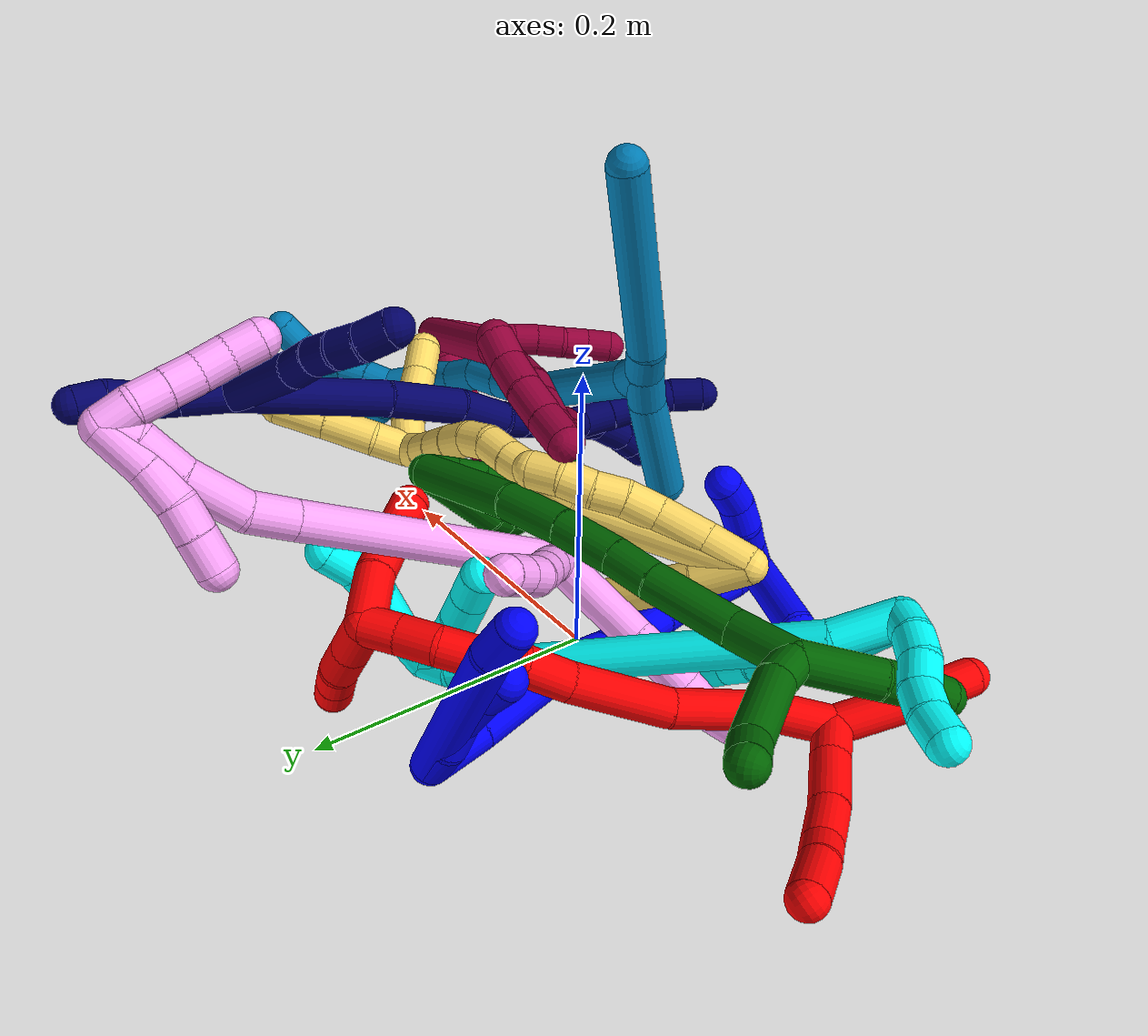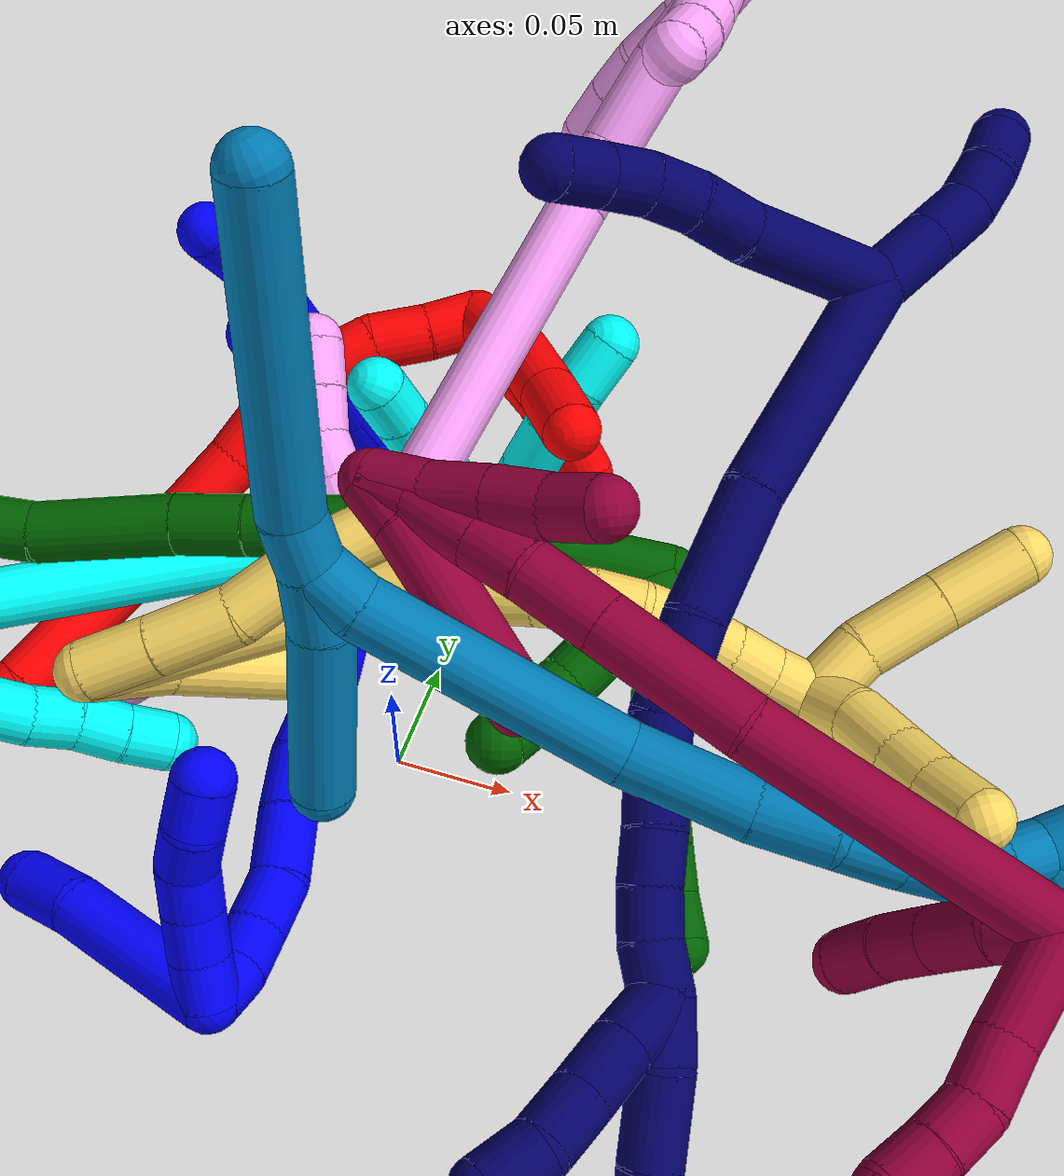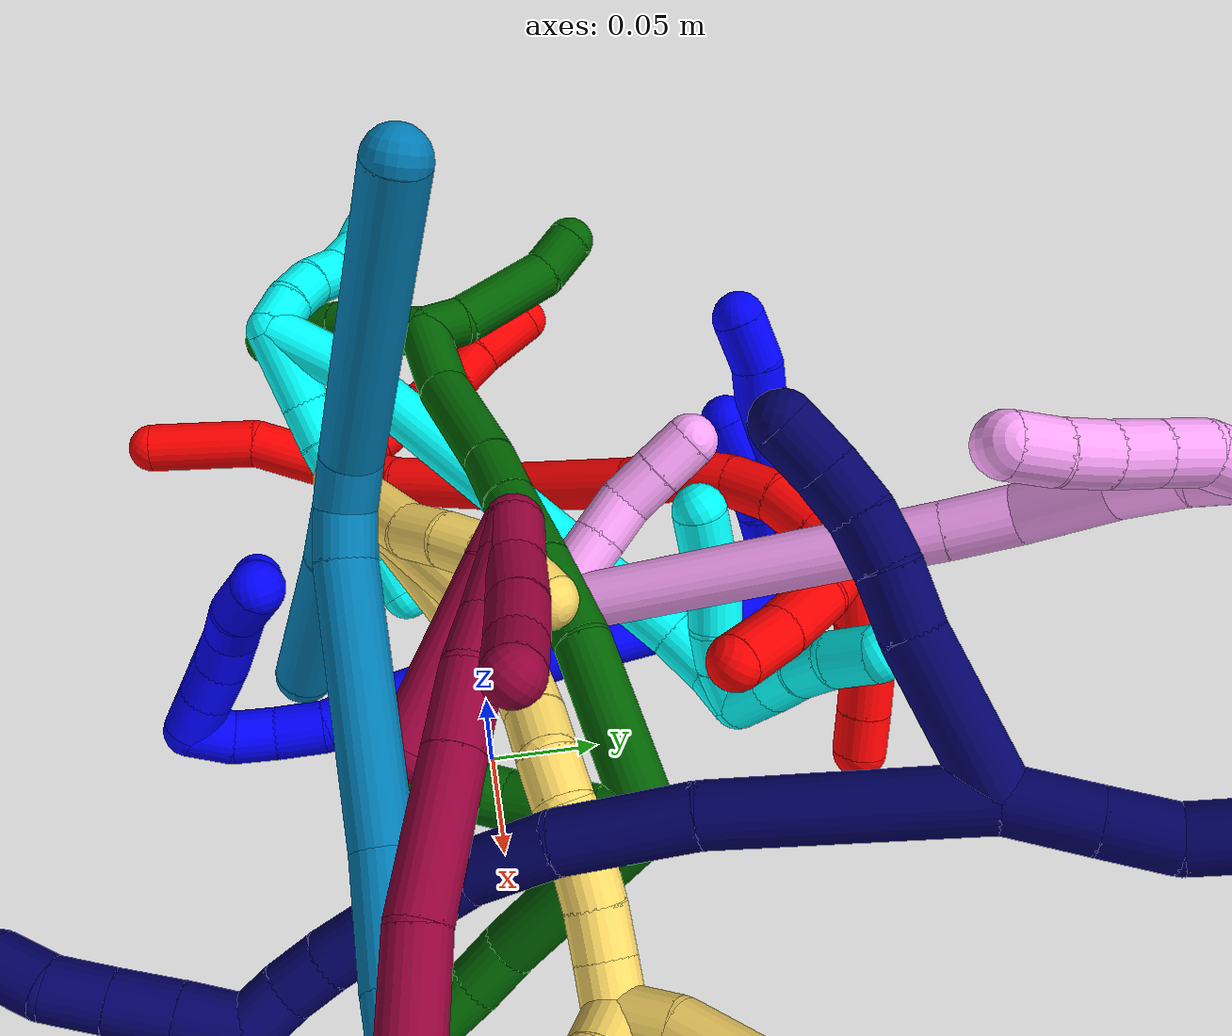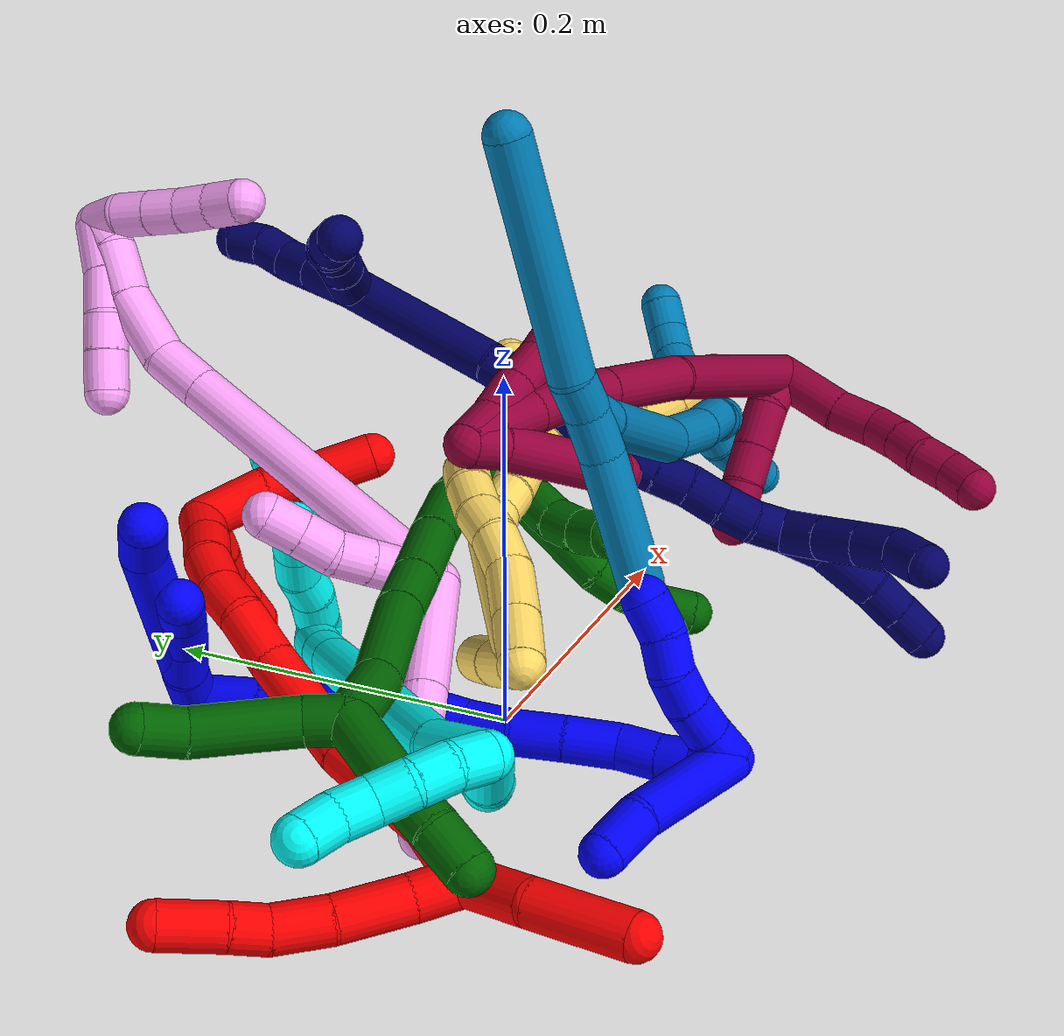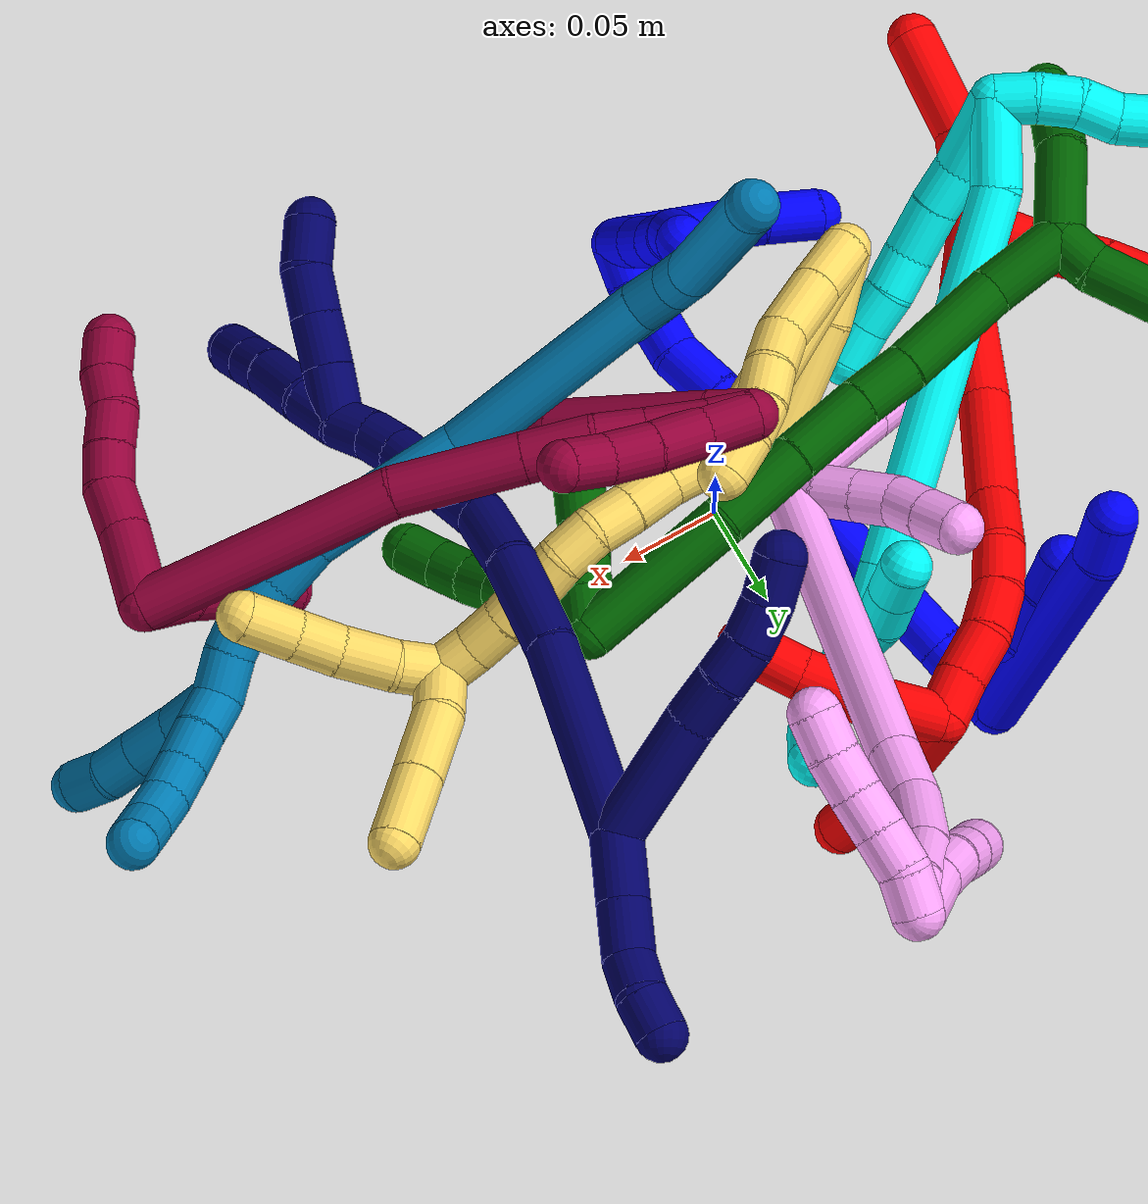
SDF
<sdf version="1.7">
 <world name="default">
  <plugin name="TubeGeneratorPlugin" filename="libtube_generator_plugin.so"/>
  <model name="photoneo_s_sensor">
   <static>1</static>
   <pose>0 0 2 1.57079 1.57079 3.14159</pose>
   <link name="link">
    <inertial><mass>0.1</mass></inertial>
    <sensor name="sensor" type="depth">
     <update_rate>30</update_rate>
     <camera>
      <horizontal_fov>1.22</horizontal_fov>
      <image><width>1920</width><height>1200</height><format>B8G8R8</format></image>
      <clip><near>0.1</near><far>4</far></clip>
      <depth_camera><output>points</output></depth_camera>
     </camera>
     <plugin name="camera_plugin" filename="libgazebo_ros_depth_camera.so">
      <baseline>0.2</baseline>
      <alwaysOn>1</alwaysOn>
      <updateRate>0.0</updateRate>
      <cameraName>camera_ir</cameraName>
      <imageTopicName>/camera/color/image_raw</imageTopicName>
      <cameraInfoTopicName>/camera/color/camera_info</cameraInfoTopicName>
      <depthImageTopicName>/camera/depth/image_raw</depthImageTopicName>
      <depthImageCameraInfoTopicName>/camera/depth/camera_info</depthImageCameraInfoTopicName>
      <pointCloudTopicName>/camera/depth/points</pointCloudTopicName>
      <frameName>fr_optical</frameName>
      <pointCloudCutoff>0.1</pointCloudCutoff>
      <pointCloudCutoffMax>2.0</pointCloudCutoffMax>
      <distortionK1>0</distortionK1>
      <distortionK2>0</distortionK2>
      <distortionK3>0</distortionK3>
      <distortionT1>0</distortionT1>
      <distortionT2>0</distortionT2>
      <CxPrime>0</CxPrime>
      <Cx>0</Cx>
      <Cy>0</Cy>
      <focalLength>0</focalLength>
      <hackBaseline>0</hackBaseline>
     </plugin>
    </sensor>
   </link>
  </model>
  <gravity>0 0 -9.8</gravity>
  <magnetic_field>6e-06 2.3e-05 -4.2e-05</magnetic_field>
  <atmosphere type="adiabatic"/>
  <physics name="default_physics" default="0" type="ode">
   <max_step_size>0.003</max_step_size>
   <real_time_factor>1</real_time_factor>
   <real_time_update_rate>1000</real_time_update_rate>
   <max_contacts>10000</max_contacts>
   <ode>
    <solver>
     <type>quick</type>
     <iters>100</iters>
     <sor>1.3</sor>
     <use_dynamic_moi_rescaling>0</use_dynamic_moi_rescaling>
    </solver>
    <constraints>
     <contact_max_correcting_vel>0</contact_max_correcting_vel>
     <contact_surface_layer>0.001</contact_surface_layer>
     <cfm>0</cfm>
     <erp>0.2</erp>
    </constraints>
   </ode>
  </physics>
  <scene><ambient>0.4 0.4 0.4 1</ambient><background>0.7 0.7 0.7 1</background><shadows>0</shadows></scene>
  <audio><device>default</device></audio>
  <spherical_coordinates>
   <surface_model>EARTH_WGS84</surface_model>
   <latitude_deg>0</latitude_deg>
   <longitude_deg>0</longitude_deg>
   <elevation>0</elevation>
   <heading_deg>0</heading_deg>
  </spherical_coordinates>
  <model name="bin">
   <static>1</static>
   <link name="bottom">
    <collision name="collision-bottom">
     <pose>0 0 -0.01 0 -0 0</pose>
     <geometry><box><size>0.8 0.6 0.02</size></box></geometry>
     <surface>
      <friction><ode><mu>100</mu><mu2>100</mu2></ode></friction>
      <contact><collide_bitmask>65535</collide_bitmask></contact>
     </surface>
    </collision>
   </link>
   <link name="west_wall">
    <collision name="collision-west_wall">
     <pose>-0.41 0 0.1 0 -0 0</pose>
     <geometry><box><size>0.02 0.6 0.2</size></box></geometry>
     <surface>
      <friction><ode><mu>100</mu><mu2>100</mu2></ode></friction>
      <contact><collide_bitmask>65535</collide_bitmask></contact>
     </surface>
    </collision>
   </link>
   <link name="east_wall">
    <collision name="collision-east_wall">
     <pose>0.41 0 0.1 0 -0 0</pose>
     <geometry><box><size>0.02 0.6 0.2</size></box></geometry>
     <surface>
      <friction><ode><mu>100</mu><mu2>100</mu2></ode></friction>
      <contact><collide_bitmask>65535</collide_bitmask></contact>
     </surface>
    </collision>
   </link>
   <link name="south_wall">
    <collision name="collision-south_wall">
     <pose>0 -0.31 0.1 0 -0 0</pose>
     <geometry><box><size>0.8 0.02 0.2</size></box></geometry>
     <surface>
      <friction><ode><mu>100</mu><mu2>100</mu2></ode></friction>
      <contact><collide_bitmask>65535</collide_bitmask></contact>
     </surface>
    </collision>
   </link>
   <link name="north_wall">
    <collision name="collision-north_wall">
     <pose>0 0.31 0.1 0 -0 0</pose>
     <geometry><box><size>0.8 0.02 0.2</size></box></geometry>
     <surface>
      <friction><ode><mu>100</mu><mu2>100</mu2></ode></friction>
      <contact><collide_bitmask>65535</collide_bitmask></contact>
     </surface>
    </collision>
   </link>
  </model>
  <model name="1">
   <static>0</static>
   <link name="1">
    <collision name="collision-cylinder-e_1_2_8">
     <pose>0.005322 0.003021 0.062188 -0.048534 0.085265 -0.002071</pose>
     <geometry><cylinder><radius>0.0125</radius><length>0.124977</length></cylinder></geometry>
     <surface>
      <friction><ode><mu>1.16</mu><mu2>1.16</mu2><slip1>0</slip1><slip2>0</slip2></ode></friction>
      <contact><ode><kp>1e+06</kp><kd>1</kd><max_vel>0</max_vel><min_depth>0.001</min_depth></ode></contact>
     </surface>
    </collision>
    <visual name="visual-cylinder-e_1_2_8">
     <pose>0.005322 0.003021 0.062188 -0.048534 0.085265 -0.002071</pose>
     <geometry><cylinder><radius>0.0125</radius><length>0.124977</length></cylinder></geometry>
     <material><ambient>0 0 1 1</ambient></material>
    </visual>
    <collision name="collision-cylinder-e_2_8_6">
     <pose>0.011791 0.003428 0.136558 0.211297 0.091875 0.00975</pose>
     <geometry><cylinder><radius>0.0125</radius><length>0.025023</length></cylinder></geometry>
     <surface>
      <friction><ode><mu>1.16</mu><mu2>1.16</mu2><slip1>0</slip1><slip2>0</slip2></ode></friction>
      <contact><ode><kp>1e+06</kp><kd>1</kd><max_vel>0</max_vel><min_depth>0.001</min_depth></ode></contact>
     </surface>
    </collision>
    <visual name="visual-cylinder-e_2_8_6">
     <pose>0.011791 0.003428 0.136558 0.211297 0.091875 0.00975</pose>
     <geometry><cylinder><radius>0.0125</radius><length>0.025023</length></cylinder></geometry>
     <material><ambient>0 0 1 1</ambient></material>
    </visual>
    <collision name="collision-cylinder-e_1_2_9">
     <pose>4.2e-05 -0.000456 0.014 0.032573 0.00303 4.9e-05</pose>
     <geometry><cylinder><radius>0.0125</radius><length>0.028015</length></cylinder></geometry>
     <surface>
      <friction><ode><mu>1.16</mu><mu2>1.16</mu2><slip1>0</slip1><slip2>0</slip2></ode></friction>
      <contact><ode><kp>1e+06</kp><kd>1</kd><max_vel>0</max_vel><min_depth>0.001</min_depth></ode></contact>
     </surface>
    </collision>
    <visual name="visual-cylinder-e_1_2_9">
     <pose>4.2e-05 -0.000456 0.014 0.032573 0.00303 4.9e-05</pose>
     <geometry><cylinder><radius>0.0125</radius><length>0.028015</length></cylinder></geometry>
     <material><ambient>0 0 1 1</ambient></material>
    </visual>
    <collision name="collision-cylinder-e_2_9_10">
     <pose>0.003054 -0.001947 0.039041 0.093445 0.261603 0.012302</pose>
     <geometry><cylinder><radius>0.0125</radius><length>0.02296</length></cylinder></geometry>
     <surface>
      <friction><ode><mu>1.16</mu><mu2>1.16</mu2><slip1>0</slip1><slip2>0</slip2></ode></friction>
      <contact><ode><kp>1e+06</kp><kd>1</kd><max_vel>0</max_vel><min_depth>0.001</min_depth></ode></contact>
     </surface>
    </collision>
    <visual name="visual-cylinder-e_2_9_10">
     <pose>0.003054 -0.001947 0.039041 0.093445 0.261603 0.012302</pose>
     <geometry><cylinder><radius>0.0125</radius><length>0.02296</length></cylinder></geometry>
     <material><ambient>0 0 1 1</ambient></material>
    </visual>
    <collision name="collision-cylinder-e_3_10_11">
     <pose>0.006678 -0.005474 0.064211 0.174577 0.045661 0.003996</pose>
     <geometry><cylinder><radius>0.0125</radius><length>0.028725</length></cylinder></geometry>
     <surface>
      <friction><ode><mu>1.16</mu><mu2>1.16</mu2><slip1>0</slip1><slip2>0</slip2></ode></friction>
      <contact><ode><kp>1e+06</kp><kd>1</kd><max_vel>0</max_vel><min_depth>0.001</min_depth></ode></contact>
     </surface>
    </collision>
    <visual name="visual-cylinder-e_3_10_11">
     <pose>0.006678 -0.005474 0.064211 0.174577 0.045661 0.003996</pose>
     <geometry><cylinder><radius>0.0125</radius><length>0.028725</length></cylinder></geometry>
     <material><ambient>0 0 1 1</ambient></material>
    </visual>
    <collision name="collision-cylinder-e_4_11_5">
     <pose>0.006429 -0.010493 0.08813 0.252617 -0.089264 -0.011343</pose>
     <geometry><cylinder><radius>0.0125</radius><length>0.0203</length></cylinder></geometry>
     <surface>
      <friction><ode><mu>1.16</mu><mu2>1.16</mu2><slip1>0</slip1><slip2>0</slip2></ode></friction>
      <contact><ode><kp>1e+06</kp><kd>1</kd><max_vel>0</max_vel><min_depth>0.001</min_depth></ode></contact>
     </surface>
    </collision>
    <visual name="visual-cylinder-e_4_11_5">
     <pose>0.006429 -0.010493 0.08813 0.252617 -0.089264 -0.011343</pose>
     <geometry><cylinder><radius>0.0125</radius><length>0.0203</length></cylinder></geometry>
     <material><ambient>0 0 1 1</ambient></material>
    </visual>
    <collision name="collision-cylinder-e_1_2_12">
     <pose>0.006589 -0.01857 0.001232 1.50457 0.340262 0.318822</pose>
     <geometry><cylinder><radius>0.0125</radius><length>0.039485</length></cylinder></geometry>
     <surface>
      <friction><ode><mu>1.16</mu><mu2>1.16</mu2><slip1>0</slip1><slip2>0</slip2></ode></friction>
      <contact><ode><kp>1e+06</kp><kd>1</kd><max_vel>0</max_vel><min_depth>0.001</min_depth></ode></contact>
     </surface>
    </collision>
    <visual name="visual-cylinder-e_1_2_12">
     <pose>0.006589 -0.01857 0.001232 1.50457 0.340262 0.318822</pose>
     <geometry><cylinder><radius>0.0125</radius><length>0.039485</length></cylinder></geometry>
     <material><ambient>0 0 1 1</ambient></material>
    </visual>
    <collision name="collision-cylinder-e_2_12_13">
     <pose>0.028427 -0.073995 0.005244 1.49548 0.391303 0.363534</pose>
     <geometry><cylinder><radius>0.0125</radius><length>0.079965</length></cylinder></geometry>
     <surface>
      <friction><ode><mu>1.16</mu><mu2>1.16</mu2><slip1>0</slip1><slip2>0</slip2></ode></friction>
      <contact><ode><kp>1e+06</kp><kd>1</kd><max_vel>0</max_vel><min_depth>0.001</min_depth></ode></contact>
     </surface>
    </collision>
    <visual name="visual-cylinder-e_2_12_13">
     <pose>0.028427 -0.073995 0.005244 1.49548 0.391303 0.363534</pose>
     <geometry><cylinder><radius>0.0125</radius><length>0.079965</length></cylinder></geometry>
     <material><ambient>0 0 1 1</ambient></material>
    </visual>
    <collision name="collision-cylinder-e_3_13_14">
     <pose>0.046862 -0.127348 0.006462 1.66529 0.189986 0.208713</pose>
     <geometry><cylinder><radius>0.0125</radius><length>0.033748</length></cylinder></geometry>
     <surface>
      <friction><ode><mu>1.16</mu><mu2>1.16</mu2><slip1>0</slip1><slip2>0</slip2></ode></friction>
      <contact><ode><kp>1e+06</kp><kd>1</kd><max_vel>0</max_vel><min_depth>0.001</min_depth></ode></contact>
     </surface>
    </collision>
    <visual name="visual-cylinder-e_3_13_14">
     <pose>0.046862 -0.127348 0.006462 1.66529 0.189986 0.208713</pose>
     <geometry><cylinder><radius>0.0125</radius><length>0.033748</length></cylinder></geometry>
     <material><ambient>0 0 1 1</ambient></material>
    </visual>
    <collision name="collision-cylinder-e_4_14_15">
     <pose>0.052361 -0.156573 0.006042 1.4812 0.178943 0.16366</pose>
     <geometry><cylinder><radius>0.0125</radius><length>0.025975</length></cylinder></geometry>
     <surface>
      <friction><ode><mu>1.16</mu><mu2>1.16</mu2><slip1>0</slip1><slip2>0</slip2></ode></friction>
      <contact><ode><kp>1e+06</kp><kd>1</kd><max_vel>0</max_vel><min_depth>0.001</min_depth></ode></contact>
     </surface>
    </collision>
    <visual name="visual-cylinder-e_4_14_15">
     <pose>0.052361 -0.156573 0.006042 1.4812 0.178943 0.16366</pose>
     <geometry><cylinder><radius>0.0125</radius><length>0.025975</length></cylinder></geometry>
     <material><ambient>0 0 1 1</ambient></material>
    </visual>
    <collision name="collision-cylinder-e_5_15_16">
     <pose>0.059297 -0.182545 0.006827 1.59786 0.335893 0.344929</pose>
     <geometry><cylinder><radius>0.0125</radius><length>0.028063</length></cylinder></geometry>
     <surface>
      <friction><ode><mu>1.16</mu><mu2>1.16</mu2><slip1>0</slip1><slip2>0</slip2></ode></friction>
      <contact><ode><kp>1e+06</kp><kd>1</kd><max_vel>0</max_vel><min_depth>0.001</min_depth></ode></contact>
     </surface>
    </collision>
    <visual name="visual-cylinder-e_5_15_16">
     <pose>0.059297 -0.182545 0.006827 1.59786 0.335893 0.344929</pose>
     <geometry><cylinder><radius>0.0125</radius><length>0.028063</length></cylinder></geometry>
     <material><ambient>0 0 1 1</ambient></material>
    </visual>
    <collision name="collision-cylinder-e_6_16_17">
     <pose>0.068941 -0.209528 0.005102 1.6699 0.348615 0.384151</pose>
     <geometry><cylinder><radius>0.0125</radius><length>0.029383</length></cylinder></geometry>
     <surface>
      <friction><ode><mu>1.16</mu><mu2>1.16</mu2><slip1>0</slip1><slip2>0</slip2></ode></friction>
      <contact><ode><kp>1e+06</kp><kd>1</kd><max_vel>0</max_vel><min_depth>0.001</min_depth></ode></contact>
     </surface>
    </collision>
    <visual name="visual-cylinder-e_6_16_17">
     <pose>0.068941 -0.209528 0.005102 1.6699 0.348615 0.384151</pose>
     <geometry><cylinder><radius>0.0125</radius><length>0.029383</length></cylinder></geometry>
     <material><ambient>0 0 1 1</ambient></material>
    </visual>
    <collision name="collision-cylinder-e_7_17_18">
     <pose>0.075388 -0.234725 0.004693 1.4875 0.12362 0.113751</pose>
     <geometry><cylinder><radius>0.0125</radius><length>0.02317</length></cylinder></geometry>
     <surface>
      <friction><ode><mu>1.16</mu><mu2>1.16</mu2><slip1>0</slip1><slip2>0</slip2></ode></friction>
      <contact><ode><kp>1e+06</kp><kd>1</kd><max_vel>0</max_vel><min_depth>0.001</min_depth></ode></contact>
     </surface>
    </collision>
    <visual name="visual-cylinder-e_7_17_18">
     <pose>0.075388 -0.234725 0.004693 1.4875 0.12362 0.113751</pose>
     <geometry><cylinder><radius>0.0125</radius><length>0.02317</length></cylinder></geometry>
     <material><ambient>0 0 1 1</ambient></material>
    </visual>
    <collision name="collision-cylinder-e_8_18_19">
     <pose>0.078965 -0.255794 0.007396 1.39101 0.216437 0.180859</pose>
     <geometry><cylinder><radius>0.0125</radius><length>0.020008</length></cylinder></geometry>
     <surface>
      <friction><ode><mu>1.16</mu><mu2>1.16</mu2><slip1>0</slip1><slip2>0</slip2></ode></friction>
      <contact><ode><kp>1e+06</kp><kd>1</kd><max_vel>0</max_vel><min_depth>0.001</min_depth></ode></contact>
     </surface>
    </collision>
    <visual name="visual-cylinder-e_8_18_19">
     <pose>0.078965 -0.255794 0.007396 1.39101 0.216437 0.180859</pose>
     <geometry><cylinder><radius>0.0125</radius><length>0.020008</length></cylinder></geometry>
     <material><ambient>0 0 1 1</ambient></material>
    </visual>
    <collision name="collision-cylinder-e_9_19_1">
     <pose>0.083603 -0.273852 0.014095 1.04048 0.249028 0.143159</pose>
     <geometry><cylinder><radius>0.0125</radius><length>0.020201</length></cylinder></geometry>
     <surface>
      <friction><ode><mu>1.16</mu><mu2>1.16</mu2><slip1>0</slip1><slip2>0</slip2></ode></friction>
      <contact><ode><kp>1e+06</kp><kd>1</kd><max_vel>0</max_vel><min_depth>0.001</min_depth></ode></contact>
     </surface>
    </collision>
    <visual name="visual-cylinder-e_9_19_1">
     <pose>0.083603 -0.273852 0.014095 1.04048 0.249028 0.143159</pose>
     <geometry><cylinder><radius>0.0125</radius><length>0.020201</length></cylinder></geometry>
     <material><ambient>0 0 1 1</ambient></material>
    </visual>
    <collision name="collision-cylinder-e_1_1_20">
     <pose>0.054738 -0.274161 0.03412 -0.494948 -1.0708 0.297529</pose>
     <geometry><cylinder><radius>0.0125</radius><length>0.071457</length></cylinder></geometry>
     <surface>
      <friction><ode><mu>1.16</mu><mu2>1.16</mu2><slip1>0</slip1><slip2>0</slip2></ode></friction>
      <contact><ode><kp>1e+06</kp><kd>1</kd><max_vel>0</max_vel><min_depth>0.001</min_depth></ode></contact>
     </surface>
    </collision>
    <visual name="visual-cylinder-e_1_1_20">
     <pose>0.054738 -0.274161 0.03412 -0.494948 -1.0708 0.297529</pose>
     <geometry><cylinder><radius>0.0125</radius><length>0.071457</length></cylinder></geometry>
     <material><ambient>0 0 1 1</ambient></material>
    </visual>
    <collision name="collision-cylinder-e_2_20_4">
     <pose>0.009574 -0.263885 0.052094 -0.635555 -1.3155 0.497661</pose>
     <geometry><cylinder><radius>0.0125</radius><length>0.028543</length></cylinder></geometry>
     <surface>
      <friction><ode><mu>1.16</mu><mu2>1.16</mu2><slip1>0</slip1><slip2>0</slip2></ode></friction>
      <contact><ode><kp>1e+06</kp><kd>1</kd><max_vel>0</max_vel><min_depth>0.001</min_depth></ode></contact>
     </surface>
    </collision>
    <visual name="visual-cylinder-e_2_20_4">
     <pose>0.009574 -0.263885 0.052094 -0.635555 -1.3155 0.497661</pose>
     <geometry><cylinder><radius>0.0125</radius><length>0.028543</length></cylinder></geometry>
     <material><ambient>0 0 1 1</ambient></material>
    </visual>
    <collision name="collision-cylinder-e_1_1_21">
     <pose>0.086613 -0.276073 0.026857 -0.672799 0.052124 -0.018231</pose>
     <geometry><cylinder><radius>0.0125</radius><length>0.02</length></cylinder></geometry>
     <surface>
      <friction><ode><mu>1.16</mu><mu2>1.16</mu2><slip1>0</slip1><slip2>0</slip2></ode></friction>
      <contact><ode><kp>1e+06</kp><kd>1</kd><max_vel>0</max_vel><min_depth>0.001</min_depth></ode></contact>
     </surface>
    </collision>
    <visual name="visual-cylinder-e_1_1_21">
     <pose>0.086613 -0.276073 0.026857 -0.672799 0.052124 -0.018231</pose>
     <geometry><cylinder><radius>0.0125</radius><length>0.02</length></cylinder></geometry>
     <material><ambient>0 0 1 1</ambient></material>
    </visual>
    <collision name="collision-cylinder-e_2_21_22">
     <pose>0.088492 -0.263762 0.042483 -0.661699 0.136232 -0.046856</pose>
     <geometry><cylinder><radius>0.0125</radius><length>0.02</length></cylinder></geometry>
     <surface>
      <friction><ode><mu>1.16</mu><mu2>1.16</mu2><slip1>0</slip1><slip2>0</slip2></ode></friction>
      <contact><ode><kp>1e+06</kp><kd>1</kd><max_vel>0</max_vel><min_depth>0.001</min_depth></ode></contact>
     </surface>
    </collision>
    <visual name="visual-cylinder-e_2_21_22">
     <pose>0.088492 -0.263762 0.042483 -0.661699 0.136232 -0.046856</pose>
     <geometry><cylinder><radius>0.0125</radius><length>0.02</length></cylinder></geometry>
     <material><ambient>0 0 1 1</ambient></material>
    </visual>
    <collision name="collision-cylinder-e_3_22_23">
     <pose>0.092377 -0.252378 0.058396 -0.579349 0.255455 -0.07652</pose>
     <geometry><cylinder><radius>0.0125</radius><length>0.02</length></cylinder></geometry>
     <surface>
      <friction><ode><mu>1.16</mu><mu2>1.16</mu2><slip1>0</slip1><slip2>0</slip2></ode></friction>
      <contact><ode><kp>1e+06</kp><kd>1</kd><max_vel>0</max_vel><min_depth>0.001</min_depth></ode></contact>
     </surface>
    </collision>
    <visual name="visual-cylinder-e_3_22_23">
     <pose>0.092377 -0.252378 0.058396 -0.579349 0.255455 -0.07652</pose>
     <geometry><cylinder><radius>0.0125</radius><length>0.02</length></cylinder></geometry>
     <material><ambient>0 0 1 1</ambient></material>
    </visual>
    <collision name="collision-cylinder-e_4_23_24">
     <pose>0.10036 -0.242415 0.073455 -0.59046 0.577042 -0.180038</pose>
     <geometry><cylinder><radius>0.0125</radius><length>0.02</length></cylinder></geometry>
     <surface>
      <friction><ode><mu>1.16</mu><mu2>1.16</mu2><slip1>0</slip1><slip2>0</slip2></ode></friction>
      <contact><ode><kp>1e+06</kp><kd>1</kd><max_vel>0</max_vel><min_depth>0.001</min_depth></ode></contact>
     </surface>
    </collision>
    <visual name="visual-cylinder-e_4_23_24">
     <pose>0.10036 -0.242415 0.073455 -0.59046 0.577042 -0.180038</pose>
     <geometry><cylinder><radius>0.0125</radius><length>0.02</length></cylinder></geometry>
     <material><ambient>0 0 1 1</ambient></material>
    </visual>
    <collision name="collision-cylinder-e_5_24_3">
     <pose>0.109848 -0.230959 0.086552 -0.835957 0.415082 -0.186509</pose>
     <geometry><cylinder><radius>0.0125</radius><length>0.02</length></cylinder></geometry>
     <surface>
      <friction><ode><mu>1.16</mu><mu2>1.16</mu2><slip1>0</slip1><slip2>0</slip2></ode></friction>
      <contact><ode><kp>1e+06</kp><kd>1</kd><max_vel>0</max_vel><min_depth>0.001</min_depth></ode></contact>
     </surface>
    </collision>
    <visual name="visual-cylinder-e_5_24_3">
     <pose>0.109848 -0.230959 0.086552 -0.835957 0.415082 -0.186509</pose>
     <geometry><cylinder><radius>0.0125</radius><length>0.02</length></cylinder></geometry>
     <material><ambient>0 0 1 1</ambient></material>
    </visual>
    <collision name="collision-sphere-3">
     <pose>0.11388 -0.22417 0.092687 0 -0 0</pose>
     <geometry><sphere><radius>0.0125</radius></sphere></geometry>
     <surface>
      <friction><ode><mu>1.16</mu><mu2>1.16</mu2><slip1>0</slip1><slip2>0</slip2></ode></friction>
      <contact><ode><kp>1e+06</kp><kd>1</kd><max_vel>0</max_vel><min_depth>0.001</min_depth></ode></contact>
     </surface>
    </collision>
    <visual name="visual-sphere-3">
     <pose>0.11388 -0.22417 0.092687 0 -0 0</pose>
     <geometry><sphere><radius>0.0125</radius></sphere></geometry>
     <material><ambient>0 0 1 1</ambient></material>
    </visual>
    <collision name="collision-sphere-24">
     <pose>0.105815 -0.237749 0.080417 0 -0 0</pose>
     <geometry><sphere><radius>0.0125</radius></sphere></geometry>
     <surface>
      <friction><ode><mu>1.16</mu><mu2>1.16</mu2><slip1>0</slip1><slip2>0</slip2></ode></friction>
      <contact><ode><kp>1e+06</kp><kd>1</kd><max_vel>0</max_vel><min_depth>0.001</min_depth></ode></contact>
     </surface>
    </collision>
    <visual name="visual-sphere-24">
     <pose>0.105815 -0.237749 0.080417 0 -0 0</pose>
     <geometry><sphere><radius>0.0125</radius></sphere></geometry>
     <material><ambient>0 0 1 1</ambient></material>
    </visual>
    <collision name="collision-sphere-23">
     <pose>0.094904 -0.24708 0.066493 0 -0 0</pose>
     <geometry><sphere><radius>0.0125</radius></sphere></geometry>
     <surface>
      <friction><ode><mu>1.16</mu><mu2>1.16</mu2><slip1>0</slip1><slip2>0</slip2></ode></friction>
      <contact><ode><kp>1e+06</kp><kd>1</kd><max_vel>0</max_vel><min_depth>0.001</min_depth></ode></contact>
     </surface>
    </collision>
    <visual name="visual-sphere-23">
     <pose>0.094904 -0.24708 0.066493 0 -0 0</pose>
     <geometry><sphere><radius>0.0125</radius></sphere></geometry>
     <material><ambient>0 0 1 1</ambient></material>
    </visual>
    <collision name="collision-sphere-22">
     <pose>0.08985 -0.257675 0.0503 0 -0 0</pose>
     <geometry><sphere><radius>0.0125</radius></sphere></geometry>
     <surface>
      <friction><ode><mu>1.16</mu><mu2>1.16</mu2><slip1>0</slip1><slip2>0</slip2></ode></friction>
      <contact><ode><kp>1e+06</kp><kd>1</kd><max_vel>0</max_vel><min_depth>0.001</min_depth></ode></contact>
     </surface>
    </collision>
    <visual name="visual-sphere-22">
     <pose>0.08985 -0.257675 0.0503 0 -0 0</pose>
     <geometry><sphere><radius>0.0125</radius></sphere></geometry>
     <material><ambient>0 0 1 1</ambient></material>
    </visual>
    <collision name="collision-sphere-21">
     <pose>0.087134 -0.26985 0.034667 0 -0 0</pose>
     <geometry><sphere><radius>0.0125</radius></sphere></geometry>
     <surface>
      <friction><ode><mu>1.16</mu><mu2>1.16</mu2><slip1>0</slip1><slip2>0</slip2></ode></friction>
      <contact><ode><kp>1e+06</kp><kd>1</kd><max_vel>0</max_vel><min_depth>0.001</min_depth></ode></contact>
     </surface>
    </collision>
    <visual name="visual-sphere-21">
     <pose>0.087134 -0.26985 0.034667 0 -0 0</pose>
     <geometry><sphere><radius>0.0125</radius></sphere></geometry>
     <material><ambient>0 0 1 1</ambient></material>
    </visual>
    <collision name="collision-sphere-4">
     <pose>-0.004235 -0.261746 0.054994 0 -0 0</pose>
     <geometry><sphere><radius>0.0125</radius></sphere></geometry>
     <surface>
      <friction><ode><mu>1.16</mu><mu2>1.16</mu2><slip1>0</slip1><slip2>0</slip2></ode></friction>
      <contact><ode><kp>1e+06</kp><kd>1</kd><max_vel>0</max_vel><min_depth>0.001</min_depth></ode></contact>
     </surface>
    </collision>
    <visual name="visual-sphere-4">
     <pose>-0.004235 -0.261746 0.054994 0 -0 0</pose>
     <geometry><sphere><radius>0.0125</radius></sphere></geometry>
     <material><ambient>0 0 1 1</ambient></material>
    </visual>
    <collision name="collision-sphere-20">
     <pose>0.023383 -0.266025 0.049193 0 -0 0</pose>
     <geometry><sphere><radius>0.0125</radius></sphere></geometry>
     <surface>
      <friction><ode><mu>1.16</mu><mu2>1.16</mu2><slip1>0</slip1><slip2>0</slip2></ode></friction>
      <contact><ode><kp>1e+06</kp><kd>1</kd><max_vel>0</max_vel><min_depth>0.001</min_depth></ode></contact>
     </surface>
    </collision>
    <visual name="visual-sphere-20">
     <pose>0.023383 -0.266025 0.049193 0 -0 0</pose>
     <geometry><sphere><radius>0.0125</radius></sphere></geometry>
     <material><ambient>0 0 1 1</ambient></material>
    </visual>
    <collision name="collision-sphere-11">
     <pose>0.007334 -0.007966 0.078341 0 -0 0</pose>
     <geometry><sphere><radius>0.0125</radius></sphere></geometry>
     <surface>
      <friction><ode><mu>1.16</mu><mu2>1.16</mu2><slip1>0</slip1><slip2>0</slip2></ode></friction>
      <contact><ode><kp>1e+06</kp><kd>1</kd><max_vel>0</max_vel><min_depth>0.001</min_depth></ode></contact>
     </surface>
    </collision>
    <visual name="visual-sphere-11">
     <pose>0.007334 -0.007966 0.078341 0 -0 0</pose>
     <geometry><sphere><radius>0.0125</radius></sphere></geometry>
     <material><ambient>0 0 1 1</ambient></material>
    </visual>
    <collision name="collision-sphere-10">
     <pose>0.006023 -0.002982 0.050082 0 -0 0</pose>
     <geometry><sphere><radius>0.0125</radius></sphere></geometry>
     <surface>
      <friction><ode><mu>1.16</mu><mu2>1.16</mu2><slip1>0</slip1><slip2>0</slip2></ode></friction>
      <contact><ode><kp>1e+06</kp><kd>1</kd><max_vel>0</max_vel><min_depth>0.001</min_depth></ode></contact>
     </surface>
    </collision>
    <visual name="visual-sphere-10">
     <pose>0.006023 -0.002982 0.050082 0 -0 0</pose>
     <geometry><sphere><radius>0.0125</radius></sphere></geometry>
     <material><ambient>0 0 1 1</ambient></material>
    </visual>
    <collision name="collision-sphere-6">
     <pose>0.012939 0.000815 0.14874 0 -0 0</pose>
     <geometry><sphere><radius>0.0125</radius></sphere></geometry>
     <surface>
      <friction><ode><mu>1.16</mu><mu2>1.16</mu2><slip1>0</slip1><slip2>0</slip2></ode></friction>
      <contact><ode><kp>1e+06</kp><kd>1</kd><max_vel>0</max_vel><min_depth>0.001</min_depth></ode></contact>
     </surface>
    </collision>
    <visual name="visual-sphere-6">
     <pose>0.012939 0.000815 0.14874 0 -0 0</pose>
     <geometry><sphere><radius>0.0125</radius></sphere></geometry>
     <material><ambient>0 0 1 1</ambient></material>
    </visual>
    <collision name="collision-sphere-9">
     <pose>8.5e-05 -0.000912 0.028 0 -0 0</pose>
     <geometry><sphere><radius>0.0125</radius></sphere></geometry>
     <surface>
      <friction><ode><mu>1.16</mu><mu2>1.16</mu2><slip1>0</slip1><slip2>0</slip2></ode></friction>
      <contact><ode><kp>1e+06</kp><kd>1</kd><max_vel>0</max_vel><min_depth>0.001</min_depth></ode></contact>
     </surface>
    </collision>
    <visual name="visual-sphere-9">
     <pose>8.5e-05 -0.000912 0.028 0 -0 0</pose>
     <geometry><sphere><radius>0.0125</radius></sphere></geometry>
     <material><ambient>0 0 1 1</ambient></material>
    </visual>
    <collision name="collision-sphere-2">
     <geometry><sphere><radius>0.0125</radius></sphere></geometry>
     <surface>
      <friction><ode><mu>1.16</mu><mu2>1.16</mu2><slip1>0</slip1><slip2>0</slip2></ode></friction>
      <contact><ode><kp>1e+06</kp><kd>1</kd><max_vel>0</max_vel><min_depth>0.001</min_depth></ode></contact>
     </surface>
    </collision>
    <visual name="visual-sphere-2">
     <geometry><sphere><radius>0.0125</radius></sphere></geometry>
     <material><ambient>0 0 1 1</ambient></material>
    </visual>
    <collision name="collision-sphere-19">
     <pose>0.081113 -0.265407 0.009144 0 -0 0</pose>
     <geometry><sphere><radius>0.0125</radius></sphere></geometry>
     <surface>
      <friction><ode><mu>1.16</mu><mu2>1.16</mu2><slip1>0</slip1><slip2>0</slip2></ode></friction>
      <contact><ode><kp>1e+06</kp><kd>1</kd><max_vel>0</max_vel><min_depth>0.001</min_depth></ode></contact>
     </surface>
    </collision>
    <visual name="visual-sphere-19">
     <pose>0.081113 -0.265407 0.009144 0 -0 0</pose>
     <geometry><sphere><radius>0.0125</radius></sphere></geometry>
     <material><ambient>0 0 1 1</ambient></material>
    </visual>
    <collision name="collision-sphere-8">
     <pose>0.010643 0.006041 0.124377 0 -0 0</pose>
     <geometry><sphere><radius>0.0125</radius></sphere></geometry>
     <surface>
      <friction><ode><mu>1.16</mu><mu2>1.16</mu2><slip1>0</slip1><slip2>0</slip2></ode></friction>
      <contact><ode><kp>1e+06</kp><kd>1</kd><max_vel>0</max_vel><min_depth>0.001</min_depth></ode></contact>
     </surface>
    </collision>
    <visual name="visual-sphere-8">
     <pose>0.010643 0.006041 0.124377 0 -0 0</pose>
     <geometry><sphere><radius>0.0125</radius></sphere></geometry>
     <material><ambient>0 0 1 1</ambient></material>
    </visual>
    <collision name="collision-sphere-5">
     <pose>0.005524 -0.01302 0.097918 0 -0 0</pose>
     <geometry><sphere><radius>0.0125</radius></sphere></geometry>
     <surface>
      <friction><ode><mu>1.16</mu><mu2>1.16</mu2><slip1>0</slip1><slip2>0</slip2></ode></friction>
      <contact><ode><kp>1e+06</kp><kd>1</kd><max_vel>0</max_vel><min_depth>0.001</min_depth></ode></contact>
     </surface>
    </collision>
    <visual name="visual-sphere-5">
     <pose>0.005524 -0.01302 0.097918 0 -0 0</pose>
     <geometry><sphere><radius>0.0125</radius></sphere></geometry>
     <material><ambient>0 0 1 1</ambient></material>
    </visual>
    <collision name="collision-sphere-12">
     <pose>0.013178 -0.03714 0.002463 0 -0 0</pose>
     <geometry><sphere><radius>0.0125</radius></sphere></geometry>
     <surface>
      <friction><ode><mu>1.16</mu><mu2>1.16</mu2><slip1>0</slip1><slip2>0</slip2></ode></friction>
      <contact><ode><kp>1e+06</kp><kd>1</kd><max_vel>0</max_vel><min_depth>0.001</min_depth></ode></contact>
     </surface>
    </collision>
    <visual name="visual-sphere-12">
     <pose>0.013178 -0.03714 0.002463 0 -0 0</pose>
     <geometry><sphere><radius>0.0125</radius></sphere></geometry>
     <material><ambient>0 0 1 1</ambient></material>
    </visual>
    <collision name="collision-sphere-13">
     <pose>0.043676 -0.110851 0.008025 0 -0 0</pose>
     <geometry><sphere><radius>0.0125</radius></sphere></geometry>
     <surface>
      <friction><ode><mu>1.16</mu><mu2>1.16</mu2><slip1>0</slip1><slip2>0</slip2></ode></friction>
      <contact><ode><kp>1e+06</kp><kd>1</kd><max_vel>0</max_vel><min_depth>0.001</min_depth></ode></contact>
     </surface>
    </collision>
    <visual name="visual-sphere-13">
     <pose>0.043676 -0.110851 0.008025 0 -0 0</pose>
     <geometry><sphere><radius>0.0125</radius></sphere></geometry>
     <material><ambient>0 0 1 1</ambient></material>
    </visual>
    <collision name="collision-sphere-14">
     <pose>0.050049 -0.143844 0.004898 0 -0 0</pose>
     <geometry><sphere><radius>0.0125</radius></sphere></geometry>
     <surface>
      <friction><ode><mu>1.16</mu><mu2>1.16</mu2><slip1>0</slip1><slip2>0</slip2></ode></friction>
      <contact><ode><kp>1e+06</kp><kd>1</kd><max_vel>0</max_vel><min_depth>0.001</min_depth></ode></contact>
     </surface>
    </collision>
    <visual name="visual-sphere-14">
     <pose>0.050049 -0.143844 0.004898 0 -0 0</pose>
     <geometry><sphere><radius>0.0125</radius></sphere></geometry>
     <material><ambient>0 0 1 1</ambient></material>
    </visual>
    <collision name="collision-sphere-15">
     <pose>0.054672 -0.169302 0.007185 0 -0 0</pose>
     <geometry><sphere><radius>0.0125</radius></sphere></geometry>
     <surface>
      <friction><ode><mu>1.16</mu><mu2>1.16</mu2><slip1>0</slip1><slip2>0</slip2></ode></friction>
      <contact><ode><kp>1e+06</kp><kd>1</kd><max_vel>0</max_vel><min_depth>0.001</min_depth></ode></contact>
     </surface>
    </collision>
    <visual name="visual-sphere-15">
     <pose>0.054672 -0.169302 0.007185 0 -0 0</pose>
     <geometry><sphere><radius>0.0125</radius></sphere></geometry>
     <material><ambient>0 0 1 1</ambient></material>
    </visual>
    <collision name="collision-sphere-16">
     <pose>0.063922 -0.195787 0.006469 0 -0 0</pose>
     <geometry><sphere><radius>0.0125</radius></sphere></geometry>
     <surface>
      <friction><ode><mu>1.16</mu><mu2>1.16</mu2><slip1>0</slip1><slip2>0</slip2></ode></friction>
      <contact><ode><kp>1e+06</kp><kd>1</kd><max_vel>0</max_vel><min_depth>0.001</min_depth></ode></contact>
     </surface>
    </collision>
    <visual name="visual-sphere-16">
     <pose>0.063922 -0.195787 0.006469 0 -0 0</pose>
     <geometry><sphere><radius>0.0125</radius></sphere></geometry>
     <material><ambient>0 0 1 1</ambient></material>
    </visual>
    <collision name="collision-sphere-17">
     <pose>0.07396 -0.223268 0.003736 0 -0 0</pose>
     <geometry><sphere><radius>0.0125</radius></sphere></geometry>
     <surface>
      <friction><ode><mu>1.16</mu><mu2>1.16</mu2><slip1>0</slip1><slip2>0</slip2></ode></friction>
      <contact><ode><kp>1e+06</kp><kd>1</kd><max_vel>0</max_vel><min_depth>0.001</min_depth></ode></contact>
     </surface>
    </collision>
    <visual name="visual-sphere-17">
     <pose>0.07396 -0.223268 0.003736 0 -0 0</pose>
     <geometry><sphere><radius>0.0125</radius></sphere></geometry>
     <material><ambient>0 0 1 1</ambient></material>
    </visual>
    <collision name="collision-sphere-18">
     <pose>0.076817 -0.246181 0.005649 0 -0 0</pose>
     <geometry><sphere><radius>0.0125</radius></sphere></geometry>
     <surface>
      <friction><ode><mu>1.16</mu><mu2>1.16</mu2><slip1>0</slip1><slip2>0</slip2></ode></friction>
      <contact><ode><kp>1e+06</kp><kd>1</kd><max_vel>0</max_vel><min_depth>0.001</min_depth></ode></contact>
     </surface>
    </collision>
    <visual name="visual-sphere-18">
     <pose>0.076817 -0.246181 0.005649 0 -0 0</pose>
     <geometry><sphere><radius>0.0125</radius></sphere></geometry>
     <material><ambient>0 0 1 1</ambient></material>
    </visual>
    <collision name="collision-sphere-1">
     <pose>0.086092 -0.282297 0.019046 0 -0 0</pose>
     <geometry><sphere><radius>0.0125</radius></sphere></geometry>
     <surface>
      <friction><ode><mu>1.16</mu><mu2>1.16</mu2><slip1>0</slip1><slip2>0</slip2></ode></friction>
      <contact><ode><kp>1e+06</kp><kd>1</kd><max_vel>0</max_vel><min_depth>0.001</min_depth></ode></contact>
     </surface>
    </collision>
    <visual name="visual-sphere-1">
     <pose>0.086092 -0.282297 0.019046 0 -0 0</pose>
     <geometry><sphere><radius>0.0125</radius></sphere></geometry>
     <material><ambient>0 0 1 1</ambient></material>
    </visual>
    <inertial>
     <pose>0.03903 -0.126376 0.03669 0 -0 0</pose>
     <mass>0.75</mass>
     <inertia><ixx>0.000292</ixx><ixy>0</ixy><ixz>0</ixz><iyy>0.00024</iyy><iyz>0</iyz><izz>6.7e-05</izz></inertia>
    </inertial>
   </link>
   <pose>-0.064327 0.155602 0.012434 0.202106 -0.517702 -0.187013</pose>
  </model>
  <model name="2">
   <static>0</static>
   <link name="2">
    <collision name="collision-cylinder-e_1_2_8">
     <pose>-0.011702 0.001691 -0.006817 -2.89848 -1.03025 2.71654</pose>
     <geometry><cylinder><radius>0.0125</radius><length>0.027296</length></cylinder></geometry>
     <surface>
      <friction><ode><mu>1.16</mu><mu2>1.16</mu2><slip1>0</slip1><slip2>0</slip2></ode></friction>
      <contact><ode><kp>1e+06</kp><kd>1</kd><max_vel>0</max_vel><min_depth>0.001</min_depth></ode></contact>
     </surface>
    </collision>
    <visual name="visual-cylinder-e_1_2_8">
     <pose>-0.011702 0.001691 -0.006817 -2.89848 -1.03025 2.71654</pose>
     <geometry><cylinder><radius>0.0125</radius><length>0.027296</length></cylinder></geometry>
     <material><ambient>1 0 0 1</ambient></material>
    </visual>
    <collision name="collision-cylinder-e_2_8_9">
     <pose>-0.040502 0.006845 -0.02221 -2.75772 -1.07491 2.5112</pose>
     <geometry><cylinder><radius>0.0125</radius><length>0.038878</length></cylinder></geometry>
     <surface>
      <friction><ode><mu>1.16</mu><mu2>1.16</mu2><slip1>0</slip1><slip2>0</slip2></ode></friction>
      <contact><ode><kp>1e+06</kp><kd>1</kd><max_vel>0</max_vel><min_depth>0.001</min_depth></ode></contact>
     </surface>
    </collision>
    <visual name="visual-cylinder-e_2_8_9">
     <pose>-0.040502 0.006845 -0.02221 -2.75772 -1.07491 2.5112</pose>
     <geometry><cylinder><radius>0.0125</radius><length>0.038878</length></cylinder></geometry>
     <material><ambient>1 0 0 1</ambient></material>
    </visual>
    <collision name="collision-cylinder-e_3_9_10">
     <pose>-0.070009 0.014368 -0.038458 -2.65505 -0.960464 2.25233</pose>
     <geometry><cylinder><radius>0.0125</radius><length>0.030287</length></cylinder></geometry>
     <surface>
      <friction><ode><mu>1.16</mu><mu2>1.16</mu2><slip1>0</slip1><slip2>0</slip2></ode></friction>
      <contact><ode><kp>1e+06</kp><kd>1</kd><max_vel>0</max_vel><min_depth>0.001</min_depth></ode></contact>
     </surface>
    </collision>
    <visual name="visual-cylinder-e_3_9_10">
     <pose>-0.070009 0.014368 -0.038458 -2.65505 -0.960464 2.25233</pose>
     <geometry><cylinder><radius>0.0125</radius><length>0.030287</length></cylinder></geometry>
     <material><ambient>1 0 0 1</ambient></material>
    </visual>
    <collision name="collision-cylinder-e_4_10_11">
     <pose>-0.090526 0.023325 -0.049443 -2.16534 -0.940587 1.52723</pose>
     <geometry><cylinder><radius>0.0125</radius><length>0.02007</length></cylinder></geometry>
     <surface>
      <friction><ode><mu>1.16</mu><mu2>1.16</mu2><slip1>0</slip1><slip2>0</slip2></ode></friction>
      <contact><ode><kp>1e+06</kp><kd>1</kd><max_vel>0</max_vel><min_depth>0.001</min_depth></ode></contact>
     </surface>
    </collision>
    <visual name="visual-cylinder-e_4_10_11">
     <pose>-0.090526 0.023325 -0.049443 -2.16534 -0.940587 1.52723</pose>
     <geometry><cylinder><radius>0.0125</radius><length>0.02007</length></cylinder></geometry>
     <material><ambient>1 0 0 1</ambient></material>
    </visual>
    <collision name="collision-cylinder-e_5_11_6">
     <pose>-0.111488 0.035646 -0.060482 -2.37629 -0.87597 1.7217</pose>
     <geometry><cylinder><radius>0.0125</radius><length>0.033468</length></cylinder></geometry>
     <surface>
      <friction><ode><mu>1.16</mu><mu2>1.16</mu2><slip1>0</slip1><slip2>0</slip2></ode></friction>
      <contact><ode><kp>1e+06</kp><kd>1</kd><max_vel>0</max_vel><min_depth>0.001</min_depth></ode></contact>
     </surface>
    </collision>
    <visual name="visual-cylinder-e_5_11_6">
     <pose>-0.111488 0.035646 -0.060482 -2.37629 -0.87597 1.7217</pose>
     <geometry><cylinder><radius>0.0125</radius><length>0.033468</length></cylinder></geometry>
     <material><ambient>1 0 0 1</ambient></material>
    </visual>
    <collision name="collision-cylinder-e_1_2_12">
     <pose>-0.001738 -0.007499 0.021275 0.338895 -0.076905 -0.013164</pose>
     <geometry><cylinder><radius>0.0125</radius><length>0.045249</length></cylinder></geometry>
     <surface>
      <friction><ode><mu>1.16</mu><mu2>1.16</mu2><slip1>0</slip1><slip2>0</slip2></ode></friction>
      <contact><ode><kp>1e+06</kp><kd>1</kd><max_vel>0</max_vel><min_depth>0.001</min_depth></ode></contact>
     </surface>
    </collision>
    <visual name="visual-cylinder-e_1_2_12">
     <pose>-0.001738 -0.007499 0.021275 0.338895 -0.076905 -0.013164</pose>
     <geometry><cylinder><radius>0.0125</radius><length>0.045249</length></cylinder></geometry>
     <material><ambient>1 0 0 1</ambient></material>
    </visual>
    <collision name="collision-cylinder-e_2_12_5">
     <pose>0.001753 -0.028732 0.065646 0.536439 0.192218 0.05298</pose>
     <geometry><cylinder><radius>0.0125</radius><length>0.054751</length></cylinder></geometry>
     <surface>
      <friction><ode><mu>1.16</mu><mu2>1.16</mu2><slip1>0</slip1><slip2>0</slip2></ode></friction>
      <contact><ode><kp>1e+06</kp><kd>1</kd><max_vel>0</max_vel><min_depth>0.001</min_depth></ode></contact>
     </surface>
    </collision>
    <visual name="visual-cylinder-e_2_12_5">
     <pose>0.001753 -0.028732 0.065646 0.536439 0.192218 0.05298</pose>
     <geometry><cylinder><radius>0.0125</radius><length>0.054751</length></cylinder></geometry>
     <material><ambient>1 0 0 1</ambient></material>
    </visual>
    <collision name="collision-cylinder-e_1_2_13">
     <pose>0.006765 0.013517 -0.013244 -2.346 0.343323 -0.782615</pose>
     <geometry><cylinder><radius>0.0125</radius><length>0.040193</length></cylinder></geometry>
     <surface>
      <friction><ode><mu>1.16</mu><mu2>1.16</mu2><slip1>0</slip1><slip2>0</slip2></ode></friction>
      <contact><ode><kp>1e+06</kp><kd>1</kd><max_vel>0</max_vel><min_depth>0.001</min_depth></ode></contact>
     </surface>
    </collision>
    <visual name="visual-cylinder-e_1_2_13">
     <pose>0.006765 0.013517 -0.013244 -2.346 0.343323 -0.782615</pose>
     <geometry><cylinder><radius>0.0125</radius><length>0.040193</length></cylinder></geometry>
     <material><ambient>1 0 0 1</ambient></material>
    </visual>
    <collision name="collision-cylinder-e_2_13_14">
     <pose>0.016855 0.048824 -0.05072 -2.40918 0.101679 -0.26382</pose>
     <geometry><cylinder><radius>0.0125</radius><length>0.065516</length></cylinder></geometry>
     <surface>
      <friction><ode><mu>1.16</mu><mu2>1.16</mu2><slip1>0</slip1><slip2>0</slip2></ode></friction>
      <contact><ode><kp>1e+06</kp><kd>1</kd><max_vel>0</max_vel><min_depth>0.001</min_depth></ode></contact>
     </surface>
    </collision>
    <visual name="visual-cylinder-e_2_13_14">
     <pose>0.016855 0.048824 -0.05072 -2.40918 0.101679 -0.26382</pose>
     <geometry><cylinder><radius>0.0125</radius><length>0.065516</length></cylinder></geometry>
     <material><ambient>1 0 0 1</ambient></material>
    </visual>
    <collision name="collision-cylinder-e_3_14_15">
     <pose>0.026042 0.097023 -0.094361 -2.20463 0.176987 -0.347126</pose>
     <geometry><cylinder><radius>0.0125</radius><length>0.066587</length></cylinder></geometry>
     <surface>
      <friction><ode><mu>1.16</mu><mu2>1.16</mu2><slip1>0</slip1><slip2>0</slip2></ode></friction>
      <contact><ode><kp>1e+06</kp><kd>1</kd><max_vel>0</max_vel><min_depth>0.001</min_depth></ode></contact>
     </surface>
    </collision>
    <visual name="visual-cylinder-e_3_14_15">
     <pose>0.026042 0.097023 -0.094361 -2.20463 0.176987 -0.347126</pose>
     <geometry><cylinder><radius>0.0125</radius><length>0.066587</length></cylinder></geometry>
     <material><ambient>1 0 0 1</ambient></material>
    </visual>
    <collision name="collision-cylinder-e_4_15_16">
     <pose>0.034148 0.136845 -0.121315 -2.08311 0.14484 -0.246807</pose>
     <geometry><cylinder><radius>0.0125</radius><length>0.031107</length></cylinder></geometry>
     <surface>
      <friction><ode><mu>1.16</mu><mu2>1.16</mu2><slip1>0</slip1><slip2>0</slip2></ode></friction>
      <contact><ode><kp>1e+06</kp><kd>1</kd><max_vel>0</max_vel><min_depth>0.001</min_depth></ode></contact>
     </surface>
    </collision>
    <visual name="visual-cylinder-e_4_15_16">
     <pose>0.034148 0.136845 -0.121315 -2.08311 0.14484 -0.246807</pose>
     <geometry><cylinder><radius>0.0125</radius><length>0.031107</length></cylinder></geometry>
     <material><ambient>1 0 0 1</ambient></material>
    </visual>
    <collision name="collision-cylinder-e_5_16_17">
     <pose>0.039423 0.158351 -0.137137 -2.36756 0.255988 -0.611715</pose>
     <geometry><cylinder><radius>0.0125</radius><length>0.023931</length></cylinder></geometry>
     <surface>
      <friction><ode><mu>1.16</mu><mu2>1.16</mu2><slip1>0</slip1><slip2>0</slip2></ode></friction>
      <contact><ode><kp>1e+06</kp><kd>1</kd><max_vel>0</max_vel><min_depth>0.001</min_depth></ode></contact>
     </surface>
    </collision>
    <visual name="visual-cylinder-e_5_16_17">
     <pose>0.039423 0.158351 -0.137137 -2.36756 0.255988 -0.611715</pose>
     <geometry><cylinder><radius>0.0125</radius><length>0.023931</length></cylinder></geometry>
     <material><ambient>1 0 0 1</ambient></material>
    </visual>
    <collision name="collision-cylinder-e_6_17_18">
     <pose>0.048279 0.174097 -0.153442 -2.37996 0.483675 -1.10436</pose>
     <geometry><cylinder><radius>0.0125</radius><length>0.025059</length></cylinder></geometry>
     <surface>
      <friction><ode><mu>1.16</mu><mu2>1.16</mu2><slip1>0</slip1><slip2>0</slip2></ode></friction>
      <contact><ode><kp>1e+06</kp><kd>1</kd><max_vel>0</max_vel><min_depth>0.001</min_depth></ode></contact>
     </surface>
    </collision>
    <visual name="visual-cylinder-e_6_17_18">
     <pose>0.048279 0.174097 -0.153442 -2.37996 0.483675 -1.10436</pose>
     <geometry><cylinder><radius>0.0125</radius><length>0.025059</length></cylinder></geometry>
     <material><ambient>1 0 0 1</ambient></material>
    </visual>
    <collision name="collision-cylinder-e_7_18_19">
     <pose>0.062404 0.186703 -0.169388 -2.5828 0.726423 -1.84838</pose>
     <geometry><cylinder><radius>0.0125</radius><length>0.024986</length></cylinder></geometry>
     <surface>
      <friction><ode><mu>1.16</mu><mu2>1.16</mu2><slip1>0</slip1><slip2>0</slip2></ode></friction>
      <contact><ode><kp>1e+06</kp><kd>1</kd><max_vel>0</max_vel><min_depth>0.001</min_depth></ode></contact>
     </surface>
    </collision>
    <visual name="visual-cylinder-e_7_18_19">
     <pose>0.062404 0.186703 -0.169388 -2.5828 0.726423 -1.84838</pose>
     <geometry><cylinder><radius>0.0125</radius><length>0.024986</length></cylinder></geometry>
     <material><ambient>1 0 0 1</ambient></material>
    </visual>
    <collision name="collision-cylinder-e_8_19_1">
     <pose>0.077456 0.196899 -0.184711 -2.5253 0.639926 -1.61101</pose>
     <geometry><cylinder><radius>0.0125</radius><length>0.022622</length></cylinder></geometry>
     <surface>
      <friction><ode><mu>1.16</mu><mu2>1.16</mu2><slip1>0</slip1><slip2>0</slip2></ode></friction>
      <contact><ode><kp>1e+06</kp><kd>1</kd><max_vel>0</max_vel><min_depth>0.001</min_depth></ode></contact>
     </surface>
    </collision>
    <visual name="visual-cylinder-e_8_19_1">
     <pose>0.077456 0.196899 -0.184711 -2.5253 0.639926 -1.61101</pose>
     <geometry><cylinder><radius>0.0125</radius><length>0.022622</length></cylinder></geometry>
     <material><ambient>1 0 0 1</ambient></material>
    </visual>
    <collision name="collision-cylinder-e_1_1_20">
     <pose>0.092101 0.191994 -0.202017 2.34386 0.507822 1.10384</pose>
     <geometry><cylinder><radius>0.0125</radius><length>0.032455</length></cylinder></geometry>
     <surface>
      <friction><ode><mu>1.16</mu><mu2>1.16</mu2><slip1>0</slip1><slip2>0</slip2></ode></friction>
      <contact><ode><kp>1e+06</kp><kd>1</kd><max_vel>0</max_vel><min_depth>0.001</min_depth></ode></contact>
     </surface>
    </collision>
    <visual name="visual-cylinder-e_1_1_20">
     <pose>0.092101 0.191994 -0.202017 2.34386 0.507822 1.10384</pose>
     <geometry><cylinder><radius>0.0125</radius><length>0.032455</length></cylinder></geometry>
     <material><ambient>1 0 0 1</ambient></material>
    </visual>
    <collision name="collision-cylinder-e_2_20_21">
     <pose>0.104938 0.17453 -0.220055 2.40934 0.424549 1.02419</pose>
     <geometry><cylinder><radius>0.0125</radius><length>0.024014</length></cylinder></geometry>
     <surface>
      <friction><ode><mu>1.16</mu><mu2>1.16</mu2><slip1>0</slip1><slip2>0</slip2></ode></friction>
      <contact><ode><kp>1e+06</kp><kd>1</kd><max_vel>0</max_vel><min_depth>0.001</min_depth></ode></contact>
     </surface>
    </collision>
    <visual name="visual-cylinder-e_2_20_21">
     <pose>0.104938 0.17453 -0.220055 2.40934 0.424549 1.02419</pose>
     <geometry><cylinder><radius>0.0125</radius><length>0.024014</length></cylinder></geometry>
     <material><ambient>1 0 0 1</ambient></material>
    </visual>
    <collision name="collision-cylinder-e_3_21_22">
     <pose>0.116135 0.159185 -0.233433 2.14908 0.577744 1.00395</pose>
     <geometry><cylinder><radius>0.0125</radius><length>0.022895</length></cylinder></geometry>
     <surface>
      <friction><ode><mu>1.16</mu><mu2>1.16</mu2><slip1>0</slip1><slip2>0</slip2></ode></friction>
      <contact><ode><kp>1e+06</kp><kd>1</kd><max_vel>0</max_vel><min_depth>0.001</min_depth></ode></contact>
     </surface>
    </collision>
    <visual name="visual-cylinder-e_3_21_22">
     <pose>0.116135 0.159185 -0.233433 2.14908 0.577744 1.00395</pose>
     <geometry><cylinder><radius>0.0125</radius><length>0.022895</length></cylinder></geometry>
     <material><ambient>1 0 0 1</ambient></material>
    </visual>
    <collision name="collision-cylinder-e_4_22_4">
     <pose>0.128012 0.143802 -0.243231 2.12559 0.576577 0.978861</pose>
     <geometry><cylinder><radius>0.0125</radius><length>0.020636</length></cylinder></geometry>
     <surface>
      <friction><ode><mu>1.16</mu><mu2>1.16</mu2><slip1>0</slip1><slip2>0</slip2></ode></friction>
      <contact><ode><kp>1e+06</kp><kd>1</kd><max_vel>0</max_vel><min_depth>0.001</min_depth></ode></contact>
     </surface>
    </collision>
    <visual name="visual-cylinder-e_4_22_4">
     <pose>0.128012 0.143802 -0.243231 2.12559 0.576577 0.978861</pose>
     <geometry><cylinder><radius>0.0125</radius><length>0.020636</length></cylinder></geometry>
     <material><ambient>1 0 0 1</ambient></material>
    </visual>
    <collision name="collision-cylinder-e_1_1_23">
     <pose>0.101415 0.203148 -0.183108 -0.111019 1.08597 -0.067043</pose>
     <geometry><cylinder><radius>0.0125</radius><length>0.038891</length></cylinder></geometry>
     <surface>
      <friction><ode><mu>1.16</mu><mu2>1.16</mu2><slip1>0</slip1><slip2>0</slip2></ode></friction>
      <contact><ode><kp>1e+06</kp><kd>1</kd><max_vel>0</max_vel><min_depth>0.001</min_depth></ode></contact>
     </surface>
    </collision>
    <visual name="visual-cylinder-e_1_1_23">
     <pose>0.101415 0.203148 -0.183108 -0.111019 1.08597 -0.067043</pose>
     <geometry><cylinder><radius>0.0125</radius><length>0.038891</length></cylinder></geometry>
     <material><ambient>1 0 0 1</ambient></material>
    </visual>
    <collision name="collision-cylinder-e_2_23_24">
     <pose>0.131646 0.202417 -0.165447 0.197891 0.975301 0.105203</pose>
     <geometry><cylinder><radius>0.0125</radius><length>0.03147</length></cylinder></geometry>
     <surface>
      <friction><ode><mu>1.16</mu><mu2>1.16</mu2><slip1>0</slip1><slip2>0</slip2></ode></friction>
      <contact><ode><kp>1e+06</kp><kd>1</kd><max_vel>0</max_vel><min_depth>0.001</min_depth></ode></contact>
     </surface>
    </collision>
    <visual name="visual-cylinder-e_2_23_24">
     <pose>0.131646 0.202417 -0.165447 0.197891 0.975301 0.105203</pose>
     <geometry><cylinder><radius>0.0125</radius><length>0.03147</length></cylinder></geometry>
     <material><ambient>1 0 0 1</ambient></material>
    </visual>
    <collision name="collision-cylinder-e_3_24_3">
     <pose>0.156211 0.199681 -0.147549 0.107809 0.892522 0.05162</pose>
     <geometry><cylinder><radius>0.0125</radius><length>0.029639</length></cylinder></geometry>
     <surface>
      <friction><ode><mu>1.16</mu><mu2>1.16</mu2><slip1>0</slip1><slip2>0</slip2></ode></friction>
      <contact><ode><kp>1e+06</kp><kd>1</kd><max_vel>0</max_vel><min_depth>0.001</min_depth></ode></contact>
     </surface>
    </collision>
    <visual name="visual-cylinder-e_3_24_3">
     <pose>0.156211 0.199681 -0.147549 0.107809 0.892522 0.05162</pose>
     <geometry><cylinder><radius>0.0125</radius><length>0.029639</length></cylinder></geometry>
     <material><ambient>1 0 0 1</ambient></material>
    </visual>
    <collision name="collision-sphere-3">
     <pose>0.167751 0.19868 -0.138304 0 -0 0</pose>
     <geometry><sphere><radius>0.0125</radius></sphere></geometry>
     <surface>
      <friction><ode><mu>1.16</mu><mu2>1.16</mu2><slip1>0</slip1><slip2>0</slip2></ode></friction>
      <contact><ode><kp>1e+06</kp><kd>1</kd><max_vel>0</max_vel><min_depth>0.001</min_depth></ode></contact>
     </surface>
    </collision>
    <visual name="visual-sphere-3">
     <pose>0.167751 0.19868 -0.138304 0 -0 0</pose>
     <geometry><sphere><radius>0.0125</radius></sphere></geometry>
     <material><ambient>1 0 0 1</ambient></material>
    </visual>
    <collision name="collision-sphere-24">
     <pose>0.144672 0.200681 -0.156793 0 -0 0</pose>
     <geometry><sphere><radius>0.0125</radius></sphere></geometry>
     <surface>
      <friction><ode><mu>1.16</mu><mu2>1.16</mu2><slip1>0</slip1><slip2>0</slip2></ode></friction>
      <contact><ode><kp>1e+06</kp><kd>1</kd><max_vel>0</max_vel><min_depth>0.001</min_depth></ode></contact>
     </surface>
    </collision>
    <visual name="visual-sphere-24">
     <pose>0.144672 0.200681 -0.156793 0 -0 0</pose>
     <geometry><sphere><radius>0.0125</radius></sphere></geometry>
     <material><ambient>1 0 0 1</ambient></material>
    </visual>
    <collision name="collision-sphere-23">
     <pose>0.118619 0.204152 -0.174101 0 -0 0</pose>
     <geometry><sphere><radius>0.0125</radius></sphere></geometry>
     <surface>
      <friction><ode><mu>1.16</mu><mu2>1.16</mu2><slip1>0</slip1><slip2>0</slip2></ode></friction>
      <contact><ode><kp>1e+06</kp><kd>1</kd><max_vel>0</max_vel><min_depth>0.001</min_depth></ode></contact>
     </surface>
    </collision>
    <visual name="visual-sphere-23">
     <pose>0.118619 0.204152 -0.174101 0 -0 0</pose>
     <geometry><sphere><radius>0.0125</radius></sphere></geometry>
     <material><ambient>1 0 0 1</ambient></material>
    </visual>
    <collision name="collision-sphere-4">
     <pose>0.133637 0.13645 -0.247788 0 -0 0</pose>
     <geometry><sphere><radius>0.0125</radius></sphere></geometry>
     <surface>
      <friction><ode><mu>1.16</mu><mu2>1.16</mu2><slip1>0</slip1><slip2>0</slip2></ode></friction>
      <contact><ode><kp>1e+06</kp><kd>1</kd><max_vel>0</max_vel><min_depth>0.001</min_depth></ode></contact>
     </surface>
    </collision>
    <visual name="visual-sphere-4">
     <pose>0.133637 0.13645 -0.247788 0 -0 0</pose>
     <geometry><sphere><radius>0.0125</radius></sphere></geometry>
     <material><ambient>1 0 0 1</ambient></material>
    </visual>
    <collision name="collision-sphere-22">
     <pose>0.122387 0.151155 -0.238675 0 -0 0</pose>
     <geometry><sphere><radius>0.0125</radius></sphere></geometry>
     <surface>
      <friction><ode><mu>1.16</mu><mu2>1.16</mu2><slip1>0</slip1><slip2>0</slip2></ode></friction>
      <contact><ode><kp>1e+06</kp><kd>1</kd><max_vel>0</max_vel><min_depth>0.001</min_depth></ode></contact>
     </surface>
    </collision>
    <visual name="visual-sphere-22">
     <pose>0.122387 0.151155 -0.238675 0 -0 0</pose>
     <geometry><sphere><radius>0.0125</radius></sphere></geometry>
     <material><ambient>1 0 0 1</ambient></material>
    </visual>
    <collision name="collision-sphere-21">
     <pose>0.109883 0.167216 -0.228192 0 -0 0</pose>
     <geometry><sphere><radius>0.0125</radius></sphere></geometry>
     <surface>
      <friction><ode><mu>1.16</mu><mu2>1.16</mu2><slip1>0</slip1><slip2>0</slip2></ode></friction>
      <contact><ode><kp>1e+06</kp><kd>1</kd><max_vel>0</max_vel><min_depth>0.001</min_depth></ode></contact>
     </surface>
    </collision>
    <visual name="visual-sphere-21">
     <pose>0.109883 0.167216 -0.228192 0 -0 0</pose>
     <geometry><sphere><radius>0.0125</radius></sphere></geometry>
     <material><ambient>1 0 0 1</ambient></material>
    </visual>
    <collision name="collision-sphere-20">
     <pose>0.099992 0.181845 -0.211919 0 -0 0</pose>
     <geometry><sphere><radius>0.0125</radius></sphere></geometry>
     <surface>
      <friction><ode><mu>1.16</mu><mu2>1.16</mu2><slip1>0</slip1><slip2>0</slip2></ode></friction>
      <contact><ode><kp>1e+06</kp><kd>1</kd><max_vel>0</max_vel><min_depth>0.001</min_depth></ode></contact>
     </surface>
    </collision>
    <visual name="visual-sphere-20">
     <pose>0.099992 0.181845 -0.211919 0 -0 0</pose>
     <geometry><sphere><radius>0.0125</radius></sphere></geometry>
     <material><ambient>1 0 0 1</ambient></material>
    </visual>
    <collision name="collision-sphere-6">
     <pose>-0.124343 0.043068 -0.068209 0 -0 0</pose>
     <geometry><sphere><radius>0.0125</radius></sphere></geometry>
     <surface>
      <friction><ode><mu>1.16</mu><mu2>1.16</mu2><slip1>0</slip1><slip2>0</slip2></ode></friction>
      <contact><ode><kp>1e+06</kp><kd>1</kd><max_vel>0</max_vel><min_depth>0.001</min_depth></ode></contact>
     </surface>
    </collision>
    <visual name="visual-sphere-6">
     <pose>-0.124343 0.043068 -0.068209 0 -0 0</pose>
     <geometry><sphere><radius>0.0125</radius></sphere></geometry>
     <material><ambient>1 0 0 1</ambient></material>
    </visual>
    <collision name="collision-sphere-11">
     <pose>-0.098634 0.028224 -0.052756 0 -0 0</pose>
     <geometry><sphere><radius>0.0125</radius></sphere></geometry>
     <surface>
      <friction><ode><mu>1.16</mu><mu2>1.16</mu2><slip1>0</slip1><slip2>0</slip2></ode></friction>
      <contact><ode><kp>1e+06</kp><kd>1</kd><max_vel>0</max_vel><min_depth>0.001</min_depth></ode></contact>
     </surface>
    </collision>
    <visual name="visual-sphere-11">
     <pose>-0.098634 0.028224 -0.052756 0 -0 0</pose>
     <geometry><sphere><radius>0.0125</radius></sphere></geometry>
     <material><ambient>1 0 0 1</ambient></material>
    </visual>
    <collision name="collision-sphere-10">
     <pose>-0.082419 0.018426 -0.046131 0 -0 0</pose>
     <geometry><sphere><radius>0.0125</radius></sphere></geometry>
     <surface>
      <friction><ode><mu>1.16</mu><mu2>1.16</mu2><slip1>0</slip1><slip2>0</slip2></ode></friction>
      <contact><ode><kp>1e+06</kp><kd>1</kd><max_vel>0</max_vel><min_depth>0.001</min_depth></ode></contact>
     </surface>
    </collision>
    <visual name="visual-sphere-10">
     <pose>-0.082419 0.018426 -0.046131 0 -0 0</pose>
     <geometry><sphere><radius>0.0125</radius></sphere></geometry>
     <material><ambient>1 0 0 1</ambient></material>
    </visual>
    <collision name="collision-sphere-9">
     <pose>-0.0576 0.010309 -0.030786 0 -0 0</pose>
     <geometry><sphere><radius>0.0125</radius></sphere></geometry>
     <surface>
      <friction><ode><mu>1.16</mu><mu2>1.16</mu2><slip1>0</slip1><slip2>0</slip2></ode></friction>
      <contact><ode><kp>1e+06</kp><kd>1</kd><max_vel>0</max_vel><min_depth>0.001</min_depth></ode></contact>
     </surface>
    </collision>
    <visual name="visual-sphere-9">
     <pose>-0.0576 0.010309 -0.030786 0 -0 0</pose>
     <geometry><sphere><radius>0.0125</radius></sphere></geometry>
     <material><ambient>1 0 0 1</ambient></material>
    </visual>
    <collision name="collision-sphere-2">
     <geometry><sphere><radius>0.0125</radius></sphere></geometry>
     <surface>
      <friction><ode><mu>1.16</mu><mu2>1.16</mu2><slip1>0</slip1><slip2>0</slip2></ode></friction>
      <contact><ode><kp>1e+06</kp><kd>1</kd><max_vel>0</max_vel><min_depth>0.001</min_depth></ode></contact>
     </surface>
    </collision>
    <visual name="visual-sphere-2">
     <geometry><sphere><radius>0.0125</radius></sphere></geometry>
     <material><ambient>1 0 0 1</ambient></material>
    </visual>
    <collision name="collision-sphere-19">
     <pose>0.070701 0.191655 -0.177307 0 -0 0</pose>
     <geometry><sphere><radius>0.0125</radius></sphere></geometry>
     <surface>
      <friction><ode><mu>1.16</mu><mu2>1.16</mu2><slip1>0</slip1><slip2>0</slip2></ode></friction>
      <contact><ode><kp>1e+06</kp><kd>1</kd><max_vel>0</max_vel><min_depth>0.001</min_depth></ode></contact>
     </surface>
    </collision>
    <visual name="visual-sphere-19">
     <pose>0.070701 0.191655 -0.177307 0 -0 0</pose>
     <geometry><sphere><radius>0.0125</radius></sphere></geometry>
     <material><ambient>1 0 0 1</ambient></material>
    </visual>
    <collision name="collision-sphere-8">
     <pose>-0.023405 0.003381 -0.013634 0 -0 0</pose>
     <geometry><sphere><radius>0.0125</radius></sphere></geometry>
     <surface>
      <friction><ode><mu>1.16</mu><mu2>1.16</mu2><slip1>0</slip1><slip2>0</slip2></ode></friction>
      <contact><ode><kp>1e+06</kp><kd>1</kd><max_vel>0</max_vel><min_depth>0.001</min_depth></ode></contact>
     </surface>
    </collision>
    <visual name="visual-sphere-8">
     <pose>-0.023405 0.003381 -0.013634 0 -0 0</pose>
     <geometry><sphere><radius>0.0125</radius></sphere></geometry>
     <material><ambient>1 0 0 1</ambient></material>
    </visual>
    <collision name="collision-sphere-12">
     <pose>-0.003476 -0.014998 0.04255 0 -0 0</pose>
     <geometry><sphere><radius>0.0125</radius></sphere></geometry>
     <surface>
      <friction><ode><mu>1.16</mu><mu2>1.16</mu2><slip1>0</slip1><slip2>0</slip2></ode></friction>
      <contact><ode><kp>1e+06</kp><kd>1</kd><max_vel>0</max_vel><min_depth>0.001</min_depth></ode></contact>
     </surface>
    </collision>
    <visual name="visual-sphere-12">
     <pose>-0.003476 -0.014998 0.04255 0 -0 0</pose>
     <geometry><sphere><radius>0.0125</radius></sphere></geometry>
     <material><ambient>1 0 0 1</ambient></material>
    </visual>
    <collision name="collision-sphere-5">
     <pose>0.006983 -0.042465 0.088743 0 -0 0</pose>
     <geometry><sphere><radius>0.0125</radius></sphere></geometry>
     <surface>
      <friction><ode><mu>1.16</mu><mu2>1.16</mu2><slip1>0</slip1><slip2>0</slip2></ode></friction>
      <contact><ode><kp>1e+06</kp><kd>1</kd><max_vel>0</max_vel><min_depth>0.001</min_depth></ode></contact>
     </surface>
    </collision>
    <visual name="visual-sphere-5">
     <pose>0.006983 -0.042465 0.088743 0 -0 0</pose>
     <geometry><sphere><radius>0.0125</radius></sphere></geometry>
     <material><ambient>1 0 0 1</ambient></material>
    </visual>
    <collision name="collision-sphere-13">
     <pose>0.01353 0.027034 -0.026488 0 -0 0</pose>
     <geometry><sphere><radius>0.0125</radius></sphere></geometry>
     <surface>
      <friction><ode><mu>1.16</mu><mu2>1.16</mu2><slip1>0</slip1><slip2>0</slip2></ode></friction>
      <contact><ode><kp>1e+06</kp><kd>1</kd><max_vel>0</max_vel><min_depth>0.001</min_depth></ode></contact>
     </surface>
    </collision>
    <visual name="visual-sphere-13">
     <pose>0.01353 0.027034 -0.026488 0 -0 0</pose>
     <geometry><sphere><radius>0.0125</radius></sphere></geometry>
     <material><ambient>1 0 0 1</ambient></material>
    </visual>
    <collision name="collision-sphere-14">
     <pose>0.02018 0.070615 -0.074951 0 -0 0</pose>
     <geometry><sphere><radius>0.0125</radius></sphere></geometry>
     <surface>
      <friction><ode><mu>1.16</mu><mu2>1.16</mu2><slip1>0</slip1><slip2>0</slip2></ode></friction>
      <contact><ode><kp>1e+06</kp><kd>1</kd><max_vel>0</max_vel><min_depth>0.001</min_depth></ode></contact>
     </surface>
    </collision>
    <visual name="visual-sphere-14">
     <pose>0.02018 0.070615 -0.074951 0 -0 0</pose>
     <geometry><sphere><radius>0.0125</radius></sphere></geometry>
     <material><ambient>1 0 0 1</ambient></material>
    </visual>
    <collision name="collision-sphere-15">
     <pose>0.031903 0.12343 -0.113771 0 -0 0</pose>
     <geometry><sphere><radius>0.0125</radius></sphere></geometry>
     <surface>
      <friction><ode><mu>1.16</mu><mu2>1.16</mu2><slip1>0</slip1><slip2>0</slip2></ode></friction>
      <contact><ode><kp>1e+06</kp><kd>1</kd><max_vel>0</max_vel><min_depth>0.001</min_depth></ode></contact>
     </surface>
    </collision>
    <visual name="visual-sphere-15">
     <pose>0.031903 0.12343 -0.113771 0 -0 0</pose>
     <geometry><sphere><radius>0.0125</radius></sphere></geometry>
     <material><ambient>1 0 0 1</ambient></material>
    </visual>
    <collision name="collision-sphere-16">
     <pose>0.036393 0.15026 -0.128859 0 -0 0</pose>
     <geometry><sphere><radius>0.0125</radius></sphere></geometry>
     <surface>
      <friction><ode><mu>1.16</mu><mu2>1.16</mu2><slip1>0</slip1><slip2>0</slip2></ode></friction>
      <contact><ode><kp>1e+06</kp><kd>1</kd><max_vel>0</max_vel><min_depth>0.001</min_depth></ode></contact>
     </surface>
    </collision>
    <visual name="visual-sphere-16">
     <pose>0.036393 0.15026 -0.128859 0 -0 0</pose>
     <geometry><sphere><radius>0.0125</radius></sphere></geometry>
     <material><ambient>1 0 0 1</ambient></material>
    </visual>
    <collision name="collision-sphere-17">
     <pose>0.042452 0.166443 -0.145414 0 -0 0</pose>
     <geometry><sphere><radius>0.0125</radius></sphere></geometry>
     <surface>
      <friction><ode><mu>1.16</mu><mu2>1.16</mu2><slip1>0</slip1><slip2>0</slip2></ode></friction>
      <contact><ode><kp>1e+06</kp><kd>1</kd><max_vel>0</max_vel><min_depth>0.001</min_depth></ode></contact>
     </surface>
    </collision>
    <visual name="visual-sphere-17">
     <pose>0.042452 0.166443 -0.145414 0 -0 0</pose>
     <geometry><sphere><radius>0.0125</radius></sphere></geometry>
     <material><ambient>1 0 0 1</ambient></material>
    </visual>
    <collision name="collision-sphere-18">
     <pose>0.054106 0.181752 -0.161469 0 -0 0</pose>
     <geometry><sphere><radius>0.0125</radius></sphere></geometry>
     <surface>
      <friction><ode><mu>1.16</mu><mu2>1.16</mu2><slip1>0</slip1><slip2>0</slip2></ode></friction>
      <contact><ode><kp>1e+06</kp><kd>1</kd><max_vel>0</max_vel><min_depth>0.001</min_depth></ode></contact>
     </surface>
    </collision>
    <visual name="visual-sphere-18">
     <pose>0.054106 0.181752 -0.161469 0 -0 0</pose>
     <geometry><sphere><radius>0.0125</radius></sphere></geometry>
     <material><ambient>1 0 0 1</ambient></material>
    </visual>
    <collision name="collision-sphere-1">
     <pose>0.08421 0.202144 -0.192115 0 -0 0</pose>
     <geometry><sphere><radius>0.0125</radius></sphere></geometry>
     <surface>
      <friction><ode><mu>1.16</mu><mu2>1.16</mu2><slip1>0</slip1><slip2>0</slip2></ode></friction>
      <contact><ode><kp>1e+06</kp><kd>1</kd><max_vel>0</max_vel><min_depth>0.001</min_depth></ode></contact>
     </surface>
    </collision>
    <visual name="visual-sphere-1">
     <pose>0.08421 0.202144 -0.192115 0 -0 0</pose>
     <geometry><sphere><radius>0.0125</radius></sphere></geometry>
     <material><ambient>1 0 0 1</ambient></material>
    </visual>
    <inertial>
     <pose>0.031491 0.0926 -0.09204 0 -0 0</pose>
     <mass>0.75</mass>
     <inertia><ixx>8.7e-05</ixx><ixy>0</ixy><ixz>0</ixz><iyy>1.5e-05</iyy><iyz>0</iyz><izz>-7e-05</izz></inertia>
    </inertial>
   </link>
   <pose>-0.18029 -0.061247 0.020352 1.03768 0.003508 -0.294346</pose>
  </model>
  <model name="3">
   <static>0</static>
   <link name="3">
    <collision name="collision-cylinder-e_1_2_8">
     <pose>-0.001709 -0.00235 -0.019941 3.02429 -0.084888 -1.25235</pose>
     <geometry><cylinder><radius>0.0125</radius><length>0.040302</length></cylinder></geometry>
     <surface>
      <friction><ode><mu>1.16</mu><mu2>1.16</mu2><slip1>0</slip1><slip2>0</slip2></ode></friction>
      <contact><ode><kp>1e+06</kp><kd>1</kd><max_vel>0</max_vel><min_depth>0.001</min_depth></ode></contact>
     </surface>
    </collision>
    <visual name="visual-cylinder-e_1_2_8">
     <pose>-0.001709 -0.00235 -0.019941 3.02429 -0.084888 -1.25235</pose>
     <geometry><cylinder><radius>0.0125</radius><length>0.040302</length></cylinder></geometry>
     <material><ambient>0.003922 1 0.996078 1</ambient></material>
    </visual>
    <collision name="collision-cylinder-e_2_8_9">
     <pose>-0.002081 -0.00613 -0.050691 3.01007 0.121935 1.495</pose>
     <geometry><cylinder><radius>0.0125</radius><length>0.02197</length></cylinder></geometry>
     <surface>
      <friction><ode><mu>1.16</mu><mu2>1.16</mu2><slip1>0</slip1><slip2>0</slip2></ode></friction>
      <contact><ode><kp>1e+06</kp><kd>1</kd><max_vel>0</max_vel><min_depth>0.001</min_depth></ode></contact>
     </surface>
    </collision>
    <visual name="visual-cylinder-e_2_8_9">
     <pose>-0.002081 -0.00613 -0.050691 3.01007 0.121935 1.495</pose>
     <geometry><cylinder><radius>0.0125</radius><length>0.02197</length></cylinder></geometry>
     <material><ambient>0.003922 1 0.996078 1</ambient></material>
    </visual>
    <collision name="collision-cylinder-e_3_9_10">
     <pose>0.000437 -0.008472 -0.074947 3.07381 0.087482 1.8234</pose>
     <geometry><cylinder><radius>0.0125</radius><length>0.02706</length></cylinder></geometry>
     <surface>
      <friction><ode><mu>1.16</mu><mu2>1.16</mu2><slip1>0</slip1><slip2>0</slip2></ode></friction>
      <contact><ode><kp>1e+06</kp><kd>1</kd><max_vel>0</max_vel><min_depth>0.001</min_depth></ode></contact>
     </surface>
    </collision>
    <visual name="visual-cylinder-e_3_9_10">
     <pose>0.000437 -0.008472 -0.074947 3.07381 0.087482 1.8234</pose>
     <geometry><cylinder><radius>0.0125</radius><length>0.02706</length></cylinder></geometry>
     <material><ambient>0.003922 1 0.996078 1</ambient></material>
    </visual>
    <collision name="collision-cylinder-e_4_10_11">
     <pose>0.004113 -0.009259 -0.098358 -3.12887 0.245197 -3.03844</pose>
     <geometry><cylinder><radius>0.0125</radius><length>0.020544</length></cylinder></geometry>
     <surface>
      <friction><ode><mu>1.16</mu><mu2>1.16</mu2><slip1>0</slip1><slip2>0</slip2></ode></friction>
      <contact><ode><kp>1e+06</kp><kd>1</kd><max_vel>0</max_vel><min_depth>0.001</min_depth></ode></contact>
     </surface>
    </collision>
    <visual name="visual-cylinder-e_4_10_11">
     <pose>0.004113 -0.009259 -0.098358 -3.12887 0.245197 -3.03844</pose>
     <geometry><cylinder><radius>0.0125</radius><length>0.020544</length></cylinder></geometry>
     <material><ambient>0.003922 1 0.996078 1</ambient></material>
    </visual>
    <collision name="collision-cylinder-e_5_11_12">
     <pose>0.008364 -0.010678 -0.118048 2.98389 0.176599 1.68423</pose>
     <geometry><cylinder><radius>0.0125</radius><length>0.020006</length></cylinder></geometry>
     <surface>
      <friction><ode><mu>1.16</mu><mu2>1.16</mu2><slip1>0</slip1><slip2>0</slip2></ode></friction>
      <contact><ode><kp>1e+06</kp><kd>1</kd><max_vel>0</max_vel><min_depth>0.001</min_depth></ode></contact>
     </surface>
    </collision>
    <visual name="visual-cylinder-e_5_11_12">
     <pose>0.008364 -0.010678 -0.118048 2.98389 0.176599 1.68423</pose>
     <geometry><cylinder><radius>0.0125</radius><length>0.020006</length></cylinder></geometry>
     <material><ambient>0.003922 1 0.996078 1</ambient></material>
    </visual>
    <collision name="collision-cylinder-e_6_12_6">
     <pose>0.011864 -0.012813 -0.137662 3.08219 0.174154 2.48552</pose>
     <geometry><cylinder><radius>0.0125</radius><length>0.020118</length></cylinder></geometry>
     <surface>
      <friction><ode><mu>1.16</mu><mu2>1.16</mu2><slip1>0</slip1><slip2>0</slip2></ode></friction>
      <contact><ode><kp>1e+06</kp><kd>1</kd><max_vel>0</max_vel><min_depth>0.001</min_depth></ode></contact>
     </surface>
    </collision>
    <visual name="visual-cylinder-e_6_12_6">
     <pose>0.011864 -0.012813 -0.137662 3.08219 0.174154 2.48552</pose>
     <geometry><cylinder><radius>0.0125</radius><length>0.020118</length></cylinder></geometry>
     <material><ambient>0.003922 1 0.996078 1</ambient></material>
    </visual>
    <collision name="collision-cylinder-e_1_2_13">
     <pose>-0.004558 0.007847 0.004201 -1.07924 -0.473292 0.28689</pose>
     <geometry><cylinder><radius>0.0125</radius><length>0.02</length></cylinder></geometry>
     <surface>
      <friction><ode><mu>1.16</mu><mu2>1.16</mu2><slip1>0</slip1><slip2>0</slip2></ode></friction>
      <contact><ode><kp>1e+06</kp><kd>1</kd><max_vel>0</max_vel><min_depth>0.001</min_depth></ode></contact>
     </surface>
    </collision>
    <visual name="visual-cylinder-e_1_2_13">
     <pose>-0.004558 0.007847 0.004201 -1.07924 -0.473292 0.28689</pose>
     <geometry><cylinder><radius>0.0125</radius><length>0.02</length></cylinder></geometry>
     <material><ambient>0.003922 1 0.996078 1</ambient></material>
    </visual>
    <collision name="collision-cylinder-e_2_13_14">
     <pose>-0.014798 0.023633 0.010567 -1.30465 -0.60426 0.467456</pose>
     <geometry><cylinder><radius>0.0125</radius><length>0.02</length></cylinder></geometry>
     <surface>
      <friction><ode><mu>1.16</mu><mu2>1.16</mu2><slip1>0</slip1><slip2>0</slip2></ode></friction>
      <contact><ode><kp>1e+06</kp><kd>1</kd><max_vel>0</max_vel><min_depth>0.001</min_depth></ode></contact>
     </surface>
    </collision>
    <visual name="visual-cylinder-e_2_13_14">
     <pose>-0.014798 0.023633 0.010567 -1.30465 -0.60426 0.467456</pose>
     <geometry><cylinder><radius>0.0125</radius><length>0.02</length></cylinder></geometry>
     <material><ambient>0.003922 1 0.996078 1</ambient></material>
    </visual>
    <collision name="collision-cylinder-e_3_14_15">
     <pose>-0.026152 0.039796 0.012281 -1.62547 -0.603207 0.63494</pose>
     <geometry><cylinder><radius>0.0125</radius><length>0.02</length></cylinder></geometry>
     <surface>
      <friction><ode><mu>1.16</mu><mu2>1.16</mu2><slip1>0</slip1><slip2>0</slip2></ode></friction>
      <contact><ode><kp>1e+06</kp><kd>1</kd><max_vel>0</max_vel><min_depth>0.001</min_depth></ode></contact>
     </surface>
    </collision>
    <visual name="visual-cylinder-e_3_14_15">
     <pose>-0.026152 0.039796 0.012281 -1.62547 -0.603207 0.63494</pose>
     <geometry><cylinder><radius>0.0125</radius><length>0.02</length></cylinder></geometry>
     <material><ambient>0.003922 1 0.996078 1</ambient></material>
    </visual>
    <collision name="collision-cylinder-e_4_15_16">
     <pose>-0.037513 0.055824 0.014423 -1.2502 -0.605055 0.443064</pose>
     <geometry><cylinder><radius>0.0125</radius><length>0.02</length></cylinder></geometry>
     <surface>
      <friction><ode><mu>1.16</mu><mu2>1.16</mu2><slip1>0</slip1><slip2>0</slip2></ode></friction>
      <contact><ode><kp>1e+06</kp><kd>1</kd><max_vel>0</max_vel><min_depth>0.001</min_depth></ode></contact>
     </surface>
    </collision>
    <visual name="visual-cylinder-e_4_15_16">
     <pose>-0.037513 0.055824 0.014423 -1.2502 -0.605055 0.443064</pose>
     <geometry><cylinder><radius>0.0125</radius><length>0.02</length></cylinder></geometry>
     <material><ambient>0.003922 1 0.996078 1</ambient></material>
    </visual>
    <collision name="collision-cylinder-e_5_16_5">
     <pose>-0.049676 0.07003 0.021152 -0.997 -0.704271 0.394837</pose>
     <geometry><cylinder><radius>0.0125</radius><length>0.02</length></cylinder></geometry>
     <surface>
      <friction><ode><mu>1.16</mu><mu2>1.16</mu2><slip1>0</slip1><slip2>0</slip2></ode></friction>
      <contact><ode><kp>1e+06</kp><kd>1</kd><max_vel>0</max_vel><min_depth>0.001</min_depth></ode></contact>
     </surface>
    </collision>
    <visual name="visual-cylinder-e_5_16_5">
     <pose>-0.049676 0.07003 0.021152 -0.997 -0.704271 0.394837</pose>
     <geometry><cylinder><radius>0.0125</radius><length>0.02</length></cylinder></geometry>
     <material><ambient>0.003922 1 0.996078 1</ambient></material>
    </visual>
    <collision name="collision-cylinder-e_1_2_17">
     <pose>0.003498 0.011018 -0.018156 -2.59613 0.163252 -0.569094</pose>
     <geometry><cylinder><radius>0.0125</radius><length>0.043048</length></cylinder></geometry>
     <surface>
      <friction><ode><mu>1.16</mu><mu2>1.16</mu2><slip1>0</slip1><slip2>0</slip2></ode></friction>
      <contact><ode><kp>1e+06</kp><kd>1</kd><max_vel>0</max_vel><min_depth>0.001</min_depth></ode></contact>
     </surface>
    </collision>
    <visual name="visual-cylinder-e_1_2_17">
     <pose>0.003498 0.011018 -0.018156 -2.59613 0.163252 -0.569094</pose>
     <geometry><cylinder><radius>0.0125</radius><length>0.043048</length></cylinder></geometry>
     <material><ambient>0.003922 1 0.996078 1</ambient></material>
    </visual>
    <collision name="collision-cylinder-e_2_17_18">
     <pose>0.039583 0.047778 -0.121051 -2.84668 0.352576 -1.75155</pose>
     <geometry><cylinder><radius>0.0125</radius><length>0.188735</length></cylinder></geometry>
     <surface>
      <friction><ode><mu>1.16</mu><mu2>1.16</mu2><slip1>0</slip1><slip2>0</slip2></ode></friction>
      <contact><ode><kp>1e+06</kp><kd>1</kd><max_vel>0</max_vel><min_depth>0.001</min_depth></ode></contact>
     </surface>
    </collision>
    <visual name="visual-cylinder-e_2_17_18">
     <pose>0.039583 0.047778 -0.121051 -2.84668 0.352576 -1.75155</pose>
     <geometry><cylinder><radius>0.0125</radius><length>0.188735</length></cylinder></geometry>
     <material><ambient>0.003922 1 0.996078 1</ambient></material>
    </visual>
    <collision name="collision-cylinder-e_3_18_19">
     <pose>0.075865 0.076482 -0.215555 -2.84704 0.347453 -1.73806</pose>
     <geometry><cylinder><radius>0.0125</radius><length>0.021705</length></cylinder></geometry>
     <surface>
      <friction><ode><mu>1.16</mu><mu2>1.16</mu2><slip1>0</slip1><slip2>0</slip2></ode></friction>
      <contact><ode><kp>1e+06</kp><kd>1</kd><max_vel>0</max_vel><min_depth>0.001</min_depth></ode></contact>
     </surface>
    </collision>
    <visual name="visual-cylinder-e_3_18_19">
     <pose>0.075865 0.076482 -0.215555 -2.84704 0.347453 -1.73806</pose>
     <geometry><cylinder><radius>0.0125</radius><length>0.021705</length></cylinder></geometry>
     <material><ambient>0.003922 1 0.996078 1</ambient></material>
    </visual>
    <collision name="collision-cylinder-e_4_19_20">
     <pose>0.084515 0.081938 -0.237184 -2.93438 0.387918 -2.16788</pose>
     <geometry><cylinder><radius>0.0125</radius><length>0.026194</length></cylinder></geometry>
     <surface>
      <friction><ode><mu>1.16</mu><mu2>1.16</mu2><slip1>0</slip1><slip2>0</slip2></ode></friction>
      <contact><ode><kp>1e+06</kp><kd>1</kd><max_vel>0</max_vel><min_depth>0.001</min_depth></ode></contact>
     </surface>
    </collision>
    <visual name="visual-cylinder-e_4_19_20">
     <pose>0.084515 0.081938 -0.237184 -2.93438 0.387918 -2.16788</pose>
     <geometry><cylinder><radius>0.0125</radius><length>0.026194</length></cylinder></geometry>
     <material><ambient>0.003922 1 0.996078 1</ambient></material>
    </visual>
    <collision name="collision-cylinder-e_5_20_1">
     <pose>0.0957 0.084575 -0.257071 -3.12379 0.660311 -3.08966</pose>
     <geometry><cylinder><radius>0.0125</radius><length>0.020318</length></cylinder></geometry>
     <surface>
      <friction><ode><mu>1.16</mu><mu2>1.16</mu2><slip1>0</slip1><slip2>0</slip2></ode></friction>
      <contact><ode><kp>1e+06</kp><kd>1</kd><max_vel>0</max_vel><min_depth>0.001</min_depth></ode></contact>
     </surface>
    </collision>
    <visual name="visual-cylinder-e_5_20_1">
     <pose>0.0957 0.084575 -0.257071 -3.12379 0.660311 -3.08966</pose>
     <geometry><cylinder><radius>0.0125</radius><length>0.020318</length></cylinder></geometry>
     <material><ambient>0.003922 1 0.996078 1</ambient></material>
    </visual>
    <collision name="collision-cylinder-e_1_1_21">
     <pose>0.115101 0.091573 -0.262976 -1.27124 1.07201 -0.82606</pose>
     <geometry><cylinder><radius>0.0125</radius><length>0.029995</length></cylinder></geometry>
     <surface>
      <friction><ode><mu>1.16</mu><mu2>1.16</mu2><slip1>0</slip1><slip2>0</slip2></ode></friction>
      <contact><ode><kp>1e+06</kp><kd>1</kd><max_vel>0</max_vel><min_depth>0.001</min_depth></ode></contact>
     </surface>
    </collision>
    <visual name="visual-cylinder-e_1_1_21">
     <pose>0.115101 0.091573 -0.262976 -1.27124 1.07201 -0.82606</pose>
     <geometry><cylinder><radius>0.0125</radius><length>0.029995</length></cylinder></geometry>
     <material><ambient>0.003922 1 0.996078 1</ambient></material>
    </visual>
    <collision name="collision-cylinder-e_2_21_22">
     <pose>0.140584 0.102438 -0.258093 -0.967047 1.19401 -0.685681</pose>
     <geometry><cylinder><radius>0.0125</radius><length>0.026483</length></cylinder></geometry>
     <surface>
      <friction><ode><mu>1.16</mu><mu2>1.16</mu2><slip1>0</slip1><slip2>0</slip2></ode></friction>
      <contact><ode><kp>1e+06</kp><kd>1</kd><max_vel>0</max_vel><min_depth>0.001</min_depth></ode></contact>
     </surface>
    </collision>
    <visual name="visual-cylinder-e_2_21_22">
     <pose>0.140584 0.102438 -0.258093 -0.967047 1.19401 -0.685681</pose>
     <geometry><cylinder><radius>0.0125</radius><length>0.026483</length></cylinder></geometry>
     <material><ambient>0.003922 1 0.996078 1</ambient></material>
    </visual>
    <collision name="collision-cylinder-e_3_22_23">
     <pose>0.162413 0.111047 -0.254624 -1.41901 1.11609 -0.984072</pose>
     <geometry><cylinder><radius>0.0125</radius><length>0.021185</length></cylinder></geometry>
     <surface>
      <friction><ode><mu>1.16</mu><mu2>1.16</mu2><slip1>0</slip1><slip2>0</slip2></ode></friction>
      <contact><ode><kp>1e+06</kp><kd>1</kd><max_vel>0</max_vel><min_depth>0.001</min_depth></ode></contact>
     </surface>
    </collision>
    <visual name="visual-cylinder-e_3_22_23">
     <pose>0.162413 0.111047 -0.254624 -1.41901 1.11609 -0.984072</pose>
     <geometry><cylinder><radius>0.0125</radius><length>0.021185</length></cylinder></geometry>
     <material><ambient>0.003922 1 0.996078 1</ambient></material>
    </visual>
    <collision name="collision-cylinder-e_4_23_4">
     <pose>0.180793 0.122202 -0.255706 -1.83669 0.916831 -1.1469</pose>
     <geometry><cylinder><radius>0.0125</radius><length>0.022338</length></cylinder></geometry>
     <surface>
      <friction><ode><mu>1.16</mu><mu2>1.16</mu2><slip1>0</slip1><slip2>0</slip2></ode></friction>
      <contact><ode><kp>1e+06</kp><kd>1</kd><max_vel>0</max_vel><min_depth>0.001</min_depth></ode></contact>
     </surface>
    </collision>
    <visual name="visual-cylinder-e_4_23_4">
     <pose>0.180793 0.122202 -0.255706 -1.83669 0.916831 -1.1469</pose>
     <geometry><cylinder><radius>0.0125</radius><length>0.022338</length></cylinder></geometry>
     <material><ambient>0.003922 1 0.996078 1</ambient></material>
    </visual>
    <collision name="collision-cylinder-e_1_1_24">
     <pose>0.102585 0.086091 -0.255209 -0.137996 0.065458 -0.004525</pose>
     <geometry><cylinder><radius>0.0125</radius><length>0.02</length></cylinder></geometry>
     <surface>
      <friction><ode><mu>1.16</mu><mu2>1.16</mu2><slip1>0</slip1><slip2>0</slip2></ode></friction>
      <contact><ode><kp>1e+06</kp><kd>1</kd><max_vel>0</max_vel><min_depth>0.001</min_depth></ode></contact>
     </surface>
    </collision>
    <visual name="visual-cylinder-e_1_1_24">
     <pose>0.102585 0.086091 -0.255209 -0.137996 0.065458 -0.004525</pose>
     <geometry><cylinder><radius>0.0125</radius><length>0.02</length></cylinder></geometry>
     <material><ambient>0.003922 1 0.996078 1</ambient></material>
    </visual>
    <collision name="collision-cylinder-e_2_24_25">
     <pose>0.106863 0.089869 -0.236321 -0.261077 0.370864 -0.049245</pose>
     <geometry><cylinder><radius>0.0125</radius><length>0.02</length></cylinder></geometry>
     <surface>
      <friction><ode><mu>1.16</mu><mu2>1.16</mu2><slip1>0</slip1><slip2>0</slip2></ode></friction>
      <contact><ode><kp>1e+06</kp><kd>1</kd><max_vel>0</max_vel><min_depth>0.001</min_depth></ode></contact>
     </surface>
    </collision>
    <visual name="visual-cylinder-e_2_24_25">
     <pose>0.106863 0.089869 -0.236321 -0.261077 0.370864 -0.049245</pose>
     <geometry><cylinder><radius>0.0125</radius><length>0.02</length></cylinder></geometry>
     <material><ambient>0.003922 1 0.996078 1</ambient></material>
    </visual>
    <collision name="collision-cylinder-e_3_25_26">
     <pose>0.113233 0.096618 -0.218738 -0.468601 0.278057 -0.066774</pose>
     <geometry><cylinder><radius>0.0125</radius><length>0.02</length></cylinder></geometry>
     <surface>
      <friction><ode><mu>1.16</mu><mu2>1.16</mu2><slip1>0</slip1><slip2>0</slip2></ode></friction>
      <contact><ode><kp>1e+06</kp><kd>1</kd><max_vel>0</max_vel><min_depth>0.001</min_depth></ode></contact>
     </surface>
    </collision>
    <visual name="visual-cylinder-e_3_25_26">
     <pose>0.113233 0.096618 -0.218738 -0.468601 0.278057 -0.066774</pose>
     <geometry><cylinder><radius>0.0125</radius><length>0.02</length></cylinder></geometry>
     <material><ambient>0.003922 1 0.996078 1</ambient></material>
    </visual>
    <collision name="collision-cylinder-e_4_26_27">
     <pose>0.120177 0.102822 -0.201276 -0.206594 0.433387 -0.045636</pose>
     <geometry><cylinder><radius>0.0125</radius><length>0.02</length></cylinder></geometry>
     <surface>
      <friction><ode><mu>1.16</mu><mu2>1.16</mu2><slip1>0</slip1><slip2>0</slip2></ode></friction>
      <contact><ode><kp>1e+06</kp><kd>1</kd><max_vel>0</max_vel><min_depth>0.001</min_depth></ode></contact>
     </surface>
    </collision>
    <visual name="visual-cylinder-e_4_26_27">
     <pose>0.120177 0.102822 -0.201276 -0.206594 0.433387 -0.045636</pose>
     <geometry><cylinder><radius>0.0125</radius><length>0.02</length></cylinder></geometry>
     <material><ambient>0.003922 1 0.996078 1</ambient></material>
    </visual>
    <collision name="collision-cylinder-e_5_27_3">
     <pose>0.128627 0.106724 -0.183575 -0.227364 0.439035 -0.050936</pose>
     <geometry><cylinder><radius>0.0125</radius><length>0.02</length></cylinder></geometry>
     <surface>
      <friction><ode><mu>1.16</mu><mu2>1.16</mu2><slip1>0</slip1><slip2>0</slip2></ode></friction>
      <contact><ode><kp>1e+06</kp><kd>1</kd><max_vel>0</max_vel><min_depth>0.001</min_depth></ode></contact>
     </surface>
    </collision>
    <visual name="visual-cylinder-e_5_27_3">
     <pose>0.128627 0.106724 -0.183575 -0.227364 0.439035 -0.050936</pose>
     <geometry><cylinder><radius>0.0125</radius><length>0.02</length></cylinder></geometry>
     <material><ambient>0.003922 1 0.996078 1</ambient></material>
    </visual>
    <collision name="collision-sphere-3">
     <pose>0.132878 0.108765 -0.174756 0 -0 0</pose>
     <geometry><sphere><radius>0.0125</radius></sphere></geometry>
     <surface>
      <friction><ode><mu>1.16</mu><mu2>1.16</mu2><slip1>0</slip1><slip2>0</slip2></ode></friction>
      <contact><ode><kp>1e+06</kp><kd>1</kd><max_vel>0</max_vel><min_depth>0.001</min_depth></ode></contact>
     </surface>
    </collision>
    <visual name="visual-sphere-3">
     <pose>0.132878 0.108765 -0.174756 0 -0 0</pose>
     <geometry><sphere><radius>0.0125</radius></sphere></geometry>
     <material><ambient>0.003922 1 0.996078 1</ambient></material>
    </visual>
    <collision name="collision-sphere-27">
     <pose>0.124376 0.104684 -0.192393 0 -0 0</pose>
     <geometry><sphere><radius>0.0125</radius></sphere></geometry>
     <surface>
      <friction><ode><mu>1.16</mu><mu2>1.16</mu2><slip1>0</slip1><slip2>0</slip2></ode></friction>
      <contact><ode><kp>1e+06</kp><kd>1</kd><max_vel>0</max_vel><min_depth>0.001</min_depth></ode></contact>
     </surface>
    </collision>
    <visual name="visual-sphere-27">
     <pose>0.124376 0.104684 -0.192393 0 -0 0</pose>
     <geometry><sphere><radius>0.0125</radius></sphere></geometry>
     <material><ambient>0.003922 1 0.996078 1</ambient></material>
    </visual>
    <collision name="collision-sphere-26">
     <pose>0.115977 0.100961 -0.210158 0 -0 0</pose>
     <geometry><sphere><radius>0.0125</radius></sphere></geometry>
     <surface>
      <friction><ode><mu>1.16</mu><mu2>1.16</mu2><slip1>0</slip1><slip2>0</slip2></ode></friction>
      <contact><ode><kp>1e+06</kp><kd>1</kd><max_vel>0</max_vel><min_depth>0.001</min_depth></ode></contact>
     </surface>
    </collision>
    <visual name="visual-sphere-26">
     <pose>0.115977 0.100961 -0.210158 0 -0 0</pose>
     <geometry><sphere><radius>0.0125</radius></sphere></geometry>
     <material><ambient>0.003922 1 0.996078 1</ambient></material>
    </visual>
    <collision name="collision-sphere-25">
     <pose>0.110488 0.092275 -0.227317 0 -0 0</pose>
     <geometry><sphere><radius>0.0125</radius></sphere></geometry>
     <surface>
      <friction><ode><mu>1.16</mu><mu2>1.16</mu2><slip1>0</slip1><slip2>0</slip2></ode></friction>
      <contact><ode><kp>1e+06</kp><kd>1</kd><max_vel>0</max_vel><min_depth>0.001</min_depth></ode></contact>
     </surface>
    </collision>
    <visual name="visual-sphere-25">
     <pose>0.110488 0.092275 -0.227317 0 -0 0</pose>
     <geometry><sphere><radius>0.0125</radius></sphere></geometry>
     <material><ambient>0.003922 1 0.996078 1</ambient></material>
    </visual>
    <collision name="collision-sphere-24">
     <pose>0.103239 0.087463 -0.245326 0 -0 0</pose>
     <geometry><sphere><radius>0.0125</radius></sphere></geometry>
     <surface>
      <friction><ode><mu>1.16</mu><mu2>1.16</mu2><slip1>0</slip1><slip2>0</slip2></ode></friction>
      <contact><ode><kp>1e+06</kp><kd>1</kd><max_vel>0</max_vel><min_depth>0.001</min_depth></ode></contact>
     </surface>
    </collision>
    <visual name="visual-sphere-24">
     <pose>0.103239 0.087463 -0.245326 0 -0 0</pose>
     <geometry><sphere><radius>0.0125</radius></sphere></geometry>
     <material><ambient>0.003922 1 0.996078 1</ambient></material>
    </visual>
    <collision name="collision-sphere-4">
     <pose>0.189658 0.128757 -0.257491 0 -0 0</pose>
     <geometry><sphere><radius>0.0125</radius></sphere></geometry>
     <surface>
      <friction><ode><mu>1.16</mu><mu2>1.16</mu2><slip1>0</slip1><slip2>0</slip2></ode></friction>
      <contact><ode><kp>1e+06</kp><kd>1</kd><max_vel>0</max_vel><min_depth>0.001</min_depth></ode></contact>
     </surface>
    </collision>
    <visual name="visual-sphere-4">
     <pose>0.189658 0.128757 -0.257491 0 -0 0</pose>
     <geometry><sphere><radius>0.0125</radius></sphere></geometry>
     <material><ambient>0.003922 1 0.996078 1</ambient></material>
    </visual>
    <collision name="collision-sphere-23">
     <pose>0.171929 0.115646 -0.25392 0 -0 0</pose>
     <geometry><sphere><radius>0.0125</radius></sphere></geometry>
     <surface>
      <friction><ode><mu>1.16</mu><mu2>1.16</mu2><slip1>0</slip1><slip2>0</slip2></ode></friction>
      <contact><ode><kp>1e+06</kp><kd>1</kd><max_vel>0</max_vel><min_depth>0.001</min_depth></ode></contact>
     </surface>
    </collision>
    <visual name="visual-sphere-23">
     <pose>0.171929 0.115646 -0.25392 0 -0 0</pose>
     <geometry><sphere><radius>0.0125</radius></sphere></geometry>
     <material><ambient>0.003922 1 0.996078 1</ambient></material>
    </visual>
    <collision name="collision-sphere-22">
     <pose>0.152897 0.106449 -0.255327 0 -0 0</pose>
     <geometry><sphere><radius>0.0125</radius></sphere></geometry>
     <surface>
      <friction><ode><mu>1.16</mu><mu2>1.16</mu2><slip1>0</slip1><slip2>0</slip2></ode></friction>
      <contact><ode><kp>1e+06</kp><kd>1</kd><max_vel>0</max_vel><min_depth>0.001</min_depth></ode></contact>
     </surface>
    </collision>
    <visual name="visual-sphere-22">
     <pose>0.152897 0.106449 -0.255327 0 -0 0</pose>
     <geometry><sphere><radius>0.0125</radius></sphere></geometry>
     <material><ambient>0.003922 1 0.996078 1</ambient></material>
    </visual>
    <collision name="collision-sphere-21">
     <pose>0.128271 0.098427 -0.260859 0 -0 0</pose>
     <geometry><sphere><radius>0.0125</radius></sphere></geometry>
     <surface>
      <friction><ode><mu>1.16</mu><mu2>1.16</mu2><slip1>0</slip1><slip2>0</slip2></ode></friction>
      <contact><ode><kp>1e+06</kp><kd>1</kd><max_vel>0</max_vel><min_depth>0.001</min_depth></ode></contact>
     </surface>
    </collision>
    <visual name="visual-sphere-21">
     <pose>0.128271 0.098427 -0.260859 0 -0 0</pose>
     <geometry><sphere><radius>0.0125</radius></sphere></geometry>
     <material><ambient>0.003922 1 0.996078 1</ambient></material>
    </visual>
    <collision name="collision-sphere-1">
     <pose>0.101931 0.084718 -0.265093 0 -0 0</pose>
     <geometry><sphere><radius>0.0125</radius></sphere></geometry>
     <surface>
      <friction><ode><mu>1.16</mu><mu2>1.16</mu2><slip1>0</slip1><slip2>0</slip2></ode></friction>
      <contact><ode><kp>1e+06</kp><kd>1</kd><max_vel>0</max_vel><min_depth>0.001</min_depth></ode></contact>
     </surface>
    </collision>
    <visual name="visual-sphere-1">
     <pose>0.101931 0.084718 -0.265093 0 -0 0</pose>
     <geometry><sphere><radius>0.0125</radius></sphere></geometry>
     <material><ambient>0.003922 1 0.996078 1</ambient></material>
    </visual>
    <collision name="collision-sphere-12">
     <pose>0.010121 -0.012225 -0.127773 0 -0 0</pose>
     <geometry><sphere><radius>0.0125</radius></sphere></geometry>
     <surface>
      <friction><ode><mu>1.16</mu><mu2>1.16</mu2><slip1>0</slip1><slip2>0</slip2></ode></friction>
      <contact><ode><kp>1e+06</kp><kd>1</kd><max_vel>0</max_vel><min_depth>0.001</min_depth></ode></contact>
     </surface>
    </collision>
    <visual name="visual-sphere-12">
     <pose>0.010121 -0.012225 -0.127773 0 -0 0</pose>
     <geometry><sphere><radius>0.0125</radius></sphere></geometry>
     <material><ambient>0.003922 1 0.996078 1</ambient></material>
    </visual>
    <collision name="collision-sphere-11">
     <pose>0.006606 -0.009132 -0.108322 0 -0 0</pose>
     <geometry><sphere><radius>0.0125</radius></sphere></geometry>
     <surface>
      <friction><ode><mu>1.16</mu><mu2>1.16</mu2><slip1>0</slip1><slip2>0</slip2></ode></friction>
      <contact><ode><kp>1e+06</kp><kd>1</kd><max_vel>0</max_vel><min_depth>0.001</min_depth></ode></contact>
     </surface>
    </collision>
    <visual name="visual-sphere-11">
     <pose>0.006606 -0.009132 -0.108322 0 -0 0</pose>
     <geometry><sphere><radius>0.0125</radius></sphere></geometry>
     <material><ambient>0.003922 1 0.996078 1</ambient></material>
    </visual>
    <collision name="collision-sphere-10">
     <pose>0.001619 -0.009385 -0.088394 0 -0 0</pose>
     <geometry><sphere><radius>0.0125</radius></sphere></geometry>
     <surface>
      <friction><ode><mu>1.16</mu><mu2>1.16</mu2><slip1>0</slip1><slip2>0</slip2></ode></friction>
      <contact><ode><kp>1e+06</kp><kd>1</kd><max_vel>0</max_vel><min_depth>0.001</min_depth></ode></contact>
     </surface>
    </collision>
    <visual name="visual-sphere-10">
     <pose>0.001619 -0.009385 -0.088394 0 -0 0</pose>
     <geometry><sphere><radius>0.0125</radius></sphere></geometry>
     <material><ambient>0.003922 1 0.996078 1</ambient></material>
    </visual>
    <collision name="collision-sphere-9">
     <pose>-0.000745 -0.00756 -0.0615 0 -0 0</pose>
     <geometry><sphere><radius>0.0125</radius></sphere></geometry>
     <surface>
      <friction><ode><mu>1.16</mu><mu2>1.16</mu2><slip1>0</slip1><slip2>0</slip2></ode></friction>
      <contact><ode><kp>1e+06</kp><kd>1</kd><max_vel>0</max_vel><min_depth>0.001</min_depth></ode></contact>
     </surface>
    </collision>
    <visual name="visual-sphere-9">
     <pose>-0.000745 -0.00756 -0.0615 0 -0 0</pose>
     <geometry><sphere><radius>0.0125</radius></sphere></geometry>
     <material><ambient>0.003922 1 0.996078 1</ambient></material>
    </visual>
    <collision name="collision-sphere-2">
     <geometry><sphere><radius>0.0125</radius></sphere></geometry>
     <surface>
      <friction><ode><mu>1.16</mu><mu2>1.16</mu2><slip1>0</slip1><slip2>0</slip2></ode></friction>
      <contact><ode><kp>1e+06</kp><kd>1</kd><max_vel>0</max_vel><min_depth>0.001</min_depth></ode></contact>
     </surface>
    </collision>
    <visual name="visual-sphere-2">
     <geometry><sphere><radius>0.0125</radius></sphere></geometry>
     <material><ambient>0.003922 1 0.996078 1</ambient></material>
    </visual>
    <collision name="collision-sphere-19">
     <pose>0.079561 0.079444 -0.22532 0 -0 0</pose>
     <geometry><sphere><radius>0.0125</radius></sphere></geometry>
     <surface>
      <friction><ode><mu>1.16</mu><mu2>1.16</mu2><slip1>0</slip1><slip2>0</slip2></ode></friction>
      <contact><ode><kp>1e+06</kp><kd>1</kd><max_vel>0</max_vel><min_depth>0.001</min_depth></ode></contact>
     </surface>
    </collision>
    <visual name="visual-sphere-19">
     <pose>0.079561 0.079444 -0.22532 0 -0 0</pose>
     <geometry><sphere><radius>0.0125</radius></sphere></geometry>
     <material><ambient>0.003922 1 0.996078 1</ambient></material>
    </visual>
    <collision name="collision-sphere-8">
     <pose>-0.003417 -0.0047 -0.039881 0 -0 0</pose>
     <geometry><sphere><radius>0.0125</radius></sphere></geometry>
     <surface>
      <friction><ode><mu>1.16</mu><mu2>1.16</mu2><slip1>0</slip1><slip2>0</slip2></ode></friction>
      <contact><ode><kp>1e+06</kp><kd>1</kd><max_vel>0</max_vel><min_depth>0.001</min_depth></ode></contact>
     </surface>
    </collision>
    <visual name="visual-sphere-8">
     <pose>-0.003417 -0.0047 -0.039881 0 -0 0</pose>
     <geometry><sphere><radius>0.0125</radius></sphere></geometry>
     <material><ambient>0.003922 1 0.996078 1</ambient></material>
    </visual>
    <collision name="collision-sphere-6">
     <pose>0.013607 -0.013401 -0.147551 0 -0 0</pose>
     <geometry><sphere><radius>0.0125</radius></sphere></geometry>
     <surface>
      <friction><ode><mu>1.16</mu><mu2>1.16</mu2><slip1>0</slip1><slip2>0</slip2></ode></friction>
      <contact><ode><kp>1e+06</kp><kd>1</kd><max_vel>0</max_vel><min_depth>0.001</min_depth></ode></contact>
     </surface>
    </collision>
    <visual name="visual-sphere-6">
     <pose>0.013607 -0.013401 -0.147551 0 -0 0</pose>
     <geometry><sphere><radius>0.0125</radius></sphere></geometry>
     <material><ambient>0.003922 1 0.996078 1</ambient></material>
    </visual>
    <collision name="collision-sphere-13">
     <pose>-0.009116 0.015694 0.008402 0 -0 0</pose>
     <geometry><sphere><radius>0.0125</radius></sphere></geometry>
     <surface>
      <friction><ode><mu>1.16</mu><mu2>1.16</mu2><slip1>0</slip1><slip2>0</slip2></ode></friction>
      <contact><ode><kp>1e+06</kp><kd>1</kd><max_vel>0</max_vel><min_depth>0.001</min_depth></ode></contact>
     </surface>
    </collision>
    <visual name="visual-sphere-13">
     <pose>-0.009116 0.015694 0.008402 0 -0 0</pose>
     <geometry><sphere><radius>0.0125</radius></sphere></geometry>
     <material><ambient>0.003922 1 0.996078 1</ambient></material>
    </visual>
    <collision name="collision-sphere-14">
     <pose>-0.020479 0.031573 0.012731 0 -0 0</pose>
     <geometry><sphere><radius>0.0125</radius></sphere></geometry>
     <surface>
      <friction><ode><mu>1.16</mu><mu2>1.16</mu2><slip1>0</slip1><slip2>0</slip2></ode></friction>
      <contact><ode><kp>1e+06</kp><kd>1</kd><max_vel>0</max_vel><min_depth>0.001</min_depth></ode></contact>
     </surface>
    </collision>
    <visual name="visual-sphere-14">
     <pose>-0.020479 0.031573 0.012731 0 -0 0</pose>
     <geometry><sphere><radius>0.0125</radius></sphere></geometry>
     <material><ambient>0.003922 1 0.996078 1</ambient></material>
    </visual>
    <collision name="collision-sphere-15">
     <pose>-0.031825 0.048019 0.011831 0 -0 0</pose>
     <geometry><sphere><radius>0.0125</radius></sphere></geometry>
     <surface>
      <friction><ode><mu>1.16</mu><mu2>1.16</mu2><slip1>0</slip1><slip2>0</slip2></ode></friction>
      <contact><ode><kp>1e+06</kp><kd>1</kd><max_vel>0</max_vel><min_depth>0.001</min_depth></ode></contact>
     </surface>
    </collision>
    <visual name="visual-sphere-15">
     <pose>-0.031825 0.048019 0.011831 0 -0 0</pose>
     <geometry><sphere><radius>0.0125</radius></sphere></geometry>
     <material><ambient>0.003922 1 0.996078 1</ambient></material>
    </visual>
    <collision name="collision-sphere-16">
     <pose>-0.043201 0.06363 0.017015 0 -0 0</pose>
     <geometry><sphere><radius>0.0125</radius></sphere></geometry>
     <surface>
      <friction><ode><mu>1.16</mu><mu2>1.16</mu2><slip1>0</slip1><slip2>0</slip2></ode></friction>
      <contact><ode><kp>1e+06</kp><kd>1</kd><max_vel>0</max_vel><min_depth>0.001</min_depth></ode></contact>
     </surface>
    </collision>
    <visual name="visual-sphere-16">
     <pose>-0.043201 0.06363 0.017015 0 -0 0</pose>
     <geometry><sphere><radius>0.0125</radius></sphere></geometry>
     <material><ambient>0.003922 1 0.996078 1</ambient></material>
    </visual>
    <collision name="collision-sphere-5">
     <pose>-0.056151 0.07643 0.025288 0 -0 0</pose>
     <geometry><sphere><radius>0.0125</radius></sphere></geometry>
     <surface>
      <friction><ode><mu>1.16</mu><mu2>1.16</mu2><slip1>0</slip1><slip2>0</slip2></ode></friction>
      <contact><ode><kp>1e+06</kp><kd>1</kd><max_vel>0</max_vel><min_depth>0.001</min_depth></ode></contact>
     </surface>
    </collision>
    <visual name="visual-sphere-5">
     <pose>-0.056151 0.07643 0.025288 0 -0 0</pose>
     <geometry><sphere><radius>0.0125</radius></sphere></geometry>
     <material><ambient>0.003922 1 0.996078 1</ambient></material>
    </visual>
    <collision name="collision-sphere-17">
     <pose>0.006997 0.022037 -0.036312 0 -0 0</pose>
     <geometry><sphere><radius>0.0125</radius></sphere></geometry>
     <surface>
      <friction><ode><mu>1.16</mu><mu2>1.16</mu2><slip1>0</slip1><slip2>0</slip2></ode></friction>
      <contact><ode><kp>1e+06</kp><kd>1</kd><max_vel>0</max_vel><min_depth>0.001</min_depth></ode></contact>
     </surface>
    </collision>
    <visual name="visual-sphere-17">
     <pose>0.006997 0.022037 -0.036312 0 -0 0</pose>
     <geometry><sphere><radius>0.0125</radius></sphere></geometry>
     <material><ambient>0.003922 1 0.996078 1</ambient></material>
    </visual>
    <collision name="collision-sphere-18">
     <pose>0.07217 0.073519 -0.20579 0 -0 0</pose>
     <geometry><sphere><radius>0.0125</radius></sphere></geometry>
     <surface>
      <friction><ode><mu>1.16</mu><mu2>1.16</mu2><slip1>0</slip1><slip2>0</slip2></ode></friction>
      <contact><ode><kp>1e+06</kp><kd>1</kd><max_vel>0</max_vel><min_depth>0.001</min_depth></ode></contact>
     </surface>
    </collision>
    <visual name="visual-sphere-18">
     <pose>0.07217 0.073519 -0.20579 0 -0 0</pose>
     <geometry><sphere><radius>0.0125</radius></sphere></geometry>
     <material><ambient>0.003922 1 0.996078 1</ambient></material>
    </visual>
    <collision name="collision-sphere-20">
     <pose>0.089469 0.084432 -0.249048 0 -0 0</pose>
     <geometry><sphere><radius>0.0125</radius></sphere></geometry>
     <surface>
      <friction><ode><mu>1.16</mu><mu2>1.16</mu2><slip1>0</slip1><slip2>0</slip2></ode></friction>
      <contact><ode><kp>1e+06</kp><kd>1</kd><max_vel>0</max_vel><min_depth>0.001</min_depth></ode></contact>
     </surface>
    </collision>
    <visual name="visual-sphere-20">
     <pose>0.089469 0.084432 -0.249048 0 -0 0</pose>
     <geometry><sphere><radius>0.0125</radius></sphere></geometry>
     <material><ambient>0.003922 1 0.996078 1</ambient></material>
    </visual>
    <inertial>
     <pose>0.049659 0.050697 -0.129758 0 -0 0</pose>
     <mass>0.75</mass>
     <inertia>
      <ixx>-0.000597</ixx>
      <ixy>0</ixy>
      <ixz>0</ixz>
      <iyy>-0.000345</iyy>
      <iyz>0</iyz>
      <izz>-0.0004</izz>
     </inertia>
    </inertial>
   </link>
   <pose>-0.200404 -0.082827 0.104801 0.315013 -0.840169 0.164065</pose>
  </model>
  <model name="4">
   <static>0</static>
   <link name="4">
    <collision name="collision-cylinder-e_1_2_8">
     <pose>-0.013005 0.003216 -0.03126 -3.03909 -0.392388 2.63643</pose>
     <geometry><cylinder><radius>0.0125</radius><length>0.06802</length></cylinder></geometry>
     <surface>
      <friction><ode><mu>1.16</mu><mu2>1.16</mu2><slip1>0</slip1><slip2>0</slip2></ode></friction>
      <contact><ode><kp>1e+06</kp><kd>1</kd><max_vel>0</max_vel><min_depth>0.001</min_depth></ode></contact>
     </surface>
    </collision>
    <visual name="visual-cylinder-e_1_2_8">
     <pose>-0.013005 0.003216 -0.03126 -3.03909 -0.392388 2.63643</pose>
     <geometry><cylinder><radius>0.0125</radius><length>0.06802</length></cylinder></geometry>
     <material><ambient>1 0.65098 0.996078 1</ambient></material>
    </visual>
    <collision name="collision-cylinder-e_2_8_9">
     <pose>-0.030126 0.007449 -0.072432 -3.03927 -0.391738 2.63644</pose>
     <geometry><cylinder><radius>0.0125</radius><length>0.021561</length></cylinder></geometry>
     <surface>
      <friction><ode><mu>1.16</mu><mu2>1.16</mu2><slip1>0</slip1><slip2>0</slip2></ode></friction>
      <contact><ode><kp>1e+06</kp><kd>1</kd><max_vel>0</max_vel><min_depth>0.001</min_depth></ode></contact>
     </surface>
    </collision>
    <visual name="visual-cylinder-e_2_8_9">
     <pose>-0.030126 0.007449 -0.072432 -3.03927 -0.391738 2.63644</pose>
     <geometry><cylinder><radius>0.0125</radius><length>0.021561</length></cylinder></geometry>
     <material><ambient>1 0.65098 0.996078 1</ambient></material>
    </visual>
    <collision name="collision-cylinder-e_3_9_10">
     <pose>-0.036452 0.008195 -0.09215 3.11388 -0.22151 -2.89367</pose>
     <geometry><cylinder><radius>0.0125</radius><length>0.020111</length></cylinder></geometry>
     <surface>
      <friction><ode><mu>1.16</mu><mu2>1.16</mu2><slip1>0</slip1><slip2>0</slip2></ode></friction>
      <contact><ode><kp>1e+06</kp><kd>1</kd><max_vel>0</max_vel><min_depth>0.001</min_depth></ode></contact>
     </surface>
    </collision>
    <visual name="visual-cylinder-e_3_9_10">
     <pose>-0.036452 0.008195 -0.09215 3.11388 -0.22151 -2.89367</pose>
     <geometry><cylinder><radius>0.0125</radius><length>0.020111</length></cylinder></geometry>
     <material><ambient>1 0.65098 0.996078 1</ambient></material>
    </visual>
    <collision name="collision-cylinder-e_4_10_11">
     <pose>-0.040963 0.008021 -0.111756 -3.1316 -0.230685 3.05539</pose>
     <geometry><cylinder><radius>0.0125</radius><length>0.020134</length></cylinder></geometry>
     <surface>
      <friction><ode><mu>1.16</mu><mu2>1.16</mu2><slip1>0</slip1><slip2>0</slip2></ode></friction>
      <contact><ode><kp>1e+06</kp><kd>1</kd><max_vel>0</max_vel><min_depth>0.001</min_depth></ode></contact>
     </surface>
    </collision>
    <visual name="visual-cylinder-e_4_10_11">
     <pose>-0.040963 0.008021 -0.111756 -3.1316 -0.230685 3.05539</pose>
     <geometry><cylinder><radius>0.0125</radius><length>0.020134</length></cylinder></geometry>
     <material><ambient>1 0.65098 0.996078 1</ambient></material>
    </visual>
    <collision name="collision-cylinder-e_5_11_6">
     <pose>-0.048455 0.007258 -0.130161 3.04193 -0.540581 -2.78542</pose>
     <geometry><cylinder><radius>0.0125</radius><length>0.020174</length></cylinder></geometry>
     <surface>
      <friction><ode><mu>1.16</mu><mu2>1.16</mu2><slip1>0</slip1><slip2>0</slip2></ode></friction>
      <contact><ode><kp>1e+06</kp><kd>1</kd><max_vel>0</max_vel><min_depth>0.001</min_depth></ode></contact>
     </surface>
    </collision>
    <visual name="visual-cylinder-e_5_11_6">
     <pose>-0.048455 0.007258 -0.130161 3.04193 -0.540581 -2.78542</pose>
     <geometry><cylinder><radius>0.0125</radius><length>0.020174</length></cylinder></geometry>
     <material><ambient>1 0.65098 0.996078 1</ambient></material>
    </visual>
    <collision name="collision-cylinder-e_1_2_12">
     <pose>-0.00378 0.009015 0.002109 -1.34094 -0.387611 0.308812</pose>
     <geometry><cylinder><radius>0.0125</radius><length>0.02</length></cylinder></geometry>
     <surface>
      <friction><ode><mu>1.16</mu><mu2>1.16</mu2><slip1>0</slip1><slip2>0</slip2></ode></friction>
      <contact><ode><kp>1e+06</kp><kd>1</kd><max_vel>0</max_vel><min_depth>0.001</min_depth></ode></contact>
     </surface>
    </collision>
    <visual name="visual-cylinder-e_1_2_12">
     <pose>-0.00378 0.009015 0.002109 -1.34094 -0.387611 0.308812</pose>
     <geometry><cylinder><radius>0.0125</radius><length>0.02</length></cylinder></geometry>
     <material><ambient>1 0.65098 0.996078 1</ambient></material>
    </visual>
    <collision name="collision-cylinder-e_2_12_13">
     <pose>-0.011722 0.027018 0.00559 -1.41938 -0.429345 0.370287</pose>
     <geometry><cylinder><radius>0.0125</radius><length>0.02</length></cylinder></geometry>
     <surface>
      <friction><ode><mu>1.16</mu><mu2>1.16</mu2><slip1>0</slip1><slip2>0</slip2></ode></friction>
      <contact><ode><kp>1e+06</kp><kd>1</kd><max_vel>0</max_vel><min_depth>0.001</min_depth></ode></contact>
     </surface>
    </collision>
    <visual name="visual-cylinder-e_2_12_13">
     <pose>-0.011722 0.027018 0.00559 -1.41938 -0.429345 0.370287</pose>
     <geometry><cylinder><radius>0.0125</radius><length>0.02</length></cylinder></geometry>
     <material><ambient>1 0.65098 0.996078 1</ambient></material>
    </visual>
    <collision name="collision-cylinder-e_3_13_14">
     <pose>-0.02003 0.045001 0.008342 -1.41847 -0.427374 0.368241</pose>
     <geometry><cylinder><radius>0.0125</radius><length>0.02</length></cylinder></geometry>
     <surface>
      <friction><ode><mu>1.16</mu><mu2>1.16</mu2><slip1>0</slip1><slip2>0</slip2></ode></friction>
      <contact><ode><kp>1e+06</kp><kd>1</kd><max_vel>0</max_vel><min_depth>0.001</min_depth></ode></contact>
     </surface>
    </collision>
    <visual name="visual-cylinder-e_3_13_14">
     <pose>-0.02003 0.045001 0.008342 -1.41847 -0.427374 0.368241</pose>
     <geometry><cylinder><radius>0.0125</radius><length>0.02</length></cylinder></geometry>
     <material><ambient>1 0.65098 0.996078 1</ambient></material>
    </visual>
    <collision name="collision-cylinder-e_4_14_15">
     <pose>-0.02676 0.062673 0.01397 -1.1156 -0.261459 0.163691</pose>
     <geometry><cylinder><radius>0.0125</radius><length>0.02</length></cylinder></geometry>
     <surface>
      <friction><ode><mu>1.16</mu><mu2>1.16</mu2><slip1>0</slip1><slip2>0</slip2></ode></friction>
      <contact><ode><kp>1e+06</kp><kd>1</kd><max_vel>0</max_vel><min_depth>0.001</min_depth></ode></contact>
     </surface>
    </collision>
    <visual name="visual-cylinder-e_4_14_15">
     <pose>-0.02676 0.062673 0.01397 -1.1156 -0.261459 0.163691</pose>
     <geometry><cylinder><radius>0.0125</radius><length>0.02</length></cylinder></geometry>
     <material><ambient>1 0.65098 0.996078 1</ambient></material>
    </visual>
    <collision name="collision-cylinder-e_5_15_5">
     <pose>-0.031905 0.080138 0.022242 -1.14134 -0.258936 0.166762</pose>
     <geometry><cylinder><radius>0.0125</radius><length>0.02</length></cylinder></geometry>
     <surface>
      <friction><ode><mu>1.16</mu><mu2>1.16</mu2><slip1>0</slip1><slip2>0</slip2></ode></friction>
      <contact><ode><kp>1e+06</kp><kd>1</kd><max_vel>0</max_vel><min_depth>0.001</min_depth></ode></contact>
     </surface>
    </collision>
    <visual name="visual-cylinder-e_5_15_5">
     <pose>-0.031905 0.080138 0.022242 -1.14134 -0.258936 0.166762</pose>
     <geometry><cylinder><radius>0.0125</radius><length>0.02</length></cylinder></geometry>
     <material><ambient>1 0.65098 0.996078 1</ambient></material>
    </visual>
    <collision name="collision-cylinder-e_1_2_16">
     <pose>0.021549 0.064551 0.057631 -0.841974 0.244056 -0.109713</pose>
     <geometry><cylinder><radius>0.0125</radius><length>0.178354</length></cylinder></geometry>
     <surface>
      <friction><ode><mu>1.16</mu><mu2>1.16</mu2><slip1>0</slip1><slip2>0</slip2></ode></friction>
      <contact><ode><kp>1e+06</kp><kd>1</kd><max_vel>0</max_vel><min_depth>0.001</min_depth></ode></contact>
     </surface>
    </collision>
    <visual name="visual-cylinder-e_1_2_16">
     <pose>0.021549 0.064551 0.057631 -0.841974 0.244056 -0.109713</pose>
     <geometry><cylinder><radius>0.0125</radius><length>0.178354</length></cylinder></geometry>
     <material><ambient>1 0.65098 0.996078 1</ambient></material>
    </visual>
    <collision name="collision-cylinder-e_2_16_17">
     <pose>0.046265 0.139945 0.124981 -0.840024 0.214185 -0.095946</pose>
     <geometry><cylinder><radius>0.0125</radius><length>0.029802</length></cylinder></geometry>
     <surface>
      <friction><ode><mu>1.16</mu><mu2>1.16</mu2><slip1>0</slip1><slip2>0</slip2></ode></friction>
      <contact><ode><kp>1e+06</kp><kd>1</kd><max_vel>0</max_vel><min_depth>0.001</min_depth></ode></contact>
     </surface>
    </collision>
    <visual name="visual-cylinder-e_2_16_17">
     <pose>0.046265 0.139945 0.124981 -0.840024 0.214185 -0.095946</pose>
     <geometry><cylinder><radius>0.0125</radius><length>0.029802</length></cylinder></geometry>
     <material><ambient>1 0.65098 0.996078 1</ambient></material>
    </visual>
    <collision name="collision-cylinder-e_3_17_18">
     <pose>0.051427 0.161375 0.152039 -0.548162 0.097879 -0.02754</pose>
     <geometry><cylinder><radius>0.0125</radius><length>0.04083</length></cylinder></geometry>
     <surface>
      <friction><ode><mu>1.16</mu><mu2>1.16</mu2><slip1>0</slip1><slip2>0</slip2></ode></friction>
      <contact><ode><kp>1e+06</kp><kd>1</kd><max_vel>0</max_vel><min_depth>0.001</min_depth></ode></contact>
     </surface>
    </collision>
    <visual name="visual-cylinder-e_3_17_18">
     <pose>0.051427 0.161375 0.152039 -0.548162 0.097879 -0.02754</pose>
     <geometry><cylinder><radius>0.0125</radius><length>0.04083</length></cylinder></geometry>
     <material><ambient>1 0.65098 0.996078 1</ambient></material>
    </visual>
    <collision name="collision-cylinder-e_4_18_19">
     <pose>0.054874 0.176591 0.184 -0.306574 0.094425 -0.014599</pose>
     <geometry><cylinder><radius>0.0125</radius><length>0.030809</length></cylinder></geometry>
     <surface>
      <friction><ode><mu>1.16</mu><mu2>1.16</mu2><slip1>0</slip1><slip2>0</slip2></ode></friction>
      <contact><ode><kp>1e+06</kp><kd>1</kd><max_vel>0</max_vel><min_depth>0.001</min_depth></ode></contact>
     </surface>
    </collision>
    <visual name="visual-cylinder-e_4_18_19">
     <pose>0.054874 0.176591 0.184 -0.306574 0.094425 -0.014599</pose>
     <geometry><cylinder><radius>0.0125</radius><length>0.030809</length></cylinder></geometry>
     <material><ambient>1 0.65098 0.996078 1</ambient></material>
    </visual>
    <collision name="collision-cylinder-e_5_19_1">
     <pose>0.059342 0.186324 0.206801 -0.557936 0.303061 -0.087423</pose>
     <geometry><cylinder><radius>0.0125</radius><length>0.020205</length></cylinder></geometry>
     <surface>
      <friction><ode><mu>1.16</mu><mu2>1.16</mu2><slip1>0</slip1><slip2>0</slip2></ode></friction>
      <contact><ode><kp>1e+06</kp><kd>1</kd><max_vel>0</max_vel><min_depth>0.001</min_depth></ode></contact>
     </surface>
    </collision>
    <visual name="visual-cylinder-e_5_19_1">
     <pose>0.059342 0.186324 0.206801 -0.557936 0.303061 -0.087423</pose>
     <geometry><cylinder><radius>0.0125</radius><length>0.020205</length></cylinder></geometry>
     <material><ambient>1 0.65098 0.996078 1</ambient></material>
    </visual>
    <collision name="collision-cylinder-e_1_1_20">
     <pose>0.05987 0.188239 0.199456 2.93891 -0.155624 -1.30824</pose>
     <geometry><cylinder><radius>0.0125</radius><length>0.032086</length></cylinder></geometry>
     <surface>
      <friction><ode><mu>1.16</mu><mu2>1.16</mu2><slip1>0</slip1><slip2>0</slip2></ode></friction>
      <contact><ode><kp>1e+06</kp><kd>1</kd><max_vel>0</max_vel><min_depth>0.001</min_depth></ode></contact>
     </surface>
    </collision>
    <visual name="visual-cylinder-e_1_1_20">
     <pose>0.05987 0.188239 0.199456 2.93891 -0.155624 -1.30824</pose>
     <geometry><cylinder><radius>0.0125</radius><length>0.032086</length></cylinder></geometry>
     <material><ambient>1 0.65098 0.996078 1</ambient></material>
    </visual>
    <collision name="collision-cylinder-e_2_20_21">
     <pose>0.056178 0.184381 0.171527 3.08789 -0.096785 -2.12897</pose>
     <geometry><cylinder><radius>0.0125</radius><length>0.024961</length></cylinder></geometry>
     <surface>
      <friction><ode><mu>1.16</mu><mu2>1.16</mu2><slip1>0</slip1><slip2>0</slip2></ode></friction>
      <contact><ode><kp>1e+06</kp><kd>1</kd><max_vel>0</max_vel><min_depth>0.001</min_depth></ode></contact>
     </surface>
    </collision>
    <visual name="visual-cylinder-e_2_20_21">
     <pose>0.056178 0.184381 0.171527 3.08789 -0.096785 -2.12897</pose>
     <geometry><cylinder><radius>0.0125</radius><length>0.024961</length></cylinder></geometry>
     <material><ambient>1 0.65098 0.996078 1</ambient></material>
    </visual>
    <collision name="collision-cylinder-e_3_21_22">
     <pose>0.05598 0.183592 0.148987 3.1295 0.099107 2.89887</pose>
     <geometry><cylinder><radius>0.0125</radius><length>0.020374</length></cylinder></geometry>
     <surface>
      <friction><ode><mu>1.16</mu><mu2>1.16</mu2><slip1>0</slip1><slip2>0</slip2></ode></friction>
      <contact><ode><kp>1e+06</kp><kd>1</kd><max_vel>0</max_vel><min_depth>0.001</min_depth></ode></contact>
     </surface>
    </collision>
    <visual name="visual-cylinder-e_3_21_22">
     <pose>0.05598 0.183592 0.148987 3.1295 0.099107 2.89887</pose>
     <geometry><cylinder><radius>0.0125</radius><length>0.020374</length></cylinder></geometry>
     <material><ambient>1 0.65098 0.996078 1</ambient></material>
    </visual>
    <collision name="collision-cylinder-e_4_22_4">
     <pose>0.058513 0.182848 0.127682 3.08603 0.135498 2.36417</pose>
     <geometry><cylinder><radius>0.0125</radius><length>0.022578</length></cylinder></geometry>
     <surface>
      <friction><ode><mu>1.16</mu><mu2>1.16</mu2><slip1>0</slip1><slip2>0</slip2></ode></friction>
      <contact><ode><kp>1e+06</kp><kd>1</kd><max_vel>0</max_vel><min_depth>0.001</min_depth></ode></contact>
     </surface>
    </collision>
    <visual name="visual-cylinder-e_4_22_4">
     <pose>0.058513 0.182848 0.127682 3.08603 0.135498 2.36417</pose>
     <geometry><cylinder><radius>0.0125</radius><length>0.022578</length></cylinder></geometry>
     <material><ambient>1 0.65098 0.996078 1</ambient></material>
    </visual>
    <collision name="collision-cylinder-e_1_1_23">
     <pose>0.055332 0.184323 0.215355 1.51825 -0.778973 -0.742731</pose>
     <geometry><cylinder><radius>0.0125</radius><length>0.02</length></cylinder></geometry>
     <surface>
      <friction><ode><mu>1.16</mu><mu2>1.16</mu2><slip1>0</slip1><slip2>0</slip2></ode></friction>
      <contact><ode><kp>1e+06</kp><kd>1</kd><max_vel>0</max_vel><min_depth>0.001</min_depth></ode></contact>
     </surface>
    </collision>
    <visual name="visual-cylinder-e_1_1_23">
     <pose>0.055332 0.184323 0.215355 1.51825 -0.778973 -0.742731</pose>
     <geometry><cylinder><radius>0.0125</radius><length>0.02</length></cylinder></geometry>
     <material><ambient>1 0.65098 0.996078 1</ambient></material>
    </visual>
    <collision name="collision-cylinder-e_2_23_24">
     <pose>0.043701 0.168361 0.215111 1.64047 -0.478578 -0.511696</pose>
     <geometry><cylinder><radius>0.0125</radius><length>0.02</length></cylinder></geometry>
     <surface>
      <friction><ode><mu>1.16</mu><mu2>1.16</mu2><slip1>0</slip1><slip2>0</slip2></ode></friction>
      <contact><ode><kp>1e+06</kp><kd>1</kd><max_vel>0</max_vel><min_depth>0.001</min_depth></ode></contact>
     </surface>
    </collision>
    <visual name="visual-cylinder-e_2_23_24">
     <pose>0.043701 0.168361 0.215111 1.64047 -0.478578 -0.511696</pose>
     <geometry><cylinder><radius>0.0125</radius><length>0.02</length></cylinder></geometry>
     <material><ambient>1 0.65098 0.996078 1</ambient></material>
    </visual>
    <collision name="collision-cylinder-e_3_24_25">
     <pose>0.034616 0.150588 0.213855 1.64217 -0.464501 -0.497542</pose>
     <geometry><cylinder><radius>0.0125</radius><length>0.02</length></cylinder></geometry>
     <surface>
      <friction><ode><mu>1.16</mu><mu2>1.16</mu2><slip1>0</slip1><slip2>0</slip2></ode></friction>
      <contact><ode><kp>1e+06</kp><kd>1</kd><max_vel>0</max_vel><min_depth>0.001</min_depth></ode></contact>
     </surface>
    </collision>
    <visual name="visual-cylinder-e_3_24_25">
     <pose>0.034616 0.150588 0.213855 1.64217 -0.464501 -0.497542</pose>
     <geometry><cylinder><radius>0.0125</radius><length>0.02</length></cylinder></geometry>
     <material><ambient>1 0.65098 0.996078 1</ambient></material>
    </visual>
    <collision name="collision-cylinder-e_4_25_26">
     <pose>0.02516 0.132999 0.213013 1.59437 -0.520883 -0.532738</pose>
     <geometry><cylinder><radius>0.0125</radius><length>0.02</length></cylinder></geometry>
     <surface>
      <friction><ode><mu>1.16</mu><mu2>1.16</mu2><slip1>0</slip1><slip2>0</slip2></ode></friction>
      <contact><ode><kp>1e+06</kp><kd>1</kd><max_vel>0</max_vel><min_depth>0.001</min_depth></ode></contact>
     </surface>
    </collision>
    <visual name="visual-cylinder-e_4_25_26">
     <pose>0.02516 0.132999 0.213013 1.59437 -0.520883 -0.532738</pose>
     <geometry><cylinder><radius>0.0125</radius><length>0.02</length></cylinder></geometry>
     <material><ambient>1 0.65098 0.996078 1</ambient></material>
    </visual>
    <collision name="collision-cylinder-e_5_26_3">
     <pose>0.014342 0.11624 0.212124 1.65524 -0.623752 -0.674845</pose>
     <geometry><cylinder><radius>0.0125</radius><length>0.02</length></cylinder></geometry>
     <surface>
      <friction><ode><mu>1.16</mu><mu2>1.16</mu2><slip1>0</slip1><slip2>0</slip2></ode></friction>
      <contact><ode><kp>1e+06</kp><kd>1</kd><max_vel>0</max_vel><min_depth>0.001</min_depth></ode></contact>
     </surface>
    </collision>
    <visual name="visual-cylinder-e_5_26_3">
     <pose>0.014342 0.11624 0.212124 1.65524 -0.623752 -0.674845</pose>
     <geometry><cylinder><radius>0.0125</radius><length>0.02</length></cylinder></geometry>
     <material><ambient>1 0.65098 0.996078 1</ambient></material>
    </visual>
    <collision name="collision-sphere-3">
     <pose>0.008502 0.108152 0.211439 0 -0 0</pose>
     <geometry><sphere><radius>0.0125</radius></sphere></geometry>
     <surface>
      <friction><ode><mu>1.16</mu><mu2>1.16</mu2><slip1>0</slip1><slip2>0</slip2></ode></friction>
      <contact><ode><kp>1e+06</kp><kd>1</kd><max_vel>0</max_vel><min_depth>0.001</min_depth></ode></contact>
     </surface>
    </collision>
    <visual name="visual-sphere-3">
     <pose>0.008502 0.108152 0.211439 0 -0 0</pose>
     <geometry><sphere><radius>0.0125</radius></sphere></geometry>
     <material><ambient>1 0.65098 0.996078 1</ambient></material>
    </visual>
    <collision name="collision-sphere-26">
     <pose>0.020183 0.124328 0.212809 0 -0 0</pose>
     <geometry><sphere><radius>0.0125</radius></sphere></geometry>
     <surface>
      <friction><ode><mu>1.16</mu><mu2>1.16</mu2><slip1>0</slip1><slip2>0</slip2></ode></friction>
      <contact><ode><kp>1e+06</kp><kd>1</kd><max_vel>0</max_vel><min_depth>0.001</min_depth></ode></contact>
     </surface>
    </collision>
    <visual name="visual-sphere-26">
     <pose>0.020183 0.124328 0.212809 0 -0 0</pose>
     <geometry><sphere><radius>0.0125</radius></sphere></geometry>
     <material><ambient>1 0.65098 0.996078 1</ambient></material>
    </visual>
    <collision name="collision-sphere-25">
     <pose>0.030136 0.141671 0.213218 0 -0 0</pose>
     <geometry><sphere><radius>0.0125</radius></sphere></geometry>
     <surface>
      <friction><ode><mu>1.16</mu><mu2>1.16</mu2><slip1>0</slip1><slip2>0</slip2></ode></friction>
      <contact><ode><kp>1e+06</kp><kd>1</kd><max_vel>0</max_vel><min_depth>0.001</min_depth></ode></contact>
     </surface>
    </collision>
    <visual name="visual-sphere-25">
     <pose>0.030136 0.141671 0.213218 0 -0 0</pose>
     <geometry><sphere><radius>0.0125</radius></sphere></geometry>
     <material><ambient>1 0.65098 0.996078 1</ambient></material>
    </visual>
    <collision name="collision-sphere-24">
     <pose>0.039096 0.159506 0.214493 0 -0 0</pose>
     <geometry><sphere><radius>0.0125</radius></sphere></geometry>
     <surface>
      <friction><ode><mu>1.16</mu><mu2>1.16</mu2><slip1>0</slip1><slip2>0</slip2></ode></friction>
      <contact><ode><kp>1e+06</kp><kd>1</kd><max_vel>0</max_vel><min_depth>0.001</min_depth></ode></contact>
     </surface>
    </collision>
    <visual name="visual-sphere-24">
     <pose>0.039096 0.159506 0.214493 0 -0 0</pose>
     <geometry><sphere><radius>0.0125</radius></sphere></geometry>
     <material><ambient>1 0.65098 0.996078 1</ambient></material>
    </visual>
    <collision name="collision-sphere-23">
     <pose>0.048306 0.177216 0.215729 0 -0 0</pose>
     <geometry><sphere><radius>0.0125</radius></sphere></geometry>
     <surface>
      <friction><ode><mu>1.16</mu><mu2>1.16</mu2><slip1>0</slip1><slip2>0</slip2></ode></friction>
      <contact><ode><kp>1e+06</kp><kd>1</kd><max_vel>0</max_vel><min_depth>0.001</min_depth></ode></contact>
     </surface>
    </collision>
    <visual name="visual-sphere-23">
     <pose>0.048306 0.177216 0.215729 0 -0 0</pose>
     <geometry><sphere><radius>0.0125</radius></sphere></geometry>
     <material><ambient>1 0.65098 0.996078 1</ambient></material>
    </visual>
    <collision name="collision-sphere-4">
     <pose>0.060038 0.182227 0.116513 0 -0 0</pose>
     <geometry><sphere><radius>0.0125</radius></sphere></geometry>
     <surface>
      <friction><ode><mu>1.16</mu><mu2>1.16</mu2><slip1>0</slip1><slip2>0</slip2></ode></friction>
      <contact><ode><kp>1e+06</kp><kd>1</kd><max_vel>0</max_vel><min_depth>0.001</min_depth></ode></contact>
     </surface>
    </collision>
    <visual name="visual-sphere-4">
     <pose>0.060038 0.182227 0.116513 0 -0 0</pose>
     <geometry><sphere><radius>0.0125</radius></sphere></geometry>
     <material><ambient>1 0.65098 0.996078 1</ambient></material>
    </visual>
    <collision name="collision-sphere-22">
     <pose>0.056988 0.183469 0.13885 0 -0 0</pose>
     <geometry><sphere><radius>0.0125</radius></sphere></geometry>
     <surface>
      <friction><ode><mu>1.16</mu><mu2>1.16</mu2><slip1>0</slip1><slip2>0</slip2></ode></friction>
      <contact><ode><kp>1e+06</kp><kd>1</kd><max_vel>0</max_vel><min_depth>0.001</min_depth></ode></contact>
     </surface>
    </collision>
    <visual name="visual-sphere-22">
     <pose>0.056988 0.183469 0.13885 0 -0 0</pose>
     <geometry><sphere><radius>0.0125</radius></sphere></geometry>
     <material><ambient>1 0.65098 0.996078 1</ambient></material>
    </visual>
    <collision name="collision-sphere-21">
     <pose>0.054972 0.183715 0.159123 0 -0 0</pose>
     <geometry><sphere><radius>0.0125</radius></sphere></geometry>
     <surface>
      <friction><ode><mu>1.16</mu><mu2>1.16</mu2><slip1>0</slip1><slip2>0</slip2></ode></friction>
      <contact><ode><kp>1e+06</kp><kd>1</kd><max_vel>0</max_vel><min_depth>0.001</min_depth></ode></contact>
     </surface>
    </collision>
    <visual name="visual-sphere-21">
     <pose>0.054972 0.183715 0.159123 0 -0 0</pose>
     <geometry><sphere><radius>0.0125</radius></sphere></geometry>
     <material><ambient>1 0.65098 0.996078 1</ambient></material>
    </visual>
    <collision name="collision-sphere-20">
     <pose>0.057384 0.185048 0.183932 0 -0 0</pose>
     <geometry><sphere><radius>0.0125</radius></sphere></geometry>
     <surface>
      <friction><ode><mu>1.16</mu><mu2>1.16</mu2><slip1>0</slip1><slip2>0</slip2></ode></friction>
      <contact><ode><kp>1e+06</kp><kd>1</kd><max_vel>0</max_vel><min_depth>0.001</min_depth></ode></contact>
     </surface>
    </collision>
    <visual name="visual-sphere-20">
     <pose>0.057384 0.185048 0.183932 0 -0 0</pose>
     <geometry><sphere><radius>0.0125</radius></sphere></geometry>
     <material><ambient>1 0.65098 0.996078 1</ambient></material>
    </visual>
    <collision name="collision-sphere-6">
     <pose>-0.053647 0.006398 -0.138767 0 -0 0</pose>
     <geometry><sphere><radius>0.0125</radius></sphere></geometry>
     <surface>
      <friction><ode><mu>1.16</mu><mu2>1.16</mu2><slip1>0</slip1><slip2>0</slip2></ode></friction>
      <contact><ode><kp>1e+06</kp><kd>1</kd><max_vel>0</max_vel><min_depth>0.001</min_depth></ode></contact>
     </surface>
    </collision>
    <visual name="visual-sphere-6">
     <pose>-0.053647 0.006398 -0.138767 0 -0 0</pose>
     <geometry><sphere><radius>0.0125</radius></sphere></geometry>
     <material><ambient>1 0.65098 0.996078 1</ambient></material>
    </visual>
    <collision name="collision-sphere-11">
     <pose>-0.043264 0.008119 -0.121555 0 -0 0</pose>
     <geometry><sphere><radius>0.0125</radius></sphere></geometry>
     <surface>
      <friction><ode><mu>1.16</mu><mu2>1.16</mu2><slip1>0</slip1><slip2>0</slip2></ode></friction>
      <contact><ode><kp>1e+06</kp><kd>1</kd><max_vel>0</max_vel><min_depth>0.001</min_depth></ode></contact>
     </surface>
    </collision>
    <visual name="visual-sphere-11">
     <pose>-0.043264 0.008119 -0.121555 0 -0 0</pose>
     <geometry><sphere><radius>0.0125</radius></sphere></geometry>
     <material><ambient>1 0.65098 0.996078 1</ambient></material>
    </visual>
    <collision name="collision-sphere-10">
     <pose>-0.038661 0.007923 -0.101956 0 -0 0</pose>
     <geometry><sphere><radius>0.0125</radius></sphere></geometry>
     <surface>
      <friction><ode><mu>1.16</mu><mu2>1.16</mu2><slip1>0</slip1><slip2>0</slip2></ode></friction>
      <contact><ode><kp>1e+06</kp><kd>1</kd><max_vel>0</max_vel><min_depth>0.001</min_depth></ode></contact>
     </surface>
    </collision>
    <visual name="visual-sphere-10">
     <pose>-0.038661 0.007923 -0.101956 0 -0 0</pose>
     <geometry><sphere><radius>0.0125</radius></sphere></geometry>
     <material><ambient>1 0.65098 0.996078 1</ambient></material>
    </visual>
    <collision name="collision-sphere-9">
     <pose>-0.034242 0.008467 -0.082343 0 -0 0</pose>
     <geometry><sphere><radius>0.0125</radius></sphere></geometry>
     <surface>
      <friction><ode><mu>1.16</mu><mu2>1.16</mu2><slip1>0</slip1><slip2>0</slip2></ode></friction>
      <contact><ode><kp>1e+06</kp><kd>1</kd><max_vel>0</max_vel><min_depth>0.001</min_depth></ode></contact>
     </surface>
    </collision>
    <visual name="visual-sphere-9">
     <pose>-0.034242 0.008467 -0.082343 0 -0 0</pose>
     <geometry><sphere><radius>0.0125</radius></sphere></geometry>
     <material><ambient>1 0.65098 0.996078 1</ambient></material>
    </visual>
    <collision name="collision-sphere-2">
     <geometry><sphere><radius>0.0125</radius></sphere></geometry>
     <surface>
      <friction><ode><mu>1.16</mu><mu2>1.16</mu2><slip1>0</slip1><slip2>0</slip2></ode></friction>
      <contact><ode><kp>1e+06</kp><kd>1</kd><max_vel>0</max_vel><min_depth>0.001</min_depth></ode></contact>
     </surface>
    </collision>
    <visual name="visual-sphere-2">
     <geometry><sphere><radius>0.0125</radius></sphere></geometry>
     <material><ambient>1 0.65098 0.996078 1</ambient></material>
    </visual>
    <collision name="collision-sphere-19">
     <pose>0.056327 0.181219 0.198621 0 -0 0</pose>
     <geometry><sphere><radius>0.0125</radius></sphere></geometry>
     <surface>
      <friction><ode><mu>1.16</mu><mu2>1.16</mu2><slip1>0</slip1><slip2>0</slip2></ode></friction>
      <contact><ode><kp>1e+06</kp><kd>1</kd><max_vel>0</max_vel><min_depth>0.001</min_depth></ode></contact>
     </surface>
    </collision>
    <visual name="visual-sphere-19">
     <pose>0.056327 0.181219 0.198621 0 -0 0</pose>
     <geometry><sphere><radius>0.0125</radius></sphere></geometry>
     <material><ambient>1 0.65098 0.996078 1</ambient></material>
    </visual>
    <collision name="collision-sphere-8">
     <pose>-0.02601 0.006431 -0.06252 0 -0 0</pose>
     <geometry><sphere><radius>0.0125</radius></sphere></geometry>
     <surface>
      <friction><ode><mu>1.16</mu><mu2>1.16</mu2><slip1>0</slip1><slip2>0</slip2></ode></friction>
      <contact><ode><kp>1e+06</kp><kd>1</kd><max_vel>0</max_vel><min_depth>0.001</min_depth></ode></contact>
     </surface>
    </collision>
    <visual name="visual-sphere-8">
     <pose>-0.02601 0.006431 -0.06252 0 -0 0</pose>
     <geometry><sphere><radius>0.0125</radius></sphere></geometry>
     <material><ambient>1 0.65098 0.996078 1</ambient></material>
    </visual>
    <collision name="collision-sphere-12">
     <pose>-0.00756 0.018029 0.004219 0 -0 0</pose>
     <geometry><sphere><radius>0.0125</radius></sphere></geometry>
     <surface>
      <friction><ode><mu>1.16</mu><mu2>1.16</mu2><slip1>0</slip1><slip2>0</slip2></ode></friction>
      <contact><ode><kp>1e+06</kp><kd>1</kd><max_vel>0</max_vel><min_depth>0.001</min_depth></ode></contact>
     </surface>
    </collision>
    <visual name="visual-sphere-12">
     <pose>-0.00756 0.018029 0.004219 0 -0 0</pose>
     <geometry><sphere><radius>0.0125</radius></sphere></geometry>
     <material><ambient>1 0.65098 0.996078 1</ambient></material>
    </visual>
    <collision name="collision-sphere-13">
     <pose>-0.015885 0.036006 0.006962 0 -0 0</pose>
     <geometry><sphere><radius>0.0125</radius></sphere></geometry>
     <surface>
      <friction><ode><mu>1.16</mu><mu2>1.16</mu2><slip1>0</slip1><slip2>0</slip2></ode></friction>
      <contact><ode><kp>1e+06</kp><kd>1</kd><max_vel>0</max_vel><min_depth>0.001</min_depth></ode></contact>
     </surface>
    </collision>
    <visual name="visual-sphere-13">
     <pose>-0.015885 0.036006 0.006962 0 -0 0</pose>
     <geometry><sphere><radius>0.0125</radius></sphere></geometry>
     <material><ambient>1 0.65098 0.996078 1</ambient></material>
    </visual>
    <collision name="collision-sphere-14">
     <pose>-0.024175 0.053996 0.009723 0 -0 0</pose>
     <geometry><sphere><radius>0.0125</radius></sphere></geometry>
     <surface>
      <friction><ode><mu>1.16</mu><mu2>1.16</mu2><slip1>0</slip1><slip2>0</slip2></ode></friction>
      <contact><ode><kp>1e+06</kp><kd>1</kd><max_vel>0</max_vel><min_depth>0.001</min_depth></ode></contact>
     </surface>
    </collision>
    <visual name="visual-sphere-14">
     <pose>-0.024175 0.053996 0.009723 0 -0 0</pose>
     <geometry><sphere><radius>0.0125</radius></sphere></geometry>
     <material><ambient>1 0.65098 0.996078 1</ambient></material>
    </visual>
    <collision name="collision-sphere-15">
     <pose>-0.029345 0.071349 0.018217 0 -0 0</pose>
     <geometry><sphere><radius>0.0125</radius></sphere></geometry>
     <surface>
      <friction><ode><mu>1.16</mu><mu2>1.16</mu2><slip1>0</slip1><slip2>0</slip2></ode></friction>
      <contact><ode><kp>1e+06</kp><kd>1</kd><max_vel>0</max_vel><min_depth>0.001</min_depth></ode></contact>
     </surface>
    </collision>
    <visual name="visual-sphere-15">
     <pose>-0.029345 0.071349 0.018217 0 -0 0</pose>
     <geometry><sphere><radius>0.0125</radius></sphere></geometry>
     <material><ambient>1 0.65098 0.996078 1</ambient></material>
    </visual>
    <collision name="collision-sphere-5">
     <pose>-0.034466 0.088927 0.026267 0 -0 0</pose>
     <geometry><sphere><radius>0.0125</radius></sphere></geometry>
     <surface>
      <friction><ode><mu>1.16</mu><mu2>1.16</mu2><slip1>0</slip1><slip2>0</slip2></ode></friction>
      <contact><ode><kp>1e+06</kp><kd>1</kd><max_vel>0</max_vel><min_depth>0.001</min_depth></ode></contact>
     </surface>
    </collision>
    <visual name="visual-sphere-5">
     <pose>-0.034466 0.088927 0.026267 0 -0 0</pose>
     <geometry><sphere><radius>0.0125</radius></sphere></geometry>
     <material><ambient>1 0.65098 0.996078 1</ambient></material>
    </visual>
    <collision name="collision-sphere-16">
     <pose>0.043098 0.129102 0.115262 0 -0 0</pose>
     <geometry><sphere><radius>0.0125</radius></sphere></geometry>
     <surface>
      <friction><ode><mu>1.16</mu><mu2>1.16</mu2><slip1>0</slip1><slip2>0</slip2></ode></friction>
      <contact><ode><kp>1e+06</kp><kd>1</kd><max_vel>0</max_vel><min_depth>0.001</min_depth></ode></contact>
     </surface>
    </collision>
    <visual name="visual-sphere-16">
     <pose>0.043098 0.129102 0.115262 0 -0 0</pose>
     <geometry><sphere><radius>0.0125</radius></sphere></geometry>
     <material><ambient>1 0.65098 0.996078 1</ambient></material>
    </visual>
    <collision name="collision-sphere-17">
     <pose>0.049432 0.150787 0.134699 0 -0 0</pose>
     <geometry><sphere><radius>0.0125</radius></sphere></geometry>
     <surface>
      <friction><ode><mu>1.16</mu><mu2>1.16</mu2><slip1>0</slip1><slip2>0</slip2></ode></friction>
      <contact><ode><kp>1e+06</kp><kd>1</kd><max_vel>0</max_vel><min_depth>0.001</min_depth></ode></contact>
     </surface>
    </collision>
    <visual name="visual-sphere-17">
     <pose>0.049432 0.150787 0.134699 0 -0 0</pose>
     <geometry><sphere><radius>0.0125</radius></sphere></geometry>
     <material><ambient>1 0.65098 0.996078 1</ambient></material>
    </visual>
    <collision name="collision-sphere-18">
     <pose>0.053422 0.171963 0.16938 0 -0 0</pose>
     <geometry><sphere><radius>0.0125</radius></sphere></geometry>
     <surface>
      <friction><ode><mu>1.16</mu><mu2>1.16</mu2><slip1>0</slip1><slip2>0</slip2></ode></friction>
      <contact><ode><kp>1e+06</kp><kd>1</kd><max_vel>0</max_vel><min_depth>0.001</min_depth></ode></contact>
     </surface>
    </collision>
    <visual name="visual-sphere-18">
     <pose>0.053422 0.171963 0.16938 0 -0 0</pose>
     <geometry><sphere><radius>0.0125</radius></sphere></geometry>
     <material><ambient>1 0.65098 0.996078 1</ambient></material>
    </visual>
    <collision name="collision-sphere-1">
     <pose>0.062357 0.191429 0.214981 0 -0 0</pose>
     <geometry><sphere><radius>0.0125</radius></sphere></geometry>
     <surface>
      <friction><ode><mu>1.16</mu><mu2>1.16</mu2><slip1>0</slip1><slip2>0</slip2></ode></friction>
      <contact><ode><kp>1e+06</kp><kd>1</kd><max_vel>0</max_vel><min_depth>0.001</min_depth></ode></contact>
     </surface>
    </collision>
    <visual name="visual-sphere-1">
     <pose>0.062357 0.191429 0.214981 0 -0 0</pose>
     <geometry><sphere><radius>0.0125</radius></sphere></geometry>
     <material><ambient>1 0.65098 0.996078 1</ambient></material>
    </visual>
    <inertial>
     <pose>0.018008 0.093824 0.078234 0 -0 0</pose>
     <mass>0.75</mass>
     <inertia>
      <ixx>0.000408</ixx>
      <ixy>0</ixy>
      <ixz>0</ixz>
      <iyy>0.00035</iyy>
      <iyz>0</iyz>
      <izz>-0.000456</izz>
     </inertia>
    </inertial>
   </link>
   <pose>-0.019723 0.030564 0.086437 0.054632 0.670432 0.49874</pose>
  </model>
  <model name="5">
   <static>0</static>
   <link name="5">
    <collision name="collision-cylinder-e_1_2_8">
     <pose>-0.001401 0.000399 -0.01482 -3.11467 -0.09423 2.58529</pose>
     <geometry><cylinder><radius>0.0125</radius><length>0.029782</length></cylinder></geometry>
     <surface>
      <friction><ode><mu>1.16</mu><mu2>1.16</mu2><slip1>0</slip1><slip2>0</slip2></ode></friction>
      <contact><ode><kp>1e+06</kp><kd>1</kd><max_vel>0</max_vel><min_depth>0.001</min_depth></ode></contact>
     </surface>
    </collision>
    <visual name="visual-cylinder-e_1_2_8">
     <pose>-0.001401 0.000399 -0.01482 -3.11467 -0.09423 2.58529</pose>
     <geometry><cylinder><radius>0.0125</radius><length>0.029782</length></cylinder></geometry>
     <material><ambient>1 0.858824 0.4 1</ambient></material>
    </visual>
    <collision name="collision-cylinder-e_2_8_9">
     <pose>-0.00421 0.000688 -0.046816 3.13515 -0.081798 -2.98451</pose>
     <geometry><cylinder><radius>0.0125</radius><length>0.034469</length></cylinder></geometry>
     <surface>
      <friction><ode><mu>1.16</mu><mu2>1.16</mu2><slip1>0</slip1><slip2>0</slip2></ode></friction>
      <contact><ode><kp>1e+06</kp><kd>1</kd><max_vel>0</max_vel><min_depth>0.001</min_depth></ode></contact>
     </surface>
    </collision>
    <visual name="visual-cylinder-e_2_8_9">
     <pose>-0.00421 0.000688 -0.046816 3.13515 -0.081798 -2.98451</pose>
     <geometry><cylinder><radius>0.0125</radius><length>0.034469</length></cylinder></geometry>
     <material><ambient>1 0.858824 0.4 1</ambient></material>
    </visual>
    <collision name="collision-cylinder-e_3_9_10">
     <pose>-0.007583 -0.002242 -0.075225 2.89573 -0.168002 -1.19636</pose>
     <geometry><cylinder><radius>0.0125</radius><length>0.023492</length></cylinder></geometry>
     <surface>
      <friction><ode><mu>1.16</mu><mu2>1.16</mu2><slip1>0</slip1><slip2>0</slip2></ode></friction>
      <contact><ode><kp>1e+06</kp><kd>1</kd><max_vel>0</max_vel><min_depth>0.001</min_depth></ode></contact>
     </surface>
    </collision>
    <visual name="visual-cylinder-e_3_9_10">
     <pose>-0.007583 -0.002242 -0.075225 2.89573 -0.168002 -1.19636</pose>
     <geometry><cylinder><radius>0.0125</radius><length>0.023492</length></cylinder></geometry>
     <material><ambient>1 0.858824 0.4 1</ambient></material>
    </visual>
    <collision name="collision-cylinder-e_4_10_11">
     <pose>-0.009341 -0.008263 -0.096332 2.82799 0.019838 0.125319</pose>
     <geometry><cylinder><radius>0.0125</radius><length>0.020767</length></cylinder></geometry>
     <surface>
      <friction><ode><mu>1.16</mu><mu2>1.16</mu2><slip1>0</slip1><slip2>0</slip2></ode></friction>
      <contact><ode><kp>1e+06</kp><kd>1</kd><max_vel>0</max_vel><min_depth>0.001</min_depth></ode></contact>
     </surface>
    </collision>
    <visual name="visual-cylinder-e_4_10_11">
     <pose>-0.009341 -0.008263 -0.096332 2.82799 0.019838 0.125319</pose>
     <geometry><cylinder><radius>0.0125</radius><length>0.020767</length></cylinder></geometry>
     <material><ambient>1 0.858824 0.4 1</ambient></material>
    </visual>
    <collision name="collision-cylinder-e_5_11_12">
     <pose>-0.009262 -0.012885 -0.116347 3.0025 -0.012435 -0.178043</pose>
     <geometry><cylinder><radius>0.0125</radius><length>0.020478</length></cylinder></geometry>
     <surface>
      <friction><ode><mu>1.16</mu><mu2>1.16</mu2><slip1>0</slip1><slip2>0</slip2></ode></friction>
      <contact><ode><kp>1e+06</kp><kd>1</kd><max_vel>0</max_vel><min_depth>0.001</min_depth></ode></contact>
     </surface>
    </collision>
    <visual name="visual-cylinder-e_5_11_12">
     <pose>-0.009262 -0.012885 -0.116347 3.0025 -0.012435 -0.178043</pose>
     <geometry><cylinder><radius>0.0125</radius><length>0.020478</length></cylinder></geometry>
     <material><ambient>1 0.858824 0.4 1</ambient></material>
    </visual>
    <collision name="collision-cylinder-e_6_12_6">
     <pose>-0.007177 -0.014071 -0.136754 -3.11883 0.212174 -2.92868</pose>
     <geometry><cylinder><radius>0.0125</radius><length>0.021012</length></cylinder></geometry>
     <surface>
      <friction><ode><mu>1.16</mu><mu2>1.16</mu2><slip1>0</slip1><slip2>0</slip2></ode></friction>
      <contact><ode><kp>1e+06</kp><kd>1</kd><max_vel>0</max_vel><min_depth>0.001</min_depth></ode></contact>
     </surface>
    </collision>
    <visual name="visual-cylinder-e_6_12_6">
     <pose>-0.007177 -0.014071 -0.136754 -3.11883 0.212174 -2.92868</pose>
     <geometry><cylinder><radius>0.0125</radius><length>0.021012</length></cylinder></geometry>
     <material><ambient>1 0.858824 0.4 1</ambient></material>
    </visual>
    <collision name="collision-cylinder-e_1_2_13">
     <pose>0.011215 -0.002891 -0.013277 2.92724 0.690012 2.55982</pose>
     <geometry><cylinder><radius>0.0125</radius><length>0.035238</length></cylinder></geometry>
     <surface>
      <friction><ode><mu>1.16</mu><mu2>1.16</mu2><slip1>0</slip1><slip2>0</slip2></ode></friction>
      <contact><ode><kp>1e+06</kp><kd>1</kd><max_vel>0</max_vel><min_depth>0.001</min_depth></ode></contact>
     </surface>
    </collision>
    <visual name="visual-cylinder-e_1_2_13">
     <pose>0.011215 -0.002891 -0.013277 2.92724 0.690012 2.55982</pose>
     <geometry><cylinder><radius>0.0125</radius><length>0.035238</length></cylinder></geometry>
     <material><ambient>1 0.858824 0.4 1</ambient></material>
    </visual>
    <collision name="collision-cylinder-e_2_13_5">
     <pose>0.043182 -0.005931 -0.051412 3.13557 0.695612 3.12497</pose>
     <geometry><cylinder><radius>0.0125</radius><length>0.064762</length></cylinder></geometry>
     <surface>
      <friction><ode><mu>1.16</mu><mu2>1.16</mu2><slip1>0</slip1><slip2>0</slip2></ode></friction>
      <contact><ode><kp>1e+06</kp><kd>1</kd><max_vel>0</max_vel><min_depth>0.001</min_depth></ode></contact>
     </surface>
    </collision>
    <visual name="visual-cylinder-e_2_13_5">
     <pose>0.043182 -0.005931 -0.051412 3.13557 0.695612 3.12497</pose>
     <geometry><cylinder><radius>0.0125</radius><length>0.064762</length></cylinder></geometry>
     <material><ambient>1 0.858824 0.4 1</ambient></material>
    </visual>
    <collision name="collision-cylinder-e_1_2_14">
     <pose>0.00665 -0.000871 -0.056733 3.12624 0.116672 2.88014</pose>
     <geometry><cylinder><radius>0.0125</radius><length>0.114257</length></cylinder></geometry>
     <surface>
      <friction><ode><mu>1.16</mu><mu2>1.16</mu2><slip1>0</slip1><slip2>0</slip2></ode></friction>
      <contact><ode><kp>1e+06</kp><kd>1</kd><max_vel>0</max_vel><min_depth>0.001</min_depth></ode></contact>
     </surface>
    </collision>
    <visual name="visual-cylinder-e_1_2_14">
     <pose>0.00665 -0.000871 -0.056733 3.12624 0.116672 2.88014</pose>
     <geometry><cylinder><radius>0.0125</radius><length>0.114257</length></cylinder></geometry>
     <material><ambient>1 0.858824 0.4 1</ambient></material>
    </visual>
    <collision name="collision-cylinder-e_2_14_15">
     <pose>0.013075 0.000359 -0.123607 -2.93723 -0.021781 0.211631</pose>
     <geometry><cylinder><radius>0.0125</radius><length>0.020716</length></cylinder></geometry>
     <surface>
      <friction><ode><mu>1.16</mu><mu2>1.16</mu2><slip1>0</slip1><slip2>0</slip2></ode></friction>
      <contact><ode><kp>1e+06</kp><kd>1</kd><max_vel>0</max_vel><min_depth>0.001</min_depth></ode></contact>
     </surface>
    </collision>
    <visual name="visual-cylinder-e_2_14_15">
     <pose>0.013075 0.000359 -0.123607 -2.93723 -0.021781 0.211631</pose>
     <geometry><cylinder><radius>0.0125</radius><length>0.020716</length></cylinder></geometry>
     <material><ambient>1 0.858824 0.4 1</ambient></material>
    </visual>
    <collision name="collision-cylinder-e_3_15_16">
     <pose>0.013069 0.007437 -0.143128 -2.65384 0.020682 -0.083074</pose>
     <geometry><cylinder><radius>0.0125</radius><length>0.021242</length></cylinder></geometry>
     <surface>
      <friction><ode><mu>1.16</mu><mu2>1.16</mu2><slip1>0</slip1><slip2>0</slip2></ode></friction>
      <contact><ode><kp>1e+06</kp><kd>1</kd><max_vel>0</max_vel><min_depth>0.001</min_depth></ode></contact>
     </surface>
    </collision>
    <visual name="visual-cylinder-e_3_15_16">
     <pose>0.013069 0.007437 -0.143128 -2.65384 0.020682 -0.083074</pose>
     <geometry><cylinder><radius>0.0125</radius><length>0.021242</length></cylinder></geometry>
     <material><ambient>1 0.858824 0.4 1</ambient></material>
    </visual>
    <collision name="collision-cylinder-e_4_16_17">
     <pose>0.01409 0.016571 -0.16333 -2.77474 0.069062 -0.368205</pose>
     <geometry><cylinder><radius>0.0125</radius><length>0.023241</length></cylinder></geometry>
     <surface>
      <friction><ode><mu>1.16</mu><mu2>1.16</mu2><slip1>0</slip1><slip2>0</slip2></ode></friction>
      <contact><ode><kp>1e+06</kp><kd>1</kd><max_vel>0</max_vel><min_depth>0.001</min_depth></ode></contact>
     </surface>
    </collision>
    <visual name="visual-cylinder-e_4_16_17">
     <pose>0.01409 0.016571 -0.16333 -2.77474 0.069062 -0.368205</pose>
     <geometry><cylinder><radius>0.0125</radius><length>0.023241</length></cylinder></geometry>
     <material><ambient>1 0.858824 0.4 1</ambient></material>
    </visual>
    <collision name="collision-cylinder-e_5_17_18">
     <pose>0.015476 0.025007 -0.183436 -2.70992 0.05701 -0.258636</pose>
     <geometry><cylinder><radius>0.0125</radius><length>0.020478</length></cylinder></geometry>
     <surface>
      <friction><ode><mu>1.16</mu><mu2>1.16</mu2><slip1>0</slip1><slip2>0</slip2></ode></friction>
      <contact><ode><kp>1e+06</kp><kd>1</kd><max_vel>0</max_vel><min_depth>0.001</min_depth></ode></contact>
     </surface>
    </collision>
    <visual name="visual-cylinder-e_5_17_18">
     <pose>0.015476 0.025007 -0.183436 -2.70992 0.05701 -0.258636</pose>
     <geometry><cylinder><radius>0.0125</radius><length>0.020478</length></cylinder></geometry>
     <material><ambient>1 0.858824 0.4 1</ambient></material>
    </visual>
    <collision name="collision-cylinder-e_6_18_19">
     <pose>0.02001 0.03305 -0.201125 -2.72027 0.405244 -1.53077</pose>
     <geometry><cylinder><radius>0.0125</radius><length>0.020044</length></cylinder></geometry>
     <surface>
      <friction><ode><mu>1.16</mu><mu2>1.16</mu2><slip1>0</slip1><slip2>0</slip2></ode></friction>
      <contact><ode><kp>1e+06</kp><kd>1</kd><max_vel>0</max_vel><min_depth>0.001</min_depth></ode></contact>
     </surface>
    </collision>
    <visual name="visual-cylinder-e_6_18_19">
     <pose>0.02001 0.03305 -0.201125 -2.72027 0.405244 -1.53077</pose>
     <geometry><cylinder><radius>0.0125</radius><length>0.020044</length></cylinder></geometry>
     <material><ambient>1 0.858824 0.4 1</ambient></material>
    </visual>
    <collision name="collision-cylinder-e_7_19_20">
     <pose>0.030271 0.039979 -0.216618 -2.72198 0.682599 -2.0615</pose>
     <geometry><cylinder><radius>0.0125</radius><length>0.020005</length></cylinder></geometry>
     <surface>
      <friction><ode><mu>1.16</mu><mu2>1.16</mu2><slip1>0</slip1><slip2>0</slip2></ode></friction>
      <contact><ode><kp>1e+06</kp><kd>1</kd><max_vel>0</max_vel><min_depth>0.001</min_depth></ode></contact>
     </surface>
    </collision>
    <visual name="visual-cylinder-e_7_19_20">
     <pose>0.030271 0.039979 -0.216618 -2.72198 0.682599 -2.0615</pose>
     <geometry><cylinder><radius>0.0125</radius><length>0.020005</length></cylinder></geometry>
     <material><ambient>1 0.858824 0.4 1</ambient></material>
    </visual>
    <collision name="collision-cylinder-e_8_20_21">
     <pose>0.043377 0.046786 -0.230084 -2.62241 0.746521 -1.94975</pose>
     <geometry><cylinder><radius>0.0125</radius><length>0.020015</length></cylinder></geometry>
     <surface>
      <friction><ode><mu>1.16</mu><mu2>1.16</mu2><slip1>0</slip1><slip2>0</slip2></ode></friction>
      <contact><ode><kp>1e+06</kp><kd>1</kd><max_vel>0</max_vel><min_depth>0.001</min_depth></ode></contact>
     </surface>
    </collision>
    <visual name="visual-cylinder-e_8_20_21">
     <pose>0.043377 0.046786 -0.230084 -2.62241 0.746521 -1.94975</pose>
     <geometry><cylinder><radius>0.0125</radius><length>0.020015</length></cylinder></geometry>
     <material><ambient>1 0.858824 0.4 1</ambient></material>
    </visual>
    <collision name="collision-cylinder-e_9_21_22">
     <pose>0.056627 0.054864 -0.242684 -2.52256 0.701479 -1.70498</pose>
     <geometry><cylinder><radius>0.0125</radius><length>0.020001</length></cylinder></geometry>
     <surface>
      <friction><ode><mu>1.16</mu><mu2>1.16</mu2><slip1>0</slip1><slip2>0</slip2></ode></friction>
      <contact><ode><kp>1e+06</kp><kd>1</kd><max_vel>0</max_vel><min_depth>0.001</min_depth></ode></contact>
     </surface>
    </collision>
    <visual name="visual-cylinder-e_9_21_22">
     <pose>0.056627 0.054864 -0.242684 -2.52256 0.701479 -1.70498</pose>
     <geometry><cylinder><radius>0.0125</radius><length>0.020001</length></cylinder></geometry>
     <material><ambient>1 0.858824 0.4 1</ambient></material>
    </visual>
    <collision name="collision-cylinder-e_10_22_1">
     <pose>0.068331 0.064137 -0.255906 -2.53665 0.552739 -1.47545</pose>
     <geometry><cylinder><radius>0.0125</radius><length>0.02</length></cylinder></geometry>
     <surface>
      <friction><ode><mu>1.16</mu><mu2>1.16</mu2><slip1>0</slip1><slip2>0</slip2></ode></friction>
      <contact><ode><kp>1e+06</kp><kd>1</kd><max_vel>0</max_vel><min_depth>0.001</min_depth></ode></contact>
     </surface>
    </collision>
    <visual name="visual-cylinder-e_10_22_1">
     <pose>0.068331 0.064137 -0.255906 -2.53665 0.552739 -1.47545</pose>
     <geometry><cylinder><radius>0.0125</radius><length>0.02</length></cylinder></geometry>
     <material><ambient>1 0.858824 0.4 1</ambient></material>
    </visual>
    <collision name="collision-cylinder-e_1_1_23">
     <pose>0.06932 0.078036 -0.26936 -2.18975 -0.365855 0.689183</pose>
     <geometry><cylinder><radius>0.0125</radius><length>0.023822</length></cylinder></geometry>
     <surface>
      <friction><ode><mu>1.16</mu><mu2>1.16</mu2><slip1>0</slip1><slip2>0</slip2></ode></friction>
      <contact><ode><kp>1e+06</kp><kd>1</kd><max_vel>0</max_vel><min_depth>0.001</min_depth></ode></contact>
     </surface>
    </collision>
    <visual name="visual-cylinder-e_1_1_23">
     <pose>0.06932 0.078036 -0.26936 -2.18975 -0.365855 0.689183</pose>
     <geometry><cylinder><radius>0.0125</radius><length>0.023822</length></cylinder></geometry>
     <material><ambient>1 0.858824 0.4 1</ambient></material>
    </visual>
    <collision name="collision-cylinder-e_2_23_24">
     <pose>0.061456 0.099074 -0.280852 -1.96893 -0.270441 0.404045</pose>
     <geometry><cylinder><radius>0.0125</radius><length>0.02697</length></cylinder></geometry>
     <surface>
      <friction><ode><mu>1.16</mu><mu2>1.16</mu2><slip1>0</slip1><slip2>0</slip2></ode></friction>
      <contact><ode><kp>1e+06</kp><kd>1</kd><max_vel>0</max_vel><min_depth>0.001</min_depth></ode></contact>
     </surface>
    </collision>
    <visual name="visual-cylinder-e_2_23_24">
     <pose>0.061456 0.099074 -0.280852 -1.96893 -0.270441 0.404045</pose>
     <geometry><cylinder><radius>0.0125</radius><length>0.02697</length></cylinder></geometry>
     <material><ambient>1 0.858824 0.4 1</ambient></material>
    </visual>
    <collision name="collision-cylinder-e_3_24_25">
     <pose>0.053729 0.120908 -0.289746 -1.94374 -0.371612 0.537465</pose>
     <geometry><cylinder><radius>0.0125</radius><length>0.022716</length></cylinder></geometry>
     <surface>
      <friction><ode><mu>1.16</mu><mu2>1.16</mu2><slip1>0</slip1><slip2>0</slip2></ode></friction>
      <contact><ode><kp>1e+06</kp><kd>1</kd><max_vel>0</max_vel><min_depth>0.001</min_depth></ode></contact>
     </surface>
    </collision>
    <visual name="visual-cylinder-e_3_24_25">
     <pose>0.053729 0.120908 -0.289746 -1.94374 -0.371612 0.537465</pose>
     <geometry><cylinder><radius>0.0125</radius><length>0.022716</length></cylinder></geometry>
     <material><ambient>1 0.858824 0.4 1</ambient></material>
    </visual>
    <collision name="collision-cylinder-e_4_25_4">
     <pose>0.043932 0.141682 -0.298505 -1.99287 -0.442611 0.669195</pose>
     <geometry><cylinder><radius>0.0125</radius><length>0.026491</length></cylinder></geometry>
     <surface>
      <friction><ode><mu>1.16</mu><mu2>1.16</mu2><slip1>0</slip1><slip2>0</slip2></ode></friction>
      <contact><ode><kp>1e+06</kp><kd>1</kd><max_vel>0</max_vel><min_depth>0.001</min_depth></ode></contact>
     </surface>
    </collision>
    <visual name="visual-cylinder-e_4_25_4">
     <pose>0.043932 0.141682 -0.298505 -1.99287 -0.442611 0.669195</pose>
     <geometry><cylinder><radius>0.0125</radius><length>0.026491</length></cylinder></geometry>
     <material><ambient>1 0.858824 0.4 1</ambient></material>
    </visual>
    <collision name="collision-cylinder-e_1_1_26">
     <pose>0.071808 0.063043 -0.274801 2.67881 -0.132607 -0.549396</pose>
     <geometry><cylinder><radius>0.0125</radius><length>0.026819</length></cylinder></geometry>
     <surface>
      <friction><ode><mu>1.16</mu><mu2>1.16</mu2><slip1>0</slip1><slip2>0</slip2></ode></friction>
      <contact><ode><kp>1e+06</kp><kd>1</kd><max_vel>0</max_vel><min_depth>0.001</min_depth></ode></contact>
     </surface>
    </collision>
    <visual name="visual-cylinder-e_1_1_26">
     <pose>0.071808 0.063043 -0.274801 2.67881 -0.132607 -0.549396</pose>
     <geometry><cylinder><radius>0.0125</radius><length>0.026819</length></cylinder></geometry>
     <material><ambient>1 0.858824 0.4 1</ambient></material>
    </visual>
    <collision name="collision-cylinder-e_2_26_27">
     <pose>0.069668 0.05272 -0.304419 2.89885 -0.020108 -0.164495</pose>
     <geometry><cylinder><radius>0.0125</radius><length>0.036528</length></cylinder></geometry>
     <surface>
      <friction><ode><mu>1.16</mu><mu2>1.16</mu2><slip1>0</slip1><slip2>0</slip2></ode></friction>
      <contact><ode><kp>1e+06</kp><kd>1</kd><max_vel>0</max_vel><min_depth>0.001</min_depth></ode></contact>
     </surface>
    </collision>
    <visual name="visual-cylinder-e_2_26_27">
     <pose>0.069668 0.05272 -0.304419 2.89885 -0.020108 -0.164495</pose>
     <geometry><cylinder><radius>0.0125</radius><length>0.036528</length></cylinder></geometry>
     <material><ambient>1 0.858824 0.4 1</ambient></material>
    </visual>
    <collision name="collision-cylinder-e_3_27_3">
     <pose>0.069371 0.044088 -0.339973 2.90799 0.003813 0.032495</pose>
     <geometry><cylinder><radius>0.0125</radius><length>0.036653</length></cylinder></geometry>
     <surface>
      <friction><ode><mu>1.16</mu><mu2>1.16</mu2><slip1>0</slip1><slip2>0</slip2></ode></friction>
      <contact><ode><kp>1e+06</kp><kd>1</kd><max_vel>0</max_vel><min_depth>0.001</min_depth></ode></contact>
     </surface>
    </collision>
    <visual name="visual-cylinder-e_3_27_3">
     <pose>0.069371 0.044088 -0.339973 2.90799 0.003813 0.032495</pose>
     <geometry><cylinder><radius>0.0125</radius><length>0.036653</length></cylinder></geometry>
     <material><ambient>1 0.858824 0.4 1</ambient></material>
    </visual>
    <collision name="collision-sphere-3">
     <pose>0.06944 0.039846 -0.357801 0 -0 0</pose>
     <geometry><sphere><radius>0.0125</radius></sphere></geometry>
     <surface>
      <friction><ode><mu>1.16</mu><mu2>1.16</mu2><slip1>0</slip1><slip2>0</slip2></ode></friction>
      <contact><ode><kp>1e+06</kp><kd>1</kd><max_vel>0</max_vel><min_depth>0.001</min_depth></ode></contact>
     </surface>
    </collision>
    <visual name="visual-sphere-3">
     <pose>0.06944 0.039846 -0.357801 0 -0 0</pose>
     <geometry><sphere><radius>0.0125</radius></sphere></geometry>
     <material><ambient>1 0.858824 0.4 1</ambient></material>
    </visual>
    <collision name="collision-sphere-27">
     <pose>0.069301 0.04833 -0.322145 0 -0 0</pose>
     <geometry><sphere><radius>0.0125</radius></sphere></geometry>
     <surface>
      <friction><ode><mu>1.16</mu><mu2>1.16</mu2><slip1>0</slip1><slip2>0</slip2></ode></friction>
      <contact><ode><kp>1e+06</kp><kd>1</kd><max_vel>0</max_vel><min_depth>0.001</min_depth></ode></contact>
     </surface>
    </collision>
    <visual name="visual-sphere-27">
     <pose>0.069301 0.04833 -0.322145 0 -0 0</pose>
     <geometry><sphere><radius>0.0125</radius></sphere></geometry>
     <material><ambient>1 0.858824 0.4 1</ambient></material>
    </visual>
    <collision name="collision-sphere-26">
     <pose>0.070035 0.057109 -0.286694 0 -0 0</pose>
     <geometry><sphere><radius>0.0125</radius></sphere></geometry>
     <surface>
      <friction><ode><mu>1.16</mu><mu2>1.16</mu2><slip1>0</slip1><slip2>0</slip2></ode></friction>
      <contact><ode><kp>1e+06</kp><kd>1</kd><max_vel>0</max_vel><min_depth>0.001</min_depth></ode></contact>
     </surface>
    </collision>
    <visual name="visual-sphere-26">
     <pose>0.070035 0.057109 -0.286694 0 -0 0</pose>
     <geometry><sphere><radius>0.0125</radius></sphere></geometry>
     <material><ambient>1 0.858824 0.4 1</ambient></material>
    </visual>
    <collision name="collision-sphere-4">
     <pose>0.038259 0.152601 -0.303408 0 -0 0</pose>
     <geometry><sphere><radius>0.0125</radius></sphere></geometry>
     <surface>
      <friction><ode><mu>1.16</mu><mu2>1.16</mu2><slip1>0</slip1><slip2>0</slip2></ode></friction>
      <contact><ode><kp>1e+06</kp><kd>1</kd><max_vel>0</max_vel><min_depth>0.001</min_depth></ode></contact>
     </surface>
    </collision>
    <visual name="visual-sphere-4">
     <pose>0.038259 0.152601 -0.303408 0 -0 0</pose>
     <geometry><sphere><radius>0.0125</radius></sphere></geometry>
     <material><ambient>1 0.858824 0.4 1</ambient></material>
    </visual>
    <collision name="collision-sphere-25">
     <pose>0.049605 0.130764 -0.293602 0 -0 0</pose>
     <geometry><sphere><radius>0.0125</radius></sphere></geometry>
     <surface>
      <friction><ode><mu>1.16</mu><mu2>1.16</mu2><slip1>0</slip1><slip2>0</slip2></ode></friction>
      <contact><ode><kp>1e+06</kp><kd>1</kd><max_vel>0</max_vel><min_depth>0.001</min_depth></ode></contact>
     </surface>
    </collision>
    <visual name="visual-sphere-25">
     <pose>0.049605 0.130764 -0.293602 0 -0 0</pose>
     <geometry><sphere><radius>0.0125</radius></sphere></geometry>
     <material><ambient>1 0.858824 0.4 1</ambient></material>
    </visual>
    <collision name="collision-sphere-24">
     <pose>0.057853 0.111053 -0.28589 0 -0 0</pose>
     <geometry><sphere><radius>0.0125</radius></sphere></geometry>
     <surface>
      <friction><ode><mu>1.16</mu><mu2>1.16</mu2><slip1>0</slip1><slip2>0</slip2></ode></friction>
      <contact><ode><kp>1e+06</kp><kd>1</kd><max_vel>0</max_vel><min_depth>0.001</min_depth></ode></contact>
     </surface>
    </collision>
    <visual name="visual-sphere-24">
     <pose>0.057853 0.111053 -0.28589 0 -0 0</pose>
     <geometry><sphere><radius>0.0125</radius></sphere></geometry>
     <material><ambient>1 0.858824 0.4 1</ambient></material>
    </visual>
    <collision name="collision-sphere-23">
     <pose>0.065059 0.087096 -0.275814 0 -0 0</pose>
     <geometry><sphere><radius>0.0125</radius></sphere></geometry>
     <surface>
      <friction><ode><mu>1.16</mu><mu2>1.16</mu2><slip1>0</slip1><slip2>0</slip2></ode></friction>
      <contact><ode><kp>1e+06</kp><kd>1</kd><max_vel>0</max_vel><min_depth>0.001</min_depth></ode></contact>
     </surface>
    </collision>
    <visual name="visual-sphere-23">
     <pose>0.065059 0.087096 -0.275814 0 -0 0</pose>
     <geometry><sphere><radius>0.0125</radius></sphere></geometry>
     <material><ambient>1 0.858824 0.4 1</ambient></material>
    </visual>
    <collision name="collision-sphere-1">
     <pose>0.073581 0.068977 -0.262907 0 -0 0</pose>
     <geometry><sphere><radius>0.0125</radius></sphere></geometry>
     <surface>
      <friction><ode><mu>1.16</mu><mu2>1.16</mu2><slip1>0</slip1><slip2>0</slip2></ode></friction>
      <contact><ode><kp>1e+06</kp><kd>1</kd><max_vel>0</max_vel><min_depth>0.001</min_depth></ode></contact>
     </surface>
    </collision>
    <visual name="visual-sphere-1">
     <pose>0.073581 0.068977 -0.262907 0 -0 0</pose>
     <geometry><sphere><radius>0.0125</radius></sphere></geometry>
     <material><ambient>1 0.858824 0.4 1</ambient></material>
    </visual>
    <collision name="collision-sphere-22">
     <pose>0.063081 0.059296 -0.248906 0 -0 0</pose>
     <geometry><sphere><radius>0.0125</radius></sphere></geometry>
     <surface>
      <friction><ode><mu>1.16</mu><mu2>1.16</mu2><slip1>0</slip1><slip2>0</slip2></ode></friction>
      <contact><ode><kp>1e+06</kp><kd>1</kd><max_vel>0</max_vel><min_depth>0.001</min_depth></ode></contact>
     </surface>
    </collision>
    <visual name="visual-sphere-22">
     <pose>0.063081 0.059296 -0.248906 0 -0 0</pose>
     <geometry><sphere><radius>0.0125</radius></sphere></geometry>
     <material><ambient>1 0.858824 0.4 1</ambient></material>
    </visual>
    <collision name="collision-sphere-21">
     <pose>0.050173 0.050431 -0.236462 0 -0 0</pose>
     <geometry><sphere><radius>0.0125</radius></sphere></geometry>
     <surface>
      <friction><ode><mu>1.16</mu><mu2>1.16</mu2><slip1>0</slip1><slip2>0</slip2></ode></friction>
      <contact><ode><kp>1e+06</kp><kd>1</kd><max_vel>0</max_vel><min_depth>0.001</min_depth></ode></contact>
     </surface>
    </collision>
    <visual name="visual-sphere-21">
     <pose>0.050173 0.050431 -0.236462 0 -0 0</pose>
     <geometry><sphere><radius>0.0125</radius></sphere></geometry>
     <material><ambient>1 0.858824 0.4 1</ambient></material>
    </visual>
    <collision name="collision-sphere-12">
     <pose>-0.009389 -0.014304 -0.126486 0 -0 0</pose>
     <geometry><sphere><radius>0.0125</radius></sphere></geometry>
     <surface>
      <friction><ode><mu>1.16</mu><mu2>1.16</mu2><slip1>0</slip1><slip2>0</slip2></ode></friction>
      <contact><ode><kp>1e+06</kp><kd>1</kd><max_vel>0</max_vel><min_depth>0.001</min_depth></ode></contact>
     </surface>
    </collision>
    <visual name="visual-sphere-12">
     <pose>-0.009389 -0.014304 -0.126486 0 -0 0</pose>
     <geometry><sphere><radius>0.0125</radius></sphere></geometry>
     <material><ambient>1 0.858824 0.4 1</ambient></material>
    </visual>
    <collision name="collision-sphere-11">
     <pose>-0.009135 -0.011465 -0.106207 0 -0 0</pose>
     <geometry><sphere><radius>0.0125</radius></sphere></geometry>
     <surface>
      <friction><ode><mu>1.16</mu><mu2>1.16</mu2><slip1>0</slip1><slip2>0</slip2></ode></friction>
      <contact><ode><kp>1e+06</kp><kd>1</kd><max_vel>0</max_vel><min_depth>0.001</min_depth></ode></contact>
     </surface>
    </collision>
    <visual name="visual-sphere-11">
     <pose>-0.009135 -0.011465 -0.106207 0 -0 0</pose>
     <geometry><sphere><radius>0.0125</radius></sphere></geometry>
     <material><ambient>1 0.858824 0.4 1</ambient></material>
    </visual>
    <collision name="collision-sphere-10">
     <pose>-0.009547 -0.00506 -0.086457 0 -0 0</pose>
     <geometry><sphere><radius>0.0125</radius></sphere></geometry>
     <surface>
      <friction><ode><mu>1.16</mu><mu2>1.16</mu2><slip1>0</slip1><slip2>0</slip2></ode></friction>
      <contact><ode><kp>1e+06</kp><kd>1</kd><max_vel>0</max_vel><min_depth>0.001</min_depth></ode></contact>
     </surface>
    </collision>
    <visual name="visual-sphere-10">
     <pose>-0.009547 -0.00506 -0.086457 0 -0 0</pose>
     <geometry><sphere><radius>0.0125</radius></sphere></geometry>
     <material><ambient>1 0.858824 0.4 1</ambient></material>
    </visual>
    <collision name="collision-sphere-9">
     <pose>-0.005619 0.000577 -0.063992 0 -0 0</pose>
     <geometry><sphere><radius>0.0125</radius></sphere></geometry>
     <surface>
      <friction><ode><mu>1.16</mu><mu2>1.16</mu2><slip1>0</slip1><slip2>0</slip2></ode></friction>
      <contact><ode><kp>1e+06</kp><kd>1</kd><max_vel>0</max_vel><min_depth>0.001</min_depth></ode></contact>
     </surface>
    </collision>
    <visual name="visual-sphere-9">
     <pose>-0.005619 0.000577 -0.063992 0 -0 0</pose>
     <geometry><sphere><radius>0.0125</radius></sphere></geometry>
     <material><ambient>1 0.858824 0.4 1</ambient></material>
    </visual>
    <collision name="collision-sphere-2">
     <geometry><sphere><radius>0.0125</radius></sphere></geometry>
     <surface>
      <friction><ode><mu>1.16</mu><mu2>1.16</mu2><slip1>0</slip1><slip2>0</slip2></ode></friction>
      <contact><ode><kp>1e+06</kp><kd>1</kd><max_vel>0</max_vel><min_depth>0.001</min_depth></ode></contact>
     </surface>
    </collision>
    <visual name="visual-sphere-2">
     <geometry><sphere><radius>0.0125</radius></sphere></geometry>
     <material><ambient>1 0.858824 0.4 1</ambient></material>
    </visual>
    <collision name="collision-sphere-19">
     <pose>0.023961 0.036817 -0.20953 0 -0 0</pose>
     <geometry><sphere><radius>0.0125</radius></sphere></geometry>
     <surface>
      <friction><ode><mu>1.16</mu><mu2>1.16</mu2><slip1>0</slip1><slip2>0</slip2></ode></friction>
      <contact><ode><kp>1e+06</kp><kd>1</kd><max_vel>0</max_vel><min_depth>0.001</min_depth></ode></contact>
     </surface>
    </collision>
    <visual name="visual-sphere-19">
     <pose>0.023961 0.036817 -0.20953 0 -0 0</pose>
     <geometry><sphere><radius>0.0125</radius></sphere></geometry>
     <material><ambient>1 0.858824 0.4 1</ambient></material>
    </visual>
    <collision name="collision-sphere-8">
     <pose>-0.002802 0.000798 -0.029639 0 -0 0</pose>
     <geometry><sphere><radius>0.0125</radius></sphere></geometry>
     <surface>
      <friction><ode><mu>1.16</mu><mu2>1.16</mu2><slip1>0</slip1><slip2>0</slip2></ode></friction>
      <contact><ode><kp>1e+06</kp><kd>1</kd><max_vel>0</max_vel><min_depth>0.001</min_depth></ode></contact>
     </surface>
    </collision>
    <visual name="visual-sphere-8">
     <pose>-0.002802 0.000798 -0.029639 0 -0 0</pose>
     <geometry><sphere><radius>0.0125</radius></sphere></geometry>
     <material><ambient>1 0.858824 0.4 1</ambient></material>
    </visual>
    <collision name="collision-sphere-6">
     <pose>-0.004965 -0.013837 -0.147021 0 -0 0</pose>
     <geometry><sphere><radius>0.0125</radius></sphere></geometry>
     <surface>
      <friction><ode><mu>1.16</mu><mu2>1.16</mu2><slip1>0</slip1><slip2>0</slip2></ode></friction>
      <contact><ode><kp>1e+06</kp><kd>1</kd><max_vel>0</max_vel><min_depth>0.001</min_depth></ode></contact>
     </surface>
    </collision>
    <visual name="visual-sphere-6">
     <pose>-0.004965 -0.013837 -0.147021 0 -0 0</pose>
     <geometry><sphere><radius>0.0125</radius></sphere></geometry>
     <material><ambient>1 0.858824 0.4 1</ambient></material>
    </visual>
    <collision name="collision-sphere-13">
     <pose>0.022431 -0.005781 -0.026555 0 -0 0</pose>
     <geometry><sphere><radius>0.0125</radius></sphere></geometry>
     <surface>
      <friction><ode><mu>1.16</mu><mu2>1.16</mu2><slip1>0</slip1><slip2>0</slip2></ode></friction>
      <contact><ode><kp>1e+06</kp><kd>1</kd><max_vel>0</max_vel><min_depth>0.001</min_depth></ode></contact>
     </surface>
    </collision>
    <visual name="visual-sphere-13">
     <pose>0.022431 -0.005781 -0.026555 0 -0 0</pose>
     <geometry><sphere><radius>0.0125</radius></sphere></geometry>
     <material><ambient>1 0.858824 0.4 1</ambient></material>
    </visual>
    <collision name="collision-sphere-5">
     <pose>0.063934 -0.006081 -0.076269 0 -0 0</pose>
     <geometry><sphere><radius>0.0125</radius></sphere></geometry>
     <surface>
      <friction><ode><mu>1.16</mu><mu2>1.16</mu2><slip1>0</slip1><slip2>0</slip2></ode></friction>
      <contact><ode><kp>1e+06</kp><kd>1</kd><max_vel>0</max_vel><min_depth>0.001</min_depth></ode></contact>
     </surface>
    </collision>
    <visual name="visual-sphere-5">
     <pose>0.063934 -0.006081 -0.076269 0 -0 0</pose>
     <geometry><sphere><radius>0.0125</radius></sphere></geometry>
     <material><ambient>1 0.858824 0.4 1</ambient></material>
    </visual>
    <collision name="collision-sphere-14">
     <pose>0.0133 -0.001743 -0.113467 0 -0 0</pose>
     <geometry><sphere><radius>0.0125</radius></sphere></geometry>
     <surface>
      <friction><ode><mu>1.16</mu><mu2>1.16</mu2><slip1>0</slip1><slip2>0</slip2></ode></friction>
      <contact><ode><kp>1e+06</kp><kd>1</kd><max_vel>0</max_vel><min_depth>0.001</min_depth></ode></contact>
     </surface>
    </collision>
    <visual name="visual-sphere-14">
     <pose>0.0133 -0.001743 -0.113467 0 -0 0</pose>
     <geometry><sphere><radius>0.0125</radius></sphere></geometry>
     <material><ambient>1 0.858824 0.4 1</ambient></material>
    </visual>
    <collision name="collision-sphere-15">
     <pose>0.012849 0.002461 -0.133747 0 -0 0</pose>
     <geometry><sphere><radius>0.0125</radius></sphere></geometry>
     <surface>
      <friction><ode><mu>1.16</mu><mu2>1.16</mu2><slip1>0</slip1><slip2>0</slip2></ode></friction>
      <contact><ode><kp>1e+06</kp><kd>1</kd><max_vel>0</max_vel><min_depth>0.001</min_depth></ode></contact>
     </surface>
    </collision>
    <visual name="visual-sphere-15">
     <pose>0.012849 0.002461 -0.133747 0 -0 0</pose>
     <geometry><sphere><radius>0.0125</radius></sphere></geometry>
     <material><ambient>1 0.858824 0.4 1</ambient></material>
    </visual>
    <collision name="collision-sphere-16">
     <pose>0.013288 0.012413 -0.152508 0 -0 0</pose>
     <geometry><sphere><radius>0.0125</radius></sphere></geometry>
     <surface>
      <friction><ode><mu>1.16</mu><mu2>1.16</mu2><slip1>0</slip1><slip2>0</slip2></ode></friction>
      <contact><ode><kp>1e+06</kp><kd>1</kd><max_vel>0</max_vel><min_depth>0.001</min_depth></ode></contact>
     </surface>
    </collision>
    <visual name="visual-sphere-16">
     <pose>0.013288 0.012413 -0.152508 0 -0 0</pose>
     <geometry><sphere><radius>0.0125</radius></sphere></geometry>
     <material><ambient>1 0.858824 0.4 1</ambient></material>
    </visual>
    <collision name="collision-sphere-17">
     <pose>0.014892 0.02073 -0.174151 0 -0 0</pose>
     <geometry><sphere><radius>0.0125</radius></sphere></geometry>
     <surface>
      <friction><ode><mu>1.16</mu><mu2>1.16</mu2><slip1>0</slip1><slip2>0</slip2></ode></friction>
      <contact><ode><kp>1e+06</kp><kd>1</kd><max_vel>0</max_vel><min_depth>0.001</min_depth></ode></contact>
     </surface>
    </collision>
    <visual name="visual-sphere-17">
     <pose>0.014892 0.02073 -0.174151 0 -0 0</pose>
     <geometry><sphere><radius>0.0125</radius></sphere></geometry>
     <material><ambient>1 0.858824 0.4 1</ambient></material>
    </visual>
    <collision name="collision-sphere-18">
     <pose>0.016059 0.029283 -0.19272 0 -0 0</pose>
     <geometry><sphere><radius>0.0125</radius></sphere></geometry>
     <surface>
      <friction><ode><mu>1.16</mu><mu2>1.16</mu2><slip1>0</slip1><slip2>0</slip2></ode></friction>
      <contact><ode><kp>1e+06</kp><kd>1</kd><max_vel>0</max_vel><min_depth>0.001</min_depth></ode></contact>
     </surface>
    </collision>
    <visual name="visual-sphere-18">
     <pose>0.016059 0.029283 -0.19272 0 -0 0</pose>
     <geometry><sphere><radius>0.0125</radius></sphere></geometry>
     <material><ambient>1 0.858824 0.4 1</ambient></material>
    </visual>
    <collision name="collision-sphere-20">
     <pose>0.036581 0.043141 -0.223706 0 -0 0</pose>
     <geometry><sphere><radius>0.0125</radius></sphere></geometry>
     <surface>
      <friction><ode><mu>1.16</mu><mu2>1.16</mu2><slip1>0</slip1><slip2>0</slip2></ode></friction>
      <contact><ode><kp>1e+06</kp><kd>1</kd><max_vel>0</max_vel><min_depth>0.001</min_depth></ode></contact>
     </surface>
    </collision>
    <visual name="visual-sphere-20">
     <pose>0.036581 0.043141 -0.223706 0 -0 0</pose>
     <geometry><sphere><radius>0.0125</radius></sphere></geometry>
     <material><ambient>1 0.858824 0.4 1</ambient></material>
    </visual>
    <inertial>
     <pose>0.028434 0.027695 -0.155848 0 -0 0</pose>
     <mass>0.75</mass>
     <inertia>
      <ixx>-8.8e-05</ixx>
      <ixy>0</ixy>
      <ixz>0</ixz>
      <iyy>0.000181</iyy>
      <iyz>0</iyz>
      <izz>-8.8e-05</izz>
     </inertia>
    </inertial>
   </link>
   <pose>-0.1016 -0.05474 0.096685 -2.78368 1.31892 0.900604</pose>
  </model>
  <model name="6">
   <static>0</static>
   <link name="6">
    <collision name="collision-cylinder-e_1_2_8">
     <pose>0.016003 -0.04045 -0.000589 1.58536 0.376682 0.382076</pose>
     <geometry><cylinder><radius>0.0125</radius><length>0.087009</length></cylinder></geometry>
     <surface>
      <friction><ode><mu>1.16</mu><mu2>1.16</mu2><slip1>0</slip1><slip2>0</slip2></ode></friction>
      <contact><ode><kp>1e+06</kp><kd>1</kd><max_vel>0</max_vel><min_depth>0.001</min_depth></ode></contact>
     </surface>
    </collision>
    <visual name="visual-cylinder-e_1_2_8">
     <pose>0.016003 -0.04045 -0.000589 1.58536 0.376682 0.382076</pose>
     <geometry><cylinder><radius>0.0125</radius><length>0.087009</length></cylinder></geometry>
     <material><ambient>0 0.392157 0.003922 1</ambient></material>
    </visual>
    <collision name="collision-cylinder-e_2_8_9">
     <pose>0.037852 -0.090353 -0.002786 1.73926 0.547586 0.642259</pose>
     <geometry><cylinder><radius>0.0125</radius><length>0.022459</length></cylinder></geometry>
     <surface>
      <friction><ode><mu>1.16</mu><mu2>1.16</mu2><slip1>0</slip1><slip2>0</slip2></ode></friction>
      <contact><ode><kp>1e+06</kp><kd>1</kd><max_vel>0</max_vel><min_depth>0.001</min_depth></ode></contact>
     </surface>
    </collision>
    <visual name="visual-cylinder-e_2_8_9">
     <pose>0.037852 -0.090353 -0.002786 1.73926 0.547586 0.642259</pose>
     <geometry><cylinder><radius>0.0125</radius><length>0.022459</length></cylinder></geometry>
     <material><ambient>0 0.392157 0.003922 1</ambient></material>
    </visual>
    <collision name="collision-cylinder-e_3_9_10">
     <pose>0.050315 -0.107416 -0.005595 1.72731 0.709486 0.818008</pose>
     <geometry><cylinder><radius>0.0125</radius><length>0.020314</length></cylinder></geometry>
     <surface>
      <friction><ode><mu>1.16</mu><mu2>1.16</mu2><slip1>0</slip1><slip2>0</slip2></ode></friction>
      <contact><ode><kp>1e+06</kp><kd>1</kd><max_vel>0</max_vel><min_depth>0.001</min_depth></ode></contact>
     </surface>
    </collision>
    <visual name="visual-cylinder-e_3_9_10">
     <pose>0.050315 -0.107416 -0.005595 1.72731 0.709486 0.818008</pose>
     <geometry><cylinder><radius>0.0125</radius><length>0.020314</length></cylinder></geometry>
     <material><ambient>0 0.392157 0.003922 1</ambient></material>
    </visual>
    <collision name="collision-cylinder-e_4_10_6">
     <pose>0.065017 -0.120925 -0.008221 1.80799 0.927084 1.13167</pose>
     <geometry><cylinder><radius>0.0125</radius><length>0.020218</length></cylinder></geometry>
     <surface>
      <friction><ode><mu>1.16</mu><mu2>1.16</mu2><slip1>0</slip1><slip2>0</slip2></ode></friction>
      <contact><ode><kp>1e+06</kp><kd>1</kd><max_vel>0</max_vel><min_depth>0.001</min_depth></ode></contact>
     </surface>
    </collision>
    <visual name="visual-cylinder-e_4_10_6">
     <pose>0.065017 -0.120925 -0.008221 1.80799 0.927084 1.13167</pose>
     <geometry><cylinder><radius>0.0125</radius><length>0.020218</length></cylinder></geometry>
     <material><ambient>0 0.392157 0.003922 1</ambient></material>
    </visual>
    <collision name="collision-cylinder-e_1_2_11">
     <pose>0.004958 -0.005876 0.006395 0.743188 0.51873 0.206074</pose>
     <geometry><cylinder><radius>0.0125</radius><length>0.02</length></cylinder></geometry>
     <surface>
      <friction><ode><mu>1.16</mu><mu2>1.16</mu2><slip1>0</slip1><slip2>0</slip2></ode></friction>
      <contact><ode><kp>1e+06</kp><kd>1</kd><max_vel>0</max_vel><min_depth>0.001</min_depth></ode></contact>
     </surface>
    </collision>
    <visual name="visual-cylinder-e_1_2_11">
     <pose>0.004958 -0.005876 0.006395 0.743188 0.51873 0.206074</pose>
     <geometry><cylinder><radius>0.0125</radius><length>0.02</length></cylinder></geometry>
     <material><ambient>0 0.392157 0.003922 1</ambient></material>
    </visual>
    <collision name="collision-cylinder-e_2_11_12">
     <pose>0.014356 -0.017275 0.019845 0.664104 0.460145 0.161177</pose>
     <geometry><cylinder><radius>0.0125</radius><length>0.02</length></cylinder></geometry>
     <surface>
      <friction><ode><mu>1.16</mu><mu2>1.16</mu2><slip1>0</slip1><slip2>0</slip2></ode></friction>
      <contact><ode><kp>1e+06</kp><kd>1</kd><max_vel>0</max_vel><min_depth>0.001</min_depth></ode></contact>
     </surface>
    </collision>
    <visual name="visual-cylinder-e_2_11_12">
     <pose>0.014356 -0.017275 0.019845 0.664104 0.460145 0.161177</pose>
     <geometry><cylinder><radius>0.0125</radius><length>0.02</length></cylinder></geometry>
     <material><ambient>0 0.392157 0.003922 1</ambient></material>
    </visual>
    <collision name="collision-cylinder-e_3_12_13">
     <pose>0.023171 -0.028484 0.033867 0.684535 0.452656 0.163722</pose>
     <geometry><cylinder><radius>0.0125</radius><length>0.02</length></cylinder></geometry>
     <surface>
      <friction><ode><mu>1.16</mu><mu2>1.16</mu2><slip1>0</slip1><slip2>0</slip2></ode></friction>
      <contact><ode><kp>1e+06</kp><kd>1</kd><max_vel>0</max_vel><min_depth>0.001</min_depth></ode></contact>
     </surface>
    </collision>
    <visual name="visual-cylinder-e_3_12_13">
     <pose>0.023171 -0.028484 0.033867 0.684535 0.452656 0.163722</pose>
     <geometry><cylinder><radius>0.0125</radius><length>0.02</length></cylinder></geometry>
     <material><ambient>0 0.392157 0.003922 1</ambient></material>
    </visual>
    <collision name="collision-cylinder-e_4_13_14">
     <pose>0.033673 -0.037679 0.047914 0.460177 0.659754 0.160057</pose>
     <geometry><cylinder><radius>0.0125</radius><length>0.02</length></cylinder></geometry>
     <surface>
      <friction><ode><mu>1.16</mu><mu2>1.16</mu2><slip1>0</slip1><slip2>0</slip2></ode></friction>
      <contact><ode><kp>1e+06</kp><kd>1</kd><max_vel>0</max_vel><min_depth>0.001</min_depth></ode></contact>
     </surface>
    </collision>
    <visual name="visual-cylinder-e_4_13_14">
     <pose>0.033673 -0.037679 0.047914 0.460177 0.659754 0.160057</pose>
     <geometry><cylinder><radius>0.0125</radius><length>0.02</length></cylinder></geometry>
     <material><ambient>0 0.392157 0.003922 1</ambient></material>
    </visual>
    <collision name="collision-cylinder-e_5_14_5">
     <pose>0.046763 -0.042855 0.061977 0.234288 0.76991 0.095291</pose>
     <geometry><cylinder><radius>0.0125</radius><length>0.02</length></cylinder></geometry>
     <surface>
      <friction><ode><mu>1.16</mu><mu2>1.16</mu2><slip1>0</slip1><slip2>0</slip2></ode></friction>
      <contact><ode><kp>1e+06</kp><kd>1</kd><max_vel>0</max_vel><min_depth>0.001</min_depth></ode></contact>
     </surface>
    </collision>
    <visual name="visual-cylinder-e_5_14_5">
     <pose>0.046763 -0.042855 0.061977 0.234288 0.76991 0.095291</pose>
     <geometry><cylinder><radius>0.0125</radius><length>0.02</length></cylinder></geometry>
     <material><ambient>0 0.392157 0.003922 1</ambient></material>
    </visual>
    <collision name="collision-cylinder-e_1_2_15">
     <pose>-0.007936 0.003074 0.039704 -0.077268 -0.196711 0.007628</pose>
     <geometry><cylinder><radius>0.0125</radius><length>0.081212</length></cylinder></geometry>
     <surface>
      <friction><ode><mu>1.16</mu><mu2>1.16</mu2><slip1>0</slip1><slip2>0</slip2></ode></friction>
      <contact><ode><kp>1e+06</kp><kd>1</kd><max_vel>0</max_vel><min_depth>0.001</min_depth></ode></contact>
     </surface>
    </collision>
    <visual name="visual-cylinder-e_1_2_15">
     <pose>-0.007936 0.003074 0.039704 -0.077268 -0.196711 0.007628</pose>
     <geometry><cylinder><radius>0.0125</radius><length>0.081212</length></cylinder></geometry>
     <material><ambient>0 0.392157 0.003922 1</ambient></material>
    </visual>
    <collision name="collision-cylinder-e_2_15_16">
     <pose>-0.02042 0.004025 0.101785 0.094613 -0.19961 -0.009481</pose>
     <geometry><cylinder><radius>0.0125</radius><length>0.045865</length></cylinder></geometry>
     <surface>
      <friction><ode><mu>1.16</mu><mu2>1.16</mu2><slip1>0</slip1><slip2>0</slip2></ode></friction>
      <contact><ode><kp>1e+06</kp><kd>1</kd><max_vel>0</max_vel><min_depth>0.001</min_depth></ode></contact>
     </surface>
    </collision>
    <visual name="visual-cylinder-e_2_15_16">
     <pose>-0.02042 0.004025 0.101785 0.094613 -0.19961 -0.009481</pose>
     <geometry><cylinder><radius>0.0125</radius><length>0.045865</length></cylinder></geometry>
     <material><ambient>0 0.392157 0.003922 1</ambient></material>
    </visual>
    <collision name="collision-cylinder-e_3_16_17">
     <pose>-0.029653 -0.001489 0.144391 0.16604 -0.224604 -0.018768</pose>
     <geometry><cylinder><radius>0.0125</radius><length>0.04208</length></cylinder></geometry>
     <surface>
      <friction><ode><mu>1.16</mu><mu2>1.16</mu2><slip1>0</slip1><slip2>0</slip2></ode></friction>
      <contact><ode><kp>1e+06</kp><kd>1</kd><max_vel>0</max_vel><min_depth>0.001</min_depth></ode></contact>
     </surface>
    </collision>
    <visual name="visual-cylinder-e_3_16_17">
     <pose>-0.029653 -0.001489 0.144391 0.16604 -0.224604 -0.018768</pose>
     <geometry><cylinder><radius>0.0125</radius><length>0.04208</length></cylinder></geometry>
     <material><ambient>0 0.392157 0.003922 1</ambient></material>
    </visual>
    <collision name="collision-cylinder-e_4_17_18">
     <pose>-0.038424 -0.007551 0.178563 0.189338 -0.280199 -0.02678</pose>
     <geometry><cylinder><radius>0.0125</radius><length>0.029545</length></cylinder></geometry>
     <surface>
      <friction><ode><mu>1.16</mu><mu2>1.16</mu2><slip1>0</slip1><slip2>0</slip2></ode></friction>
      <contact><ode><kp>1e+06</kp><kd>1</kd><max_vel>0</max_vel><min_depth>0.001</min_depth></ode></contact>
     </surface>
    </collision>
    <visual name="visual-cylinder-e_4_17_18">
     <pose>-0.038424 -0.007551 0.178563 0.189338 -0.280199 -0.02678</pose>
     <geometry><cylinder><radius>0.0125</radius><length>0.029545</length></cylinder></geometry>
     <material><ambient>0 0.392157 0.003922 1</ambient></material>
    </visual>
    <collision name="collision-cylinder-e_5_18_19">
     <pose>-0.0485 -0.016894 0.220612 0.233047 -0.204469 -0.024016</pose>
     <geometry><cylinder><radius>0.0125</radius><length>0.059004</length></cylinder></geometry>
     <surface>
      <friction><ode><mu>1.16</mu><mu2>1.16</mu2><slip1>0</slip1><slip2>0</slip2></ode></friction>
      <contact><ode><kp>1e+06</kp><kd>1</kd><max_vel>0</max_vel><min_depth>0.001</min_depth></ode></contact>
     </surface>
    </collision>
    <visual name="visual-cylinder-e_5_18_19">
     <pose>-0.0485 -0.016894 0.220612 0.233047 -0.204469 -0.024016</pose>
     <geometry><cylinder><radius>0.0125</radius><length>0.059004</length></cylinder></geometry>
     <material><ambient>0 0.392157 0.003922 1</ambient></material>
    </visual>
    <collision name="collision-cylinder-e_6_19_1">
     <pose>-0.059866 -0.024012 0.269166 0.021846 -0.257038 -0.002823</pose>
     <geometry><cylinder><radius>0.0125</radius><length>0.042294</length></cylinder></geometry>
     <surface>
      <friction><ode><mu>1.16</mu><mu2>1.16</mu2><slip1>0</slip1><slip2>0</slip2></ode></friction>
      <contact><ode><kp>1e+06</kp><kd>1</kd><max_vel>0</max_vel><min_depth>0.001</min_depth></ode></contact>
     </surface>
    </collision>
    <visual name="visual-cylinder-e_6_19_1">
     <pose>-0.059866 -0.024012 0.269166 0.021846 -0.257038 -0.002823</pose>
     <geometry><cylinder><radius>0.0125</radius><length>0.042294</length></cylinder></geometry>
     <material><ambient>0 0.392157 0.003922 1</ambient></material>
    </visual>
    <collision name="collision-cylinder-e_1_1_20">
     <pose>-0.055494 -0.039932 0.309213 0.668261 0.372163 0.130522</pose>
     <geometry><cylinder><radius>0.0125</radius><length>0.053613</length></cylinder></geometry>
     <surface>
      <friction><ode><mu>1.16</mu><mu2>1.16</mu2><slip1>0</slip1><slip2>0</slip2></ode></friction>
      <contact><ode><kp>1e+06</kp><kd>1</kd><max_vel>0</max_vel><min_depth>0.001</min_depth></ode></contact>
     </surface>
    </collision>
    <visual name="visual-cylinder-e_1_1_20">
     <pose>-0.055494 -0.039932 0.309213 0.668261 0.372163 0.130522</pose>
     <geometry><cylinder><radius>0.0125</radius><length>0.053613</length></cylinder></geometry>
     <material><ambient>0 0.392157 0.003922 1</ambient></material>
    </visual>
    <collision name="collision-cylinder-e_2_20_21">
     <pose>-0.041025 -0.062748 0.335682 0.818828 0.439029 0.193029</pose>
     <geometry><cylinder><radius>0.0125</radius><length>0.022217</length></cylinder></geometry>
     <surface>
      <friction><ode><mu>1.16</mu><mu2>1.16</mu2><slip1>0</slip1><slip2>0</slip2></ode></friction>
      <contact><ode><kp>1e+06</kp><kd>1</kd><max_vel>0</max_vel><min_depth>0.001</min_depth></ode></contact>
     </surface>
    </collision>
    <visual name="visual-cylinder-e_2_20_21">
     <pose>-0.041025 -0.062748 0.335682 0.818828 0.439029 0.193029</pose>
     <geometry><cylinder><radius>0.0125</radius><length>0.022217</length></cylinder></geometry>
     <material><ambient>0 0.392157 0.003922 1</ambient></material>
    </visual>
    <collision name="collision-cylinder-e_3_21_4">
     <pose>-0.031607 -0.079542 0.34844 1.01345 0.399143 0.223603</pose>
     <geometry><cylinder><radius>0.0125</radius><length>0.02417</length></cylinder></geometry>
     <surface>
      <friction><ode><mu>1.16</mu><mu2>1.16</mu2><slip1>0</slip1><slip2>0</slip2></ode></friction>
      <contact><ode><kp>1e+06</kp><kd>1</kd><max_vel>0</max_vel><min_depth>0.001</min_depth></ode></contact>
     </surface>
    </collision>
    <visual name="visual-cylinder-e_3_21_4">
     <pose>-0.031607 -0.079542 0.34844 1.01345 0.399143 0.223603</pose>
     <geometry><cylinder><radius>0.0125</radius><length>0.02417</length></cylinder></geometry>
     <material><ambient>0 0.392157 0.003922 1</ambient></material>
    </visual>
    <collision name="collision-cylinder-e_1_1_22">
     <pose>-0.075165 -0.021297 0.288841 -1.81029 -1.25379 1.49025</pose>
     <geometry><cylinder><radius>0.0125</radius><length>0.020886</length></cylinder></geometry>
     <surface>
      <friction><ode><mu>1.16</mu><mu2>1.16</mu2><slip1>0</slip1><slip2>0</slip2></ode></friction>
      <contact><ode><kp>1e+06</kp><kd>1</kd><max_vel>0</max_vel><min_depth>0.001</min_depth></ode></contact>
     </surface>
    </collision>
    <visual name="visual-cylinder-e_1_1_22">
     <pose>-0.075165 -0.021297 0.288841 -1.81029 -1.25379 1.49025</pose>
     <geometry><cylinder><radius>0.0125</radius><length>0.020886</length></cylinder></geometry>
     <material><ambient>0 0.392157 0.003922 1</ambient></material>
    </visual>
    <collision name="collision-cylinder-e_2_22_23">
     <pose>-0.11057 -0.009407 0.293421 -1.02064 -1.1888 0.723463</pose>
     <geometry><cylinder><radius>0.0125</radius><length>0.054925</length></cylinder></geometry>
     <surface>
      <friction><ode><mu>1.16</mu><mu2>1.16</mu2><slip1>0</slip1><slip2>0</slip2></ode></friction>
      <contact><ode><kp>1e+06</kp><kd>1</kd><max_vel>0</max_vel><min_depth>0.001</min_depth></ode></contact>
     </surface>
    </collision>
    <visual name="visual-cylinder-e_2_22_23">
     <pose>-0.11057 -0.009407 0.293421 -1.02064 -1.1888 0.723463</pose>
     <geometry><cylinder><radius>0.0125</radius><length>0.054925</length></cylinder></geometry>
     <material><ambient>0 0.392157 0.003922 1</ambient></material>
    </visual>
    <collision name="collision-cylinder-e_3_23_3">
     <pose>-0.145084 0.005754 0.303603 -0.926888 -0.843031 0.44088</pose>
     <geometry><cylinder><radius>0.0125</radius><length>0.024189</length></cylinder></geometry>
     <surface>
      <friction><ode><mu>1.16</mu><mu2>1.16</mu2><slip1>0</slip1><slip2>0</slip2></ode></friction>
      <contact><ode><kp>1e+06</kp><kd>1</kd><max_vel>0</max_vel><min_depth>0.001</min_depth></ode></contact>
     </surface>
    </collision>
    <visual name="visual-cylinder-e_3_23_3">
     <pose>-0.145084 0.005754 0.303603 -0.926888 -0.843031 0.44088</pose>
     <geometry><cylinder><radius>0.0125</radius><length>0.024189</length></cylinder></geometry>
     <material><ambient>0 0.392157 0.003922 1</ambient></material>
    </visual>
    <collision name="collision-sphere-3">
     <pose>-0.154114 0.012188 0.308433 0 -0 0</pose>
     <geometry><sphere><radius>0.0125</radius></sphere></geometry>
     <surface>
      <friction><ode><mu>1.16</mu><mu2>1.16</mu2><slip1>0</slip1><slip2>0</slip2></ode></friction>
      <contact><ode><kp>1e+06</kp><kd>1</kd><max_vel>0</max_vel><min_depth>0.001</min_depth></ode></contact>
     </surface>
    </collision>
    <visual name="visual-sphere-3">
     <pose>-0.154114 0.012188 0.308433 0 -0 0</pose>
     <geometry><sphere><radius>0.0125</radius></sphere></geometry>
     <material><ambient>0 0.392157 0.003922 1</ambient></material>
    </visual>
    <collision name="collision-sphere-23">
     <pose>-0.136053 -0.000681 0.298774 0 -0 0</pose>
     <geometry><sphere><radius>0.0125</radius></sphere></geometry>
     <surface>
      <friction><ode><mu>1.16</mu><mu2>1.16</mu2><slip1>0</slip1><slip2>0</slip2></ode></friction>
      <contact><ode><kp>1e+06</kp><kd>1</kd><max_vel>0</max_vel><min_depth>0.001</min_depth></ode></contact>
     </surface>
    </collision>
    <visual name="visual-sphere-23">
     <pose>-0.136053 -0.000681 0.298774 0 -0 0</pose>
     <geometry><sphere><radius>0.0125</radius></sphere></geometry>
     <material><ambient>0 0.392157 0.003922 1</ambient></material>
    </visual>
    <collision name="collision-sphere-22">
     <pose>-0.085087 -0.018134 0.288069 0 -0 0</pose>
     <geometry><sphere><radius>0.0125</radius></sphere></geometry>
     <surface>
      <friction><ode><mu>1.16</mu><mu2>1.16</mu2><slip1>0</slip1><slip2>0</slip2></ode></friction>
      <contact><ode><kp>1e+06</kp><kd>1</kd><max_vel>0</max_vel><min_depth>0.001</min_depth></ode></contact>
     </surface>
    </collision>
    <visual name="visual-sphere-22">
     <pose>-0.085087 -0.018134 0.288069 0 -0 0</pose>
     <geometry><sphere><radius>0.0125</radius></sphere></geometry>
     <material><ambient>0 0.392157 0.003922 1</ambient></material>
    </visual>
    <collision name="collision-sphere-4">
     <pose>-0.02691 -0.088992 0.35433 0 -0 0</pose>
     <geometry><sphere><radius>0.0125</radius></sphere></geometry>
     <surface>
      <friction><ode><mu>1.16</mu><mu2>1.16</mu2><slip1>0</slip1><slip2>0</slip2></ode></friction>
      <contact><ode><kp>1e+06</kp><kd>1</kd><max_vel>0</max_vel><min_depth>0.001</min_depth></ode></contact>
     </surface>
    </collision>
    <visual name="visual-sphere-4">
     <pose>-0.02691 -0.088992 0.35433 0 -0 0</pose>
     <geometry><sphere><radius>0.0125</radius></sphere></geometry>
     <material><ambient>0 0.392157 0.003922 1</ambient></material>
    </visual>
    <collision name="collision-sphere-21">
     <pose>-0.036303 -0.070092 0.34255 0 -0 0</pose>
     <geometry><sphere><radius>0.0125</radius></sphere></geometry>
     <surface>
      <friction><ode><mu>1.16</mu><mu2>1.16</mu2><slip1>0</slip1><slip2>0</slip2></ode></friction>
      <contact><ode><kp>1e+06</kp><kd>1</kd><max_vel>0</max_vel><min_depth>0.001</min_depth></ode></contact>
     </surface>
    </collision>
    <visual name="visual-sphere-21">
     <pose>-0.036303 -0.070092 0.34255 0 -0 0</pose>
     <geometry><sphere><radius>0.0125</radius></sphere></geometry>
     <material><ambient>0 0.392157 0.003922 1</ambient></material>
    </visual>
    <collision name="collision-sphere-20">
     <pose>-0.045747 -0.055404 0.328813 0 -0 0</pose>
     <geometry><sphere><radius>0.0125</radius></sphere></geometry>
     <surface>
      <friction><ode><mu>1.16</mu><mu2>1.16</mu2><slip1>0</slip1><slip2>0</slip2></ode></friction>
      <contact><ode><kp>1e+06</kp><kd>1</kd><max_vel>0</max_vel><min_depth>0.001</min_depth></ode></contact>
     </surface>
    </collision>
    <visual name="visual-sphere-20">
     <pose>-0.045747 -0.055404 0.328813 0 -0 0</pose>
     <geometry><sphere><radius>0.0125</radius></sphere></geometry>
     <material><ambient>0 0.392157 0.003922 1</ambient></material>
    </visual>
    <collision name="collision-sphere-11">
     <pose>0.009916 -0.011753 0.012789 0 -0 0</pose>
     <geometry><sphere><radius>0.0125</radius></sphere></geometry>
     <surface>
      <friction><ode><mu>1.16</mu><mu2>1.16</mu2><slip1>0</slip1><slip2>0</slip2></ode></friction>
      <contact><ode><kp>1e+06</kp><kd>1</kd><max_vel>0</max_vel><min_depth>0.001</min_depth></ode></contact>
     </surface>
    </collision>
    <visual name="visual-sphere-11">
     <pose>0.009916 -0.011753 0.012789 0 -0 0</pose>
     <geometry><sphere><radius>0.0125</radius></sphere></geometry>
     <material><ambient>0 0.392157 0.003922 1</ambient></material>
    </visual>
    <collision name="collision-sphere-6">
     <pose>0.073103 -0.126822 -0.009647 0 -0 0</pose>
     <geometry><sphere><radius>0.0125</radius></sphere></geometry>
     <surface>
      <friction><ode><mu>1.16</mu><mu2>1.16</mu2><slip1>0</slip1><slip2>0</slip2></ode></friction>
      <contact><ode><kp>1e+06</kp><kd>1</kd><max_vel>0</max_vel><min_depth>0.001</min_depth></ode></contact>
     </surface>
    </collision>
    <visual name="visual-sphere-6">
     <pose>0.073103 -0.126822 -0.009647 0 -0 0</pose>
     <geometry><sphere><radius>0.0125</radius></sphere></geometry>
     <material><ambient>0 0.392157 0.003922 1</ambient></material>
    </visual>
    <collision name="collision-sphere-10">
     <pose>0.056931 -0.115028 -0.006796 0 -0 0</pose>
     <geometry><sphere><radius>0.0125</radius></sphere></geometry>
     <surface>
      <friction><ode><mu>1.16</mu><mu2>1.16</mu2><slip1>0</slip1><slip2>0</slip2></ode></friction>
      <contact><ode><kp>1e+06</kp><kd>1</kd><max_vel>0</max_vel><min_depth>0.001</min_depth></ode></contact>
     </surface>
    </collision>
    <visual name="visual-sphere-10">
     <pose>0.056931 -0.115028 -0.006796 0 -0 0</pose>
     <geometry><sphere><radius>0.0125</radius></sphere></geometry>
     <material><ambient>0 0.392157 0.003922 1</ambient></material>
    </visual>
    <collision name="collision-sphere-9">
     <pose>0.043698 -0.099804 -0.004394 0 -0 0</pose>
     <geometry><sphere><radius>0.0125</radius></sphere></geometry>
     <surface>
      <friction><ode><mu>1.16</mu><mu2>1.16</mu2><slip1>0</slip1><slip2>0</slip2></ode></friction>
      <contact><ode><kp>1e+06</kp><kd>1</kd><max_vel>0</max_vel><min_depth>0.001</min_depth></ode></contact>
     </surface>
    </collision>
    <visual name="visual-sphere-9">
     <pose>0.043698 -0.099804 -0.004394 0 -0 0</pose>
     <geometry><sphere><radius>0.0125</radius></sphere></geometry>
     <material><ambient>0 0.392157 0.003922 1</ambient></material>
    </visual>
    <collision name="collision-sphere-2">
     <geometry><sphere><radius>0.0125</radius></sphere></geometry>
     <surface>
      <friction><ode><mu>1.16</mu><mu2>1.16</mu2><slip1>0</slip1><slip2>0</slip2></ode></friction>
      <contact><ode><kp>1e+06</kp><kd>1</kd><max_vel>0</max_vel><min_depth>0.001</min_depth></ode></contact>
     </surface>
    </collision>
    <visual name="visual-sphere-2">
     <geometry><sphere><radius>0.0125</radius></sphere></geometry>
     <material><ambient>0 0.392157 0.003922 1</ambient></material>
    </visual>
    <collision name="collision-sphere-19">
     <pose>-0.05449 -0.023565 0.248718 0 -0 0</pose>
     <geometry><sphere><radius>0.0125</radius></sphere></geometry>
     <surface>
      <friction><ode><mu>1.16</mu><mu2>1.16</mu2><slip1>0</slip1><slip2>0</slip2></ode></friction>
      <contact><ode><kp>1e+06</kp><kd>1</kd><max_vel>0</max_vel><min_depth>0.001</min_depth></ode></contact>
     </surface>
    </collision>
    <visual name="visual-sphere-19">
     <pose>-0.05449 -0.023565 0.248718 0 -0 0</pose>
     <geometry><sphere><radius>0.0125</radius></sphere></geometry>
     <material><ambient>0 0.392157 0.003922 1</ambient></material>
    </visual>
    <collision name="collision-sphere-8">
     <pose>0.032005 -0.080901 -0.001179 0 -0 0</pose>
     <geometry><sphere><radius>0.0125</radius></sphere></geometry>
     <surface>
      <friction><ode><mu>1.16</mu><mu2>1.16</mu2><slip1>0</slip1><slip2>0</slip2></ode></friction>
      <contact><ode><kp>1e+06</kp><kd>1</kd><max_vel>0</max_vel><min_depth>0.001</min_depth></ode></contact>
     </surface>
    </collision>
    <visual name="visual-sphere-8">
     <pose>0.032005 -0.080901 -0.001179 0 -0 0</pose>
     <geometry><sphere><radius>0.0125</radius></sphere></geometry>
     <material><ambient>0 0.392157 0.003922 1</ambient></material>
    </visual>
    <collision name="collision-sphere-12">
     <pose>0.018797 -0.022797 0.0269 0 -0 0</pose>
     <geometry><sphere><radius>0.0125</radius></sphere></geometry>
     <surface>
      <friction><ode><mu>1.16</mu><mu2>1.16</mu2><slip1>0</slip1><slip2>0</slip2></ode></friction>
      <contact><ode><kp>1e+06</kp><kd>1</kd><max_vel>0</max_vel><min_depth>0.001</min_depth></ode></contact>
     </surface>
    </collision>
    <visual name="visual-sphere-12">
     <pose>0.018797 -0.022797 0.0269 0 -0 0</pose>
     <geometry><sphere><radius>0.0125</radius></sphere></geometry>
     <material><ambient>0 0.392157 0.003922 1</ambient></material>
    </visual>
    <collision name="collision-sphere-13">
     <pose>0.027544 -0.03417 0.040834 0 -0 0</pose>
     <geometry><sphere><radius>0.0125</radius></sphere></geometry>
     <surface>
      <friction><ode><mu>1.16</mu><mu2>1.16</mu2><slip1>0</slip1><slip2>0</slip2></ode></friction>
      <contact><ode><kp>1e+06</kp><kd>1</kd><max_vel>0</max_vel><min_depth>0.001</min_depth></ode></contact>
     </surface>
    </collision>
    <visual name="visual-sphere-13">
     <pose>0.027544 -0.03417 0.040834 0 -0 0</pose>
     <geometry><sphere><radius>0.0125</radius></sphere></geometry>
     <material><ambient>0 0.392157 0.003922 1</ambient></material>
    </visual>
    <collision name="collision-sphere-14">
     <pose>0.039803 -0.041188 0.054993 0 -0 0</pose>
     <geometry><sphere><radius>0.0125</radius></sphere></geometry>
     <surface>
      <friction><ode><mu>1.16</mu><mu2>1.16</mu2><slip1>0</slip1><slip2>0</slip2></ode></friction>
      <contact><ode><kp>1e+06</kp><kd>1</kd><max_vel>0</max_vel><min_depth>0.001</min_depth></ode></contact>
     </surface>
    </collision>
    <visual name="visual-sphere-14">
     <pose>0.039803 -0.041188 0.054993 0 -0 0</pose>
     <geometry><sphere><radius>0.0125</radius></sphere></geometry>
     <material><ambient>0 0.392157 0.003922 1</ambient></material>
    </visual>
    <collision name="collision-sphere-5">
     <pose>0.053724 -0.044522 0.06896 0 -0 0</pose>
     <geometry><sphere><radius>0.0125</radius></sphere></geometry>
     <surface>
      <friction><ode><mu>1.16</mu><mu2>1.16</mu2><slip1>0</slip1><slip2>0</slip2></ode></friction>
      <contact><ode><kp>1e+06</kp><kd>1</kd><max_vel>0</max_vel><min_depth>0.001</min_depth></ode></contact>
     </surface>
    </collision>
    <visual name="visual-sphere-5">
     <pose>0.053724 -0.044522 0.06896 0 -0 0</pose>
     <geometry><sphere><radius>0.0125</radius></sphere></geometry>
     <material><ambient>0 0.392157 0.003922 1</ambient></material>
    </visual>
    <collision name="collision-sphere-15">
     <pose>-0.015873 0.006148 0.079409 0 -0 0</pose>
     <geometry><sphere><radius>0.0125</radius></sphere></geometry>
     <surface>
      <friction><ode><mu>1.16</mu><mu2>1.16</mu2><slip1>0</slip1><slip2>0</slip2></ode></friction>
      <contact><ode><kp>1e+06</kp><kd>1</kd><max_vel>0</max_vel><min_depth>0.001</min_depth></ode></contact>
     </surface>
    </collision>
    <visual name="visual-sphere-15">
     <pose>-0.015873 0.006148 0.079409 0 -0 0</pose>
     <geometry><sphere><radius>0.0125</radius></sphere></geometry>
     <material><ambient>0 0.392157 0.003922 1</ambient></material>
    </visual>
    <collision name="collision-sphere-16">
     <pose>-0.024967 0.001901 0.124162 0 -0 0</pose>
     <geometry><sphere><radius>0.0125</radius></sphere></geometry>
     <surface>
      <friction><ode><mu>1.16</mu><mu2>1.16</mu2><slip1>0</slip1><slip2>0</slip2></ode></friction>
      <contact><ode><kp>1e+06</kp><kd>1</kd><max_vel>0</max_vel><min_depth>0.001</min_depth></ode></contact>
     </surface>
    </collision>
    <visual name="visual-sphere-16">
     <pose>-0.024967 0.001901 0.124162 0 -0 0</pose>
     <geometry><sphere><radius>0.0125</radius></sphere></geometry>
     <material><ambient>0 0.392157 0.003922 1</ambient></material>
    </visual>
    <collision name="collision-sphere-17">
     <pose>-0.034339 -0.004879 0.164621 0 -0 0</pose>
     <geometry><sphere><radius>0.0125</radius></sphere></geometry>
     <surface>
      <friction><ode><mu>1.16</mu><mu2>1.16</mu2><slip1>0</slip1><slip2>0</slip2></ode></friction>
      <contact><ode><kp>1e+06</kp><kd>1</kd><max_vel>0</max_vel><min_depth>0.001</min_depth></ode></contact>
     </surface>
    </collision>
    <visual name="visual-sphere-17">
     <pose>-0.034339 -0.004879 0.164621 0 -0 0</pose>
     <geometry><sphere><radius>0.0125</radius></sphere></geometry>
     <material><ambient>0 0.392157 0.003922 1</ambient></material>
    </visual>
    <collision name="collision-sphere-18">
     <pose>-0.04251 -0.010223 0.192506 0 -0 0</pose>
     <geometry><sphere><radius>0.0125</radius></sphere></geometry>
     <surface>
      <friction><ode><mu>1.16</mu><mu2>1.16</mu2><slip1>0</slip1><slip2>0</slip2></ode></friction>
      <contact><ode><kp>1e+06</kp><kd>1</kd><max_vel>0</max_vel><min_depth>0.001</min_depth></ode></contact>
     </surface>
    </collision>
    <visual name="visual-sphere-18">
     <pose>-0.04251 -0.010223 0.192506 0 -0 0</pose>
     <geometry><sphere><radius>0.0125</radius></sphere></geometry>
     <material><ambient>0 0.392157 0.003922 1</ambient></material>
    </visual>
    <collision name="collision-sphere-1">
     <pose>-0.065242 -0.024459 0.289613 0 -0 0</pose>
     <geometry><sphere><radius>0.0125</radius></sphere></geometry>
     <surface>
      <friction><ode><mu>1.16</mu><mu2>1.16</mu2><slip1>0</slip1><slip2>0</slip2></ode></friction>
      <contact><ode><kp>1e+06</kp><kd>1</kd><max_vel>0</max_vel><min_depth>0.001</min_depth></ode></contact>
     </surface>
    </collision>
    <visual name="visual-sphere-1">
     <pose>-0.065242 -0.024459 0.289613 0 -0 0</pose>
     <geometry><sphere><radius>0.0125</radius></sphere></geometry>
     <material><ambient>0 0.392157 0.003922 1</ambient></material>
    </visual>
    <inertial>
     <pose>-0.024164 -0.02795 0.144803 0 -0 0</pose>
     <mass>0.75</mass>
     <inertia>
      <ixx>0.000208</ixx>
      <ixy>0</ixy>
      <ixz>0</ixz>
      <iyy>0.000156</iyy>
      <iyz>0</iyz>
      <izz>0.000106</izz>
     </inertia>
    </inertial>
   </link>
   <pose>0.100065 0.054915 0.102386 1.40216 -0.374528 -1.12427</pose>
  </model>
  <model name="7">
   <static>0</static>
   <link name="7">
    <collision name="collision-cylinder-e_1_2_8">
     <pose>0.004917 0.021521 -0.022277 -2.37347 0.157436 -0.385526</pose>
     <geometry><cylinder><radius>0.0125</radius><length>0.062724</length></cylinder></geometry>
     <surface>
      <friction><ode><mu>1.16</mu><mu2>1.16</mu2><slip1>0</slip1><slip2>0</slip2></ode></friction>
      <contact><ode><kp>1e+06</kp><kd>1</kd><max_vel>0</max_vel><min_depth>0.001</min_depth></ode></contact>
     </surface>
    </collision>
    <visual name="visual-cylinder-e_1_2_8">
     <pose>0.004917 0.021521 -0.022277 -2.37347 0.157436 -0.385526</pose>
     <geometry><cylinder><radius>0.0125</radius><length>0.062724</length></cylinder></geometry>
     <material><ambient>0.003922 0 0.403922 1</ambient></material>
    </visual>
    <collision name="collision-cylinder-e_2_8_9">
     <pose>0.011189 0.052602 -0.052252 -2.24865 0.109913 -0.228829</pose>
     <geometry><cylinder><radius>0.0125</radius><length>0.024698</length></cylinder></geometry>
     <surface>
      <friction><ode><mu>1.16</mu><mu2>1.16</mu2><slip1>0</slip1><slip2>0</slip2></ode></friction>
      <contact><ode><kp>1e+06</kp><kd>1</kd><max_vel>0</max_vel><min_depth>0.001</min_depth></ode></contact>
     </surface>
    </collision>
    <visual name="visual-cylinder-e_2_8_9">
     <pose>0.011189 0.052602 -0.052252 -2.24865 0.109913 -0.228829</pose>
     <geometry><cylinder><radius>0.0125</radius><length>0.024698</length></cylinder></geometry>
     <material><ambient>0.003922 0 0.403922 1</ambient></material>
    </visual>
    <collision name="collision-cylinder-e_3_9_10">
     <pose>0.014732 0.069151 -0.066998 -2.36049 0.217003 -0.517316</pose>
     <geometry><cylinder><radius>0.0125</radius><length>0.020327</length></cylinder></geometry>
     <surface>
      <friction><ode><mu>1.16</mu><mu2>1.16</mu2><slip1>0</slip1><slip2>0</slip2></ode></friction>
      <contact><ode><kp>1e+06</kp><kd>1</kd><max_vel>0</max_vel><min_depth>0.001</min_depth></ode></contact>
     </surface>
    </collision>
    <visual name="visual-cylinder-e_3_9_10">
     <pose>0.014732 0.069151 -0.066998 -2.36049 0.217003 -0.517316</pose>
     <geometry><cylinder><radius>0.0125</radius><length>0.020327</length></cylinder></geometry>
     <material><ambient>0.003922 0 0.403922 1</ambient></material>
    </visual>
    <collision name="collision-cylinder-e_4_10_11">
     <pose>0.018382 0.081603 -0.082356 -2.55994 0.145909 -0.478977</pose>
     <geometry><cylinder><radius>0.0125</radius><length>0.020104</length></cylinder></geometry>
     <surface>
      <friction><ode><mu>1.16</mu><mu2>1.16</mu2><slip1>0</slip1><slip2>0</slip2></ode></friction>
      <contact><ode><kp>1e+06</kp><kd>1</kd><max_vel>0</max_vel><min_depth>0.001</min_depth></ode></contact>
     </surface>
    </collision>
    <visual name="visual-cylinder-e_4_10_11">
     <pose>0.018382 0.081603 -0.082356 -2.55994 0.145909 -0.478977</pose>
     <geometry><cylinder><radius>0.0125</radius><length>0.020104</length></cylinder></geometry>
     <material><ambient>0.003922 0 0.403922 1</ambient></material>
    </visual>
    <collision name="collision-cylinder-e_5_11_6">
     <pose>0.019679 0.092514 -0.100305 -2.62724 -0.014851 0.056454</pose>
     <geometry><cylinder><radius>0.0125</radius><length>0.022146</length></cylinder></geometry>
     <surface>
      <friction><ode><mu>1.16</mu><mu2>1.16</mu2><slip1>0</slip1><slip2>0</slip2></ode></friction>
      <contact><ode><kp>1e+06</kp><kd>1</kd><max_vel>0</max_vel><min_depth>0.001</min_depth></ode></contact>
     </surface>
    </collision>
    <visual name="visual-cylinder-e_5_11_6">
     <pose>0.019679 0.092514 -0.100305 -2.62724 -0.014851 0.056454</pose>
     <geometry><cylinder><radius>0.0125</radius><length>0.022146</length></cylinder></geometry>
     <material><ambient>0.003922 0 0.403922 1</ambient></material>
    </visual>
    <collision name="collision-cylinder-e_1_2_12">
     <pose>-0.000795 0.002002 0.016446 -0.121127 -0.047978 0.00291</pose>
     <geometry><cylinder><radius>0.0125</radius><length>0.033172</length></cylinder></geometry>
     <surface>
      <friction><ode><mu>1.16</mu><mu2>1.16</mu2><slip1>0</slip1><slip2>0</slip2></ode></friction>
      <contact><ode><kp>1e+06</kp><kd>1</kd><max_vel>0</max_vel><min_depth>0.001</min_depth></ode></contact>
     </surface>
    </collision>
    <visual name="visual-cylinder-e_1_2_12">
     <pose>-0.000795 0.002002 0.016446 -0.121127 -0.047978 0.00291</pose>
     <geometry><cylinder><radius>0.0125</radius><length>0.033172</length></cylinder></geometry>
     <material><ambient>0.003922 0 0.403922 1</ambient></material>
    </visual>
    <collision name="collision-cylinder-e_2_12_13">
     <pose>-0.00218 0.005683 0.046161 -0.125855 -0.044027 0.002775</pose>
     <geometry><cylinder><radius>0.0125</radius><length>0.026777</length></cylinder></geometry>
     <surface>
      <friction><ode><mu>1.16</mu><mu2>1.16</mu2><slip1>0</slip1><slip2>0</slip2></ode></friction>
      <contact><ode><kp>1e+06</kp><kd>1</kd><max_vel>0</max_vel><min_depth>0.001</min_depth></ode></contact>
     </surface>
    </collision>
    <visual name="visual-cylinder-e_2_12_13">
     <pose>-0.00218 0.005683 0.046161 -0.125855 -0.044027 0.002775</pose>
     <geometry><cylinder><radius>0.0125</radius><length>0.026777</length></cylinder></geometry>
     <material><ambient>0.003922 0 0.403922 1</ambient></material>
    </visual>
    <collision name="collision-cylinder-e_3_13_14">
     <pose>-0.003515 0.011658 0.068432 -0.445359 -0.074574 0.016894</pose>
     <geometry><cylinder><radius>0.0125</radius><length>0.020004</length></cylinder></geometry>
     <surface>
      <friction><ode><mu>1.16</mu><mu2>1.16</mu2><slip1>0</slip1><slip2>0</slip2></ode></friction>
      <contact><ode><kp>1e+06</kp><kd>1</kd><max_vel>0</max_vel><min_depth>0.001</min_depth></ode></contact>
     </surface>
    </collision>
    <visual name="visual-cylinder-e_3_13_14">
     <pose>-0.003515 0.011658 0.068432 -0.445359 -0.074574 0.016894</pose>
     <geometry><cylinder><radius>0.0125</radius><length>0.020004</length></cylinder></geometry>
     <material><ambient>0.003922 0 0.403922 1</ambient></material>
    </visual>
    <collision name="collision-cylinder-e_4_14_5">
     <pose>-0.002107 0.019566 0.086533 -0.377769 0.216489 -0.041541</pose>
     <geometry><cylinder><radius>0.0125</radius><length>0.020046</length></cylinder></geometry>
     <surface>
      <friction><ode><mu>1.16</mu><mu2>1.16</mu2><slip1>0</slip1><slip2>0</slip2></ode></friction>
      <contact><ode><kp>1e+06</kp><kd>1</kd><max_vel>0</max_vel><min_depth>0.001</min_depth></ode></contact>
     </surface>
    </collision>
    <visual name="visual-cylinder-e_4_14_5">
     <pose>-0.002107 0.019566 0.086533 -0.377769 0.216489 -0.041541</pose>
     <geometry><cylinder><radius>0.0125</radius><length>0.020046</length></cylinder></geometry>
     <material><ambient>0.003922 0 0.403922 1</ambient></material>
    </visual>
    <collision name="collision-cylinder-e_1_2_15">
     <pose>0.002004 -0.021324 -0.047492 2.71956 0.038481 0.179185</pose>
     <geometry><cylinder><radius>0.0125</radius><length>0.104197</length></cylinder></geometry>
     <surface>
      <friction><ode><mu>1.16</mu><mu2>1.16</mu2><slip1>0</slip1><slip2>0</slip2></ode></friction>
      <contact><ode><kp>1e+06</kp><kd>1</kd><max_vel>0</max_vel><min_depth>0.001</min_depth></ode></contact>
     </surface>
    </collision>
    <visual name="visual-cylinder-e_1_2_15">
     <pose>0.002004 -0.021324 -0.047492 2.71956 0.038481 0.179185</pose>
     <geometry><cylinder><radius>0.0125</radius><length>0.104197</length></cylinder></geometry>
     <material><ambient>0.003922 0 0.403922 1</ambient></material>
    </visual>
    <collision name="collision-cylinder-e_2_15_16">
     <pose>0.005271 -0.057004 -0.118011 2.58414 0.046508 0.16219</pose>
     <geometry><cylinder><radius>0.0125</radius><length>0.05433</length></cylinder></geometry>
     <surface>
      <friction><ode><mu>1.16</mu><mu2>1.16</mu2><slip1>0</slip1><slip2>0</slip2></ode></friction>
      <contact><ode><kp>1e+06</kp><kd>1</kd><max_vel>0</max_vel><min_depth>0.001</min_depth></ode></contact>
     </surface>
    </collision>
    <visual name="visual-cylinder-e_2_15_16">
     <pose>0.005271 -0.057004 -0.118011 2.58414 0.046508 0.16219</pose>
     <geometry><cylinder><radius>0.0125</radius><length>0.05433</length></cylinder></geometry>
     <material><ambient>0.003922 0 0.403922 1</ambient></material>
    </visual>
    <collision name="collision-cylinder-e_3_16_17">
     <pose>0.009019 -0.084043 -0.155155 2.40964 0.130171 0.336916</pose>
     <geometry><cylinder><radius>0.0125</radius><length>0.038279</length></cylinder></geometry>
     <surface>
      <friction><ode><mu>1.16</mu><mu2>1.16</mu2><slip1>0</slip1><slip2>0</slip2></ode></friction>
      <contact><ode><kp>1e+06</kp><kd>1</kd><max_vel>0</max_vel><min_depth>0.001</min_depth></ode></contact>
     </surface>
    </collision>
    <visual name="visual-cylinder-e_3_16_17">
     <pose>0.009019 -0.084043 -0.155155 2.40964 0.130171 0.336916</pose>
     <geometry><cylinder><radius>0.0125</radius><length>0.038279</length></cylinder></geometry>
     <material><ambient>0.003922 0 0.403922 1</ambient></material>
    </visual>
    <collision name="collision-cylinder-e_4_17_18">
     <pose>0.010242 -0.10499 -0.176301 2.27556 -0.115731 -0.249328</pose>
     <geometry><cylinder><radius>0.0125</radius><length>0.021845</length></cylinder></geometry>
     <surface>
      <friction><ode><mu>1.16</mu><mu2>1.16</mu2><slip1>0</slip1><slip2>0</slip2></ode></friction>
      <contact><ode><kp>1e+06</kp><kd>1</kd><max_vel>0</max_vel><min_depth>0.001</min_depth></ode></contact>
     </surface>
    </collision>
    <visual name="visual-cylinder-e_4_17_18">
     <pose>0.010242 -0.10499 -0.176301 2.27556 -0.115731 -0.249328</pose>
     <geometry><cylinder><radius>0.0125</radius><length>0.021845</length></cylinder></geometry>
     <material><ambient>0.003922 0 0.403922 1</ambient></material>
    </visual>
    <collision name="collision-cylinder-e_5_18_19">
     <pose>0.007031 -0.120787 -0.189853 2.28461 -0.193244 -0.41816</pose>
     <geometry><cylinder><radius>0.0125</radius><length>0.020306</length></cylinder></geometry>
     <surface>
      <friction><ode><mu>1.16</mu><mu2>1.16</mu2><slip1>0</slip1><slip2>0</slip2></ode></friction>
      <contact><ode><kp>1e+06</kp><kd>1</kd><max_vel>0</max_vel><min_depth>0.001</min_depth></ode></contact>
     </surface>
    </collision>
    <visual name="visual-cylinder-e_5_18_19">
     <pose>0.007031 -0.120787 -0.189853 2.28461 -0.193244 -0.41816</pose>
     <geometry><cylinder><radius>0.0125</radius><length>0.020306</length></cylinder></geometry>
     <material><ambient>0.003922 0 0.403922 1</ambient></material>
    </visual>
    <collision name="collision-cylinder-e_6_19_20">
     <pose>0.004594 -0.13645 -0.202826 2.24127 -0.046932 -0.097057</pose>
     <geometry><cylinder><radius>0.0125</radius><length>0.020779</length></cylinder></geometry>
     <surface>
      <friction><ode><mu>1.16</mu><mu2>1.16</mu2><slip1>0</slip1><slip2>0</slip2></ode></friction>
      <contact><ode><kp>1e+06</kp><kd>1</kd><max_vel>0</max_vel><min_depth>0.001</min_depth></ode></contact>
     </surface>
    </collision>
    <visual name="visual-cylinder-e_6_19_20">
     <pose>0.004594 -0.13645 -0.202826 2.24127 -0.046932 -0.097057</pose>
     <geometry><cylinder><radius>0.0125</radius><length>0.020779</length></cylinder></geometry>
     <material><ambient>0.003922 0 0.403922 1</ambient></material>
    </visual>
    <collision name="collision-cylinder-e_7_20_21">
     <pose>0.002691 -0.152743 -0.214943 2.17789 -0.141468 -0.269321</pose>
     <geometry><cylinder><radius>0.0125</radius><length>0.020076</length></cylinder></geometry>
     <surface>
      <friction><ode><mu>1.16</mu><mu2>1.16</mu2><slip1>0</slip1><slip2>0</slip2></ode></friction>
      <contact><ode><kp>1e+06</kp><kd>1</kd><max_vel>0</max_vel><min_depth>0.001</min_depth></ode></contact>
     </surface>
    </collision>
    <visual name="visual-cylinder-e_7_20_21">
     <pose>0.002691 -0.152743 -0.214943 2.17789 -0.141468 -0.269321</pose>
     <geometry><cylinder><radius>0.0125</radius><length>0.020076</length></cylinder></geometry>
     <material><ambient>0.003922 0 0.403922 1</ambient></material>
    </visual>
    <collision name="collision-cylinder-e_8_21_1">
     <pose>-0.002039 -0.169206 -0.225303 2.0851 -0.334575 -0.563354</pose>
     <geometry><cylinder><radius>0.0125</radius><length>0.020189</length></cylinder></geometry>
     <surface>
      <friction><ode><mu>1.16</mu><mu2>1.16</mu2><slip1>0</slip1><slip2>0</slip2></ode></friction>
      <contact><ode><kp>1e+06</kp><kd>1</kd><max_vel>0</max_vel><min_depth>0.001</min_depth></ode></contact>
     </surface>
    </collision>
    <visual name="visual-cylinder-e_8_21_1">
     <pose>-0.002039 -0.169206 -0.225303 2.0851 -0.334575 -0.563354</pose>
     <geometry><cylinder><radius>0.0125</radius><length>0.020189</length></cylinder></geometry>
     <material><ambient>0.003922 0 0.403922 1</ambient></material>
    </visual>
    <collision name="collision-cylinder-e_1_1_22">
     <pose>-0.007683 -0.187039 -0.237477 2.2364 -0.18992 -0.386851</pose>
     <geometry><cylinder><radius>0.0125</radius><length>0.02468</length></cylinder></geometry>
     <surface>
      <friction><ode><mu>1.16</mu><mu2>1.16</mu2><slip1>0</slip1><slip2>0</slip2></ode></friction>
      <contact><ode><kp>1e+06</kp><kd>1</kd><max_vel>0</max_vel><min_depth>0.001</min_depth></ode></contact>
     </surface>
    </collision>
    <visual name="visual-cylinder-e_1_1_22">
     <pose>-0.007683 -0.187039 -0.237477 2.2364 -0.18992 -0.386851</pose>
     <geometry><cylinder><radius>0.0125</radius><length>0.02468</length></cylinder></geometry>
     <material><ambient>0.003922 0 0.403922 1</ambient></material>
    </visual>
    <collision name="collision-cylinder-e_2_22_23">
     <pose>-0.008696 -0.210835 -0.254927 2.18064 0.075541 0.144749</pose>
     <geometry><cylinder><radius>0.0125</radius><length>0.034902</length></cylinder></geometry>
     <surface>
      <friction><ode><mu>1.16</mu><mu2>1.16</mu2><slip1>0</slip1><slip2>0</slip2></ode></friction>
      <contact><ode><kp>1e+06</kp><kd>1</kd><max_vel>0</max_vel><min_depth>0.001</min_depth></ode></contact>
     </surface>
    </collision>
    <visual name="visual-cylinder-e_2_22_23">
     <pose>-0.008696 -0.210835 -0.254927 2.18064 0.075541 0.144749</pose>
     <geometry><cylinder><radius>0.0125</radius><length>0.034902</length></cylinder></geometry>
     <material><ambient>0.003922 0 0.403922 1</ambient></material>
    </visual>
    <collision name="collision-cylinder-e_3_23_24">
     <pose>-0.006036 -0.233762 -0.269906 2.0954 0.133372 0.230593</pose>
     <geometry><cylinder><radius>0.0125</radius><length>0.020196</length></cylinder></geometry>
     <surface>
      <friction><ode><mu>1.16</mu><mu2>1.16</mu2><slip1>0</slip1><slip2>0</slip2></ode></friction>
      <contact><ode><kp>1e+06</kp><kd>1</kd><max_vel>0</max_vel><min_depth>0.001</min_depth></ode></contact>
     </surface>
    </collision>
    <visual name="visual-cylinder-e_3_23_24">
     <pose>-0.006036 -0.233762 -0.269906 2.0954 0.133372 0.230593</pose>
     <geometry><cylinder><radius>0.0125</radius><length>0.020196</length></cylinder></geometry>
     <material><ambient>0.003922 0 0.403922 1</ambient></material>
    </visual>
    <collision name="collision-cylinder-e_4_24_4">
     <pose>-0.003318 -0.25104 -0.280028 2.10602 0.136436 0.238751</pose>
     <geometry><cylinder><radius>0.0125</radius><length>0.020222</length></cylinder></geometry>
     <surface>
      <friction><ode><mu>1.16</mu><mu2>1.16</mu2><slip1>0</slip1><slip2>0</slip2></ode></friction>
      <contact><ode><kp>1e+06</kp><kd>1</kd><max_vel>0</max_vel><min_depth>0.001</min_depth></ode></contact>
     </surface>
    </collision>
    <visual name="visual-cylinder-e_4_24_4">
     <pose>-0.003318 -0.25104 -0.280028 2.10602 0.136436 0.238751</pose>
     <geometry><cylinder><radius>0.0125</radius><length>0.020222</length></cylinder></geometry>
     <material><ambient>0.003922 0 0.403922 1</ambient></material>
    </visual>
    <collision name="collision-cylinder-e_1_1_25">
     <pose>-0.007242 -0.178337 -0.24312 3.0785 -0.142548 -2.3092</pose>
     <geometry><cylinder><radius>0.0125</radius><length>0.026576</length></cylinder></geometry>
     <surface>
      <friction><ode><mu>1.16</mu><mu2>1.16</mu2><slip1>0</slip1><slip2>0</slip2></ode></friction>
      <contact><ode><kp>1e+06</kp><kd>1</kd><max_vel>0</max_vel><min_depth>0.001</min_depth></ode></contact>
     </surface>
    </collision>
    <visual name="visual-cylinder-e_1_1_25">
     <pose>-0.007242 -0.178337 -0.24312 3.0785 -0.142548 -2.3092</pose>
     <geometry><cylinder><radius>0.0125</radius><length>0.026576</length></cylinder></geometry>
     <material><ambient>0.003922 0 0.403922 1</ambient></material>
    </visual>
    <collision name="collision-cylinder-e_2_25_26">
     <pose>-0.01126 -0.180245 -0.26888 3.05644 -0.166481 -2.19734</pose>
     <geometry><cylinder><radius>0.0125</radius><length>0.025712</length></cylinder></geometry>
     <surface>
      <friction><ode><mu>1.16</mu><mu2>1.16</mu2><slip1>0</slip1><slip2>0</slip2></ode></friction>
      <contact><ode><kp>1e+06</kp><kd>1</kd><max_vel>0</max_vel><min_depth>0.001</min_depth></ode></contact>
     </surface>
    </collision>
    <visual name="visual-cylinder-e_2_25_26">
     <pose>-0.01126 -0.180245 -0.26888 3.05644 -0.166481 -2.19734</pose>
     <geometry><cylinder><radius>0.0125</radius><length>0.025712</length></cylinder></geometry>
     <material><ambient>0.003922 0 0.403922 1</ambient></material>
    </visual>
    <collision name="collision-cylinder-e_3_26_27">
     <pose>-0.015172 -0.182174 -0.293273 3.06934 -0.149944 -2.24462</pose>
     <geometry><cylinder><radius>0.0125</radius><length>0.023852</length></cylinder></geometry>
     <surface>
      <friction><ode><mu>1.16</mu><mu2>1.16</mu2><slip1>0</slip1><slip2>0</slip2></ode></friction>
      <contact><ode><kp>1e+06</kp><kd>1</kd><max_vel>0</max_vel><min_depth>0.001</min_depth></ode></contact>
     </surface>
    </collision>
    <visual name="visual-cylinder-e_3_26_27">
     <pose>-0.015172 -0.182174 -0.293273 3.06934 -0.149944 -2.24462</pose>
     <geometry><cylinder><radius>0.0125</radius><length>0.023852</length></cylinder></geometry>
     <material><ambient>0.003922 0 0.403922 1</ambient></material>
    </visual>
    <collision name="collision-cylinder-e_4_27_3">
     <pose>-0.015129 -0.182929 -0.316824 -3.13339 0.153501 -3.035</pose>
     <geometry><cylinder><radius>0.0125</radius><length>0.02386</length></cylinder></geometry>
     <surface>
      <friction><ode><mu>1.16</mu><mu2>1.16</mu2><slip1>0</slip1><slip2>0</slip2></ode></friction>
      <contact><ode><kp>1e+06</kp><kd>1</kd><max_vel>0</max_vel><min_depth>0.001</min_depth></ode></contact>
     </surface>
    </collision>
    <visual name="visual-cylinder-e_4_27_3">
     <pose>-0.015129 -0.182929 -0.316824 -3.13339 0.153501 -3.035</pose>
     <geometry><cylinder><radius>0.0125</radius><length>0.02386</length></cylinder></geometry>
     <material><ambient>0.003922 0 0.403922 1</ambient></material>
    </visual>
    <collision name="collision-sphere-3">
     <pose>-0.013305 -0.182832 -0.328614 0 -0 0</pose>
     <geometry><sphere><radius>0.0125</radius></sphere></geometry>
     <surface>
      <friction><ode><mu>1.16</mu><mu2>1.16</mu2><slip1>0</slip1><slip2>0</slip2></ode></friction>
      <contact><ode><kp>1e+06</kp><kd>1</kd><max_vel>0</max_vel><min_depth>0.001</min_depth></ode></contact>
     </surface>
    </collision>
    <visual name="visual-sphere-3">
     <pose>-0.013305 -0.182832 -0.328614 0 -0 0</pose>
     <geometry><sphere><radius>0.0125</radius></sphere></geometry>
     <material><ambient>0.003922 0 0.403922 1</ambient></material>
    </visual>
    <collision name="collision-sphere-27">
     <pose>-0.016953 -0.183026 -0.305035 0 -0 0</pose>
     <geometry><sphere><radius>0.0125</radius></sphere></geometry>
     <surface>
      <friction><ode><mu>1.16</mu><mu2>1.16</mu2><slip1>0</slip1><slip2>0</slip2></ode></friction>
      <contact><ode><kp>1e+06</kp><kd>1</kd><max_vel>0</max_vel><min_depth>0.001</min_depth></ode></contact>
     </surface>
    </collision>
    <visual name="visual-sphere-27">
     <pose>-0.016953 -0.183026 -0.305035 0 -0 0</pose>
     <geometry><sphere><radius>0.0125</radius></sphere></geometry>
     <material><ambient>0.003922 0 0.403922 1</ambient></material>
    </visual>
    <collision name="collision-sphere-26">
     <pose>-0.01339 -0.181323 -0.281512 0 -0 0</pose>
     <geometry><sphere><radius>0.0125</radius></sphere></geometry>
     <surface>
      <friction><ode><mu>1.16</mu><mu2>1.16</mu2><slip1>0</slip1><slip2>0</slip2></ode></friction>
      <contact><ode><kp>1e+06</kp><kd>1</kd><max_vel>0</max_vel><min_depth>0.001</min_depth></ode></contact>
     </surface>
    </collision>
    <visual name="visual-sphere-26">
     <pose>-0.01339 -0.181323 -0.281512 0 -0 0</pose>
     <geometry><sphere><radius>0.0125</radius></sphere></geometry>
     <material><ambient>0.003922 0 0.403922 1</ambient></material>
    </visual>
    <collision name="collision-sphere-25">
     <pose>-0.009129 -0.179166 -0.256248 0 -0 0</pose>
     <geometry><sphere><radius>0.0125</radius></sphere></geometry>
     <surface>
      <friction><ode><mu>1.16</mu><mu2>1.16</mu2><slip1>0</slip1><slip2>0</slip2></ode></friction>
      <contact><ode><kp>1e+06</kp><kd>1</kd><max_vel>0</max_vel><min_depth>0.001</min_depth></ode></contact>
     </surface>
    </collision>
    <visual name="visual-sphere-25">
     <pose>-0.009129 -0.179166 -0.256248 0 -0 0</pose>
     <geometry><sphere><radius>0.0125</radius></sphere></geometry>
     <material><ambient>0.003922 0 0.403922 1</ambient></material>
    </visual>
    <collision name="collision-sphere-4">
     <pose>-0.001943 -0.259656 -0.285137 0 -0 0</pose>
     <geometry><sphere><radius>0.0125</radius></sphere></geometry>
     <surface>
      <friction><ode><mu>1.16</mu><mu2>1.16</mu2><slip1>0</slip1><slip2>0</slip2></ode></friction>
      <contact><ode><kp>1e+06</kp><kd>1</kd><max_vel>0</max_vel><min_depth>0.001</min_depth></ode></contact>
     </surface>
    </collision>
    <visual name="visual-sphere-4">
     <pose>-0.001943 -0.259656 -0.285137 0 -0 0</pose>
     <geometry><sphere><radius>0.0125</radius></sphere></geometry>
     <material><ambient>0.003922 0 0.403922 1</ambient></material>
    </visual>
    <collision name="collision-sphere-24">
     <pose>-0.004693 -0.242424 -0.274919 0 -0 0</pose>
     <geometry><sphere><radius>0.0125</radius></sphere></geometry>
     <surface>
      <friction><ode><mu>1.16</mu><mu2>1.16</mu2><slip1>0</slip1><slip2>0</slip2></ode></friction>
      <contact><ode><kp>1e+06</kp><kd>1</kd><max_vel>0</max_vel><min_depth>0.001</min_depth></ode></contact>
     </surface>
    </collision>
    <visual name="visual-sphere-24">
     <pose>-0.004693 -0.242424 -0.274919 0 -0 0</pose>
     <geometry><sphere><radius>0.0125</radius></sphere></geometry>
     <material><ambient>0.003922 0 0.403922 1</ambient></material>
    </visual>
    <collision name="collision-sphere-23">
     <pose>-0.007379 -0.2251 -0.264893 0 -0 0</pose>
     <geometry><sphere><radius>0.0125</radius></sphere></geometry>
     <surface>
      <friction><ode><mu>1.16</mu><mu2>1.16</mu2><slip1>0</slip1><slip2>0</slip2></ode></friction>
      <contact><ode><kp>1e+06</kp><kd>1</kd><max_vel>0</max_vel><min_depth>0.001</min_depth></ode></contact>
     </surface>
    </collision>
    <visual name="visual-sphere-23">
     <pose>-0.007379 -0.2251 -0.264893 0 -0 0</pose>
     <geometry><sphere><radius>0.0125</radius></sphere></geometry>
     <material><ambient>0.003922 0 0.403922 1</ambient></material>
    </visual>
    <collision name="collision-sphere-22">
     <pose>-0.010013 -0.196571 -0.24496 0 -0 0</pose>
     <geometry><sphere><radius>0.0125</radius></sphere></geometry>
     <surface>
      <friction><ode><mu>1.16</mu><mu2>1.16</mu2><slip1>0</slip1><slip2>0</slip2></ode></friction>
      <contact><ode><kp>1e+06</kp><kd>1</kd><max_vel>0</max_vel><min_depth>0.001</min_depth></ode></contact>
     </surface>
    </collision>
    <visual name="visual-sphere-22">
     <pose>-0.010013 -0.196571 -0.24496 0 -0 0</pose>
     <geometry><sphere><radius>0.0125</radius></sphere></geometry>
     <material><ambient>0.003922 0 0.403922 1</ambient></material>
    </visual>
    <collision name="collision-sphere-1">
     <pose>-0.005354 -0.177508 -0.229993 0 -0 0</pose>
     <geometry><sphere><radius>0.0125</radius></sphere></geometry>
     <surface>
      <friction><ode><mu>1.16</mu><mu2>1.16</mu2><slip1>0</slip1><slip2>0</slip2></ode></friction>
      <contact><ode><kp>1e+06</kp><kd>1</kd><max_vel>0</max_vel><min_depth>0.001</min_depth></ode></contact>
     </surface>
    </collision>
    <visual name="visual-sphere-1">
     <pose>-0.005354 -0.177508 -0.229993 0 -0 0</pose>
     <geometry><sphere><radius>0.0125</radius></sphere></geometry>
     <material><ambient>0.003922 0 0.403922 1</ambient></material>
    </visual>
    <collision name="collision-sphere-21">
     <pose>0.001276 -0.160905 -0.220613 0 -0 0</pose>
     <geometry><sphere><radius>0.0125</radius></sphere></geometry>
     <surface>
      <friction><ode><mu>1.16</mu><mu2>1.16</mu2><slip1>0</slip1><slip2>0</slip2></ode></friction>
      <contact><ode><kp>1e+06</kp><kd>1</kd><max_vel>0</max_vel><min_depth>0.001</min_depth></ode></contact>
     </surface>
    </collision>
    <visual name="visual-sphere-21">
     <pose>0.001276 -0.160905 -0.220613 0 -0 0</pose>
     <geometry><sphere><radius>0.0125</radius></sphere></geometry>
     <material><ambient>0.003922 0 0.403922 1</ambient></material>
    </visual>
    <collision name="collision-sphere-6">
     <pose>0.019514 0.097961 -0.109944 0 -0 0</pose>
     <geometry><sphere><radius>0.0125</radius></sphere></geometry>
     <surface>
      <friction><ode><mu>1.16</mu><mu2>1.16</mu2><slip1>0</slip1><slip2>0</slip2></ode></friction>
      <contact><ode><kp>1e+06</kp><kd>1</kd><max_vel>0</max_vel><min_depth>0.001</min_depth></ode></contact>
     </surface>
    </collision>
    <visual name="visual-sphere-6">
     <pose>0.019514 0.097961 -0.109944 0 -0 0</pose>
     <geometry><sphere><radius>0.0125</radius></sphere></geometry>
     <material><ambient>0.003922 0 0.403922 1</ambient></material>
    </visual>
    <collision name="collision-sphere-11">
     <pose>0.019843 0.087067 -0.090666 0 -0 0</pose>
     <geometry><sphere><radius>0.0125</radius></sphere></geometry>
     <surface>
      <friction><ode><mu>1.16</mu><mu2>1.16</mu2><slip1>0</slip1><slip2>0</slip2></ode></friction>
      <contact><ode><kp>1e+06</kp><kd>1</kd><max_vel>0</max_vel><min_depth>0.001</min_depth></ode></contact>
     </surface>
    </collision>
    <visual name="visual-sphere-11">
     <pose>0.019843 0.087067 -0.090666 0 -0 0</pose>
     <geometry><sphere><radius>0.0125</radius></sphere></geometry>
     <material><ambient>0.003922 0 0.403922 1</ambient></material>
    </visual>
    <collision name="collision-sphere-10">
     <pose>0.01692 0.076139 -0.074046 0 -0 0</pose>
     <geometry><sphere><radius>0.0125</radius></sphere></geometry>
     <surface>
      <friction><ode><mu>1.16</mu><mu2>1.16</mu2><slip1>0</slip1><slip2>0</slip2></ode></friction>
      <contact><ode><kp>1e+06</kp><kd>1</kd><max_vel>0</max_vel><min_depth>0.001</min_depth></ode></contact>
     </surface>
    </collision>
    <visual name="visual-sphere-10">
     <pose>0.01692 0.076139 -0.074046 0 -0 0</pose>
     <geometry><sphere><radius>0.0125</radius></sphere></geometry>
     <material><ambient>0.003922 0 0.403922 1</ambient></material>
    </visual>
    <collision name="collision-sphere-9">
     <pose>0.012543 0.062163 -0.059949 0 -0 0</pose>
     <geometry><sphere><radius>0.0125</radius></sphere></geometry>
     <surface>
      <friction><ode><mu>1.16</mu><mu2>1.16</mu2><slip1>0</slip1><slip2>0</slip2></ode></friction>
      <contact><ode><kp>1e+06</kp><kd>1</kd><max_vel>0</max_vel><min_depth>0.001</min_depth></ode></contact>
     </surface>
    </collision>
    <visual name="visual-sphere-9">
     <pose>0.012543 0.062163 -0.059949 0 -0 0</pose>
     <geometry><sphere><radius>0.0125</radius></sphere></geometry>
     <material><ambient>0.003922 0 0.403922 1</ambient></material>
    </visual>
    <collision name="collision-sphere-2">
     <geometry><sphere><radius>0.0125</radius></sphere></geometry>
     <surface>
      <friction><ode><mu>1.16</mu><mu2>1.16</mu2><slip1>0</slip1><slip2>0</slip2></ode></friction>
      <contact><ode><kp>1e+06</kp><kd>1</kd><max_vel>0</max_vel><min_depth>0.001</min_depth></ode></contact>
     </surface>
    </collision>
    <visual name="visual-sphere-2">
     <geometry><sphere><radius>0.0125</radius></sphere></geometry>
     <material><ambient>0.003922 0 0.403922 1</ambient></material>
    </visual>
    <collision name="collision-sphere-19">
     <pose>0.005081 -0.128318 -0.196377 0 -0 0</pose>
     <geometry><sphere><radius>0.0125</radius></sphere></geometry>
     <surface>
      <friction><ode><mu>1.16</mu><mu2>1.16</mu2><slip1>0</slip1><slip2>0</slip2></ode></friction>
      <contact><ode><kp>1e+06</kp><kd>1</kd><max_vel>0</max_vel><min_depth>0.001</min_depth></ode></contact>
     </surface>
    </collision>
    <visual name="visual-sphere-19">
     <pose>0.005081 -0.128318 -0.196377 0 -0 0</pose>
     <geometry><sphere><radius>0.0125</radius></sphere></geometry>
     <material><ambient>0.003922 0 0.403922 1</ambient></material>
    </visual>
    <collision name="collision-sphere-8">
     <pose>0.009834 0.043041 -0.044554 0 -0 0</pose>
     <geometry><sphere><radius>0.0125</radius></sphere></geometry>
     <surface>
      <friction><ode><mu>1.16</mu><mu2>1.16</mu2><slip1>0</slip1><slip2>0</slip2></ode></friction>
      <contact><ode><kp>1e+06</kp><kd>1</kd><max_vel>0</max_vel><min_depth>0.001</min_depth></ode></contact>
     </surface>
    </collision>
    <visual name="visual-sphere-8">
     <pose>0.009834 0.043041 -0.044554 0 -0 0</pose>
     <geometry><sphere><radius>0.0125</radius></sphere></geometry>
     <material><ambient>0.003922 0 0.403922 1</ambient></material>
    </visual>
    <collision name="collision-sphere-12">
     <pose>-0.001591 0.004004 0.032891 0 -0 0</pose>
     <geometry><sphere><radius>0.0125</radius></sphere></geometry>
     <surface>
      <friction><ode><mu>1.16</mu><mu2>1.16</mu2><slip1>0</slip1><slip2>0</slip2></ode></friction>
      <contact><ode><kp>1e+06</kp><kd>1</kd><max_vel>0</max_vel><min_depth>0.001</min_depth></ode></contact>
     </surface>
    </collision>
    <visual name="visual-sphere-12">
     <pose>-0.001591 0.004004 0.032891 0 -0 0</pose>
     <geometry><sphere><radius>0.0125</radius></sphere></geometry>
     <material><ambient>0.003922 0 0.403922 1</ambient></material>
    </visual>
    <collision name="collision-sphere-13">
     <pose>-0.002769 0.007362 0.059431 0 -0 0</pose>
     <geometry><sphere><radius>0.0125</radius></sphere></geometry>
     <surface>
      <friction><ode><mu>1.16</mu><mu2>1.16</mu2><slip1>0</slip1><slip2>0</slip2></ode></friction>
      <contact><ode><kp>1e+06</kp><kd>1</kd><max_vel>0</max_vel><min_depth>0.001</min_depth></ode></contact>
     </surface>
    </collision>
    <visual name="visual-sphere-13">
     <pose>-0.002769 0.007362 0.059431 0 -0 0</pose>
     <geometry><sphere><radius>0.0125</radius></sphere></geometry>
     <material><ambient>0.003922 0 0.403922 1</ambient></material>
    </visual>
    <collision name="collision-sphere-14">
     <pose>-0.00426 0.015955 0.077434 0 -0 0</pose>
     <geometry><sphere><radius>0.0125</radius></sphere></geometry>
     <surface>
      <friction><ode><mu>1.16</mu><mu2>1.16</mu2><slip1>0</slip1><slip2>0</slip2></ode></friction>
      <contact><ode><kp>1e+06</kp><kd>1</kd><max_vel>0</max_vel><min_depth>0.001</min_depth></ode></contact>
     </surface>
    </collision>
    <visual name="visual-sphere-14">
     <pose>-0.00426 0.015955 0.077434 0 -0 0</pose>
     <geometry><sphere><radius>0.0125</radius></sphere></geometry>
     <material><ambient>0.003922 0 0.403922 1</ambient></material>
    </visual>
    <collision name="collision-sphere-5">
     <pose>4.6e-05 0.023176 0.095632 0 -0 0</pose>
     <geometry><sphere><radius>0.0125</radius></sphere></geometry>
     <surface>
      <friction><ode><mu>1.16</mu><mu2>1.16</mu2><slip1>0</slip1><slip2>0</slip2></ode></friction>
      <contact><ode><kp>1e+06</kp><kd>1</kd><max_vel>0</max_vel><min_depth>0.001</min_depth></ode></contact>
     </surface>
    </collision>
    <visual name="visual-sphere-5">
     <pose>4.6e-05 0.023176 0.095632 0 -0 0</pose>
     <geometry><sphere><radius>0.0125</radius></sphere></geometry>
     <material><ambient>0.003922 0 0.403922 1</ambient></material>
    </visual>
    <collision name="collision-sphere-15">
     <pose>0.004009 -0.042649 -0.094984 0 -0 0</pose>
     <geometry><sphere><radius>0.0125</radius></sphere></geometry>
     <surface>
      <friction><ode><mu>1.16</mu><mu2>1.16</mu2><slip1>0</slip1><slip2>0</slip2></ode></friction>
      <contact><ode><kp>1e+06</kp><kd>1</kd><max_vel>0</max_vel><min_depth>0.001</min_depth></ode></contact>
     </surface>
    </collision>
    <visual name="visual-sphere-15">
     <pose>0.004009 -0.042649 -0.094984 0 -0 0</pose>
     <geometry><sphere><radius>0.0125</radius></sphere></geometry>
     <material><ambient>0.003922 0 0.403922 1</ambient></material>
    </visual>
    <collision name="collision-sphere-16">
     <pose>0.006534 -0.07136 -0.141039 0 -0 0</pose>
     <geometry><sphere><radius>0.0125</radius></sphere></geometry>
     <surface>
      <friction><ode><mu>1.16</mu><mu2>1.16</mu2><slip1>0</slip1><slip2>0</slip2></ode></friction>
      <contact><ode><kp>1e+06</kp><kd>1</kd><max_vel>0</max_vel><min_depth>0.001</min_depth></ode></contact>
     </surface>
    </collision>
    <visual name="visual-sphere-16">
     <pose>0.006534 -0.07136 -0.141039 0 -0 0</pose>
     <geometry><sphere><radius>0.0125</radius></sphere></geometry>
     <material><ambient>0.003922 0 0.403922 1</ambient></material>
    </visual>
    <collision name="collision-sphere-17">
     <pose>0.011503 -0.096726 -0.169272 0 -0 0</pose>
     <geometry><sphere><radius>0.0125</radius></sphere></geometry>
     <surface>
      <friction><ode><mu>1.16</mu><mu2>1.16</mu2><slip1>0</slip1><slip2>0</slip2></ode></friction>
      <contact><ode><kp>1e+06</kp><kd>1</kd><max_vel>0</max_vel><min_depth>0.001</min_depth></ode></contact>
     </surface>
    </collision>
    <visual name="visual-sphere-17">
     <pose>0.011503 -0.096726 -0.169272 0 -0 0</pose>
     <geometry><sphere><radius>0.0125</radius></sphere></geometry>
     <material><ambient>0.003922 0 0.403922 1</ambient></material>
    </visual>
    <collision name="collision-sphere-18">
     <pose>0.008981 -0.113255 -0.18333 0 -0 0</pose>
     <geometry><sphere><radius>0.0125</radius></sphere></geometry>
     <surface>
      <friction><ode><mu>1.16</mu><mu2>1.16</mu2><slip1>0</slip1><slip2>0</slip2></ode></friction>
      <contact><ode><kp>1e+06</kp><kd>1</kd><max_vel>0</max_vel><min_depth>0.001</min_depth></ode></contact>
     </surface>
    </collision>
    <visual name="visual-sphere-18">
     <pose>0.008981 -0.113255 -0.18333 0 -0 0</pose>
     <geometry><sphere><radius>0.0125</radius></sphere></geometry>
     <material><ambient>0.003922 0 0.403922 1</ambient></material>
    </visual>
    <collision name="collision-sphere-20">
     <pose>0.004106 -0.144582 -0.209274 0 -0 0</pose>
     <geometry><sphere><radius>0.0125</radius></sphere></geometry>
     <surface>
      <friction><ode><mu>1.16</mu><mu2>1.16</mu2><slip1>0</slip1><slip2>0</slip2></ode></friction>
      <contact><ode><kp>1e+06</kp><kd>1</kd><max_vel>0</max_vel><min_depth>0.001</min_depth></ode></contact>
     </surface>
    </collision>
    <visual name="visual-sphere-20">
     <pose>0.004106 -0.144582 -0.209274 0 -0 0</pose>
     <geometry><sphere><radius>0.0125</radius></sphere></geometry>
     <material><ambient>0.003922 0 0.403922 1</ambient></material>
    </visual>
    <inertial>
     <pose>0.001227 -0.071824 -0.126569 0 -0 0</pose>
     <mass>0.75</mass>
     <inertia><ixx>0.000171</ixx><ixy>0</ixy><ixz>0</ixz><iyy>-0.000124</iyy><iyz>0</iyz><izz>6e-06</izz></inertia>
    </inertial>
   </link>
   <pose>0.149509 0.16603 0.173393 1.72913 0.697399 2.77615</pose>
  </model>
  <model name="8">
   <static>0</static>
   <link name="8">
    <collision name="collision-cylinder-e_1_2_8">
     <pose>-0.008307 0.011519 0.016279 -0.615799 -0.394683 0.126998</pose>
     <geometry><cylinder><radius>0.0125</radius><length>0.043206</length></cylinder></geometry>
     <surface>
      <friction><ode><mu>1.16</mu><mu2>1.16</mu2><slip1>0</slip1><slip2>0</slip2></ode></friction>
      <contact><ode><kp>1e+06</kp><kd>1</kd><max_vel>0</max_vel><min_depth>0.001</min_depth></ode></contact>
     </surface>
    </collision>
    <visual name="visual-cylinder-e_1_2_8">
     <pose>-0.008307 0.011519 0.016279 -0.615799 -0.394683 0.126998</pose>
     <geometry><cylinder><radius>0.0125</radius><length>0.043206</length></cylinder></geometry>
     <material><ambient>0.584314 0 0.227451 1</ambient></material>
    </visual>
    <collision name="collision-cylinder-e_2_8_9">
     <pose>-0.020053 0.031142 0.041979 -0.710387 -0.269982 0.100671</pose>
     <geometry><cylinder><radius>0.0125</radius><length>0.02579</length></cylinder></geometry>
     <surface>
      <friction><ode><mu>1.16</mu><mu2>1.16</mu2><slip1>0</slip1><slip2>0</slip2></ode></friction>
      <contact><ode><kp>1e+06</kp><kd>1</kd><max_vel>0</max_vel><min_depth>0.001</min_depth></ode></contact>
     </surface>
    </collision>
    <visual name="visual-cylinder-e_2_8_9">
     <pose>-0.020053 0.031142 0.041979 -0.710387 -0.269982 0.100671</pose>
     <geometry><cylinder><radius>0.0125</radius><length>0.02579</length></cylinder></geometry>
     <material><ambient>0.584314 0 0.227451 1</ambient></material>
    </visual>
    <collision name="collision-cylinder-e_3_9_10">
     <pose>-0.028241 0.046504 0.056523 -0.956251 -0.490956 0.258221</pose>
     <geometry><cylinder><radius>0.0125</radius><length>0.020146</length></cylinder></geometry>
     <surface>
      <friction><ode><mu>1.16</mu><mu2>1.16</mu2><slip1>0</slip1><slip2>0</slip2></ode></friction>
      <contact><ode><kp>1e+06</kp><kd>1</kd><max_vel>0</max_vel><min_depth>0.001</min_depth></ode></contact>
     </surface>
    </collision>
    <visual name="visual-cylinder-e_3_9_10">
     <pose>-0.028241 0.046504 0.056523 -0.956251 -0.490956 0.258221</pose>
     <geometry><cylinder><radius>0.0125</radius><length>0.020146</length></cylinder></geometry>
     <material><ambient>0.584314 0 0.227451 1</ambient></material>
    </visual>
    <collision name="collision-cylinder-e_4_10_11">
     <pose>-0.038723 0.060911 0.066515 -0.972799 -0.585306 0.315987</pose>
     <geometry><cylinder><radius>0.0125</radius><length>0.020755</length></cylinder></geometry>
     <surface>
      <friction><ode><mu>1.16</mu><mu2>1.16</mu2><slip1>0</slip1><slip2>0</slip2></ode></friction>
      <contact><ode><kp>1e+06</kp><kd>1</kd><max_vel>0</max_vel><min_depth>0.001</min_depth></ode></contact>
     </surface>
    </collision>
    <visual name="visual-cylinder-e_4_10_11">
     <pose>-0.038723 0.060911 0.066515 -0.972799 -0.585306 0.315987</pose>
     <geometry><cylinder><radius>0.0125</radius><length>0.020755</length></cylinder></geometry>
     <material><ambient>0.584314 0 0.227451 1</ambient></material>
    </visual>
    <collision name="collision-cylinder-e_5_11_12">
     <pose>-0.048367 0.074189 0.078279 -0.726693 -0.400982 0.154235</pose>
     <geometry><cylinder><radius>0.0125</radius><length>0.020038</length></cylinder></geometry>
     <surface>
      <friction><ode><mu>1.16</mu><mu2>1.16</mu2><slip1>0</slip1><slip2>0</slip2></ode></friction>
      <contact><ode><kp>1e+06</kp><kd>1</kd><max_vel>0</max_vel><min_depth>0.001</min_depth></ode></contact>
     </surface>
    </collision>
    <visual name="visual-cylinder-e_5_11_12">
     <pose>-0.048367 0.074189 0.078279 -0.726693 -0.400982 0.154235</pose>
     <geometry><cylinder><radius>0.0125</radius><length>0.020038</length></cylinder></geometry>
     <material><ambient>0.584314 0 0.227451 1</ambient></material>
    </visual>
    <collision name="collision-cylinder-e_6_12_6">
     <pose>-0.057738 0.087135 0.090109 -0.944121 -0.57557 0.299984</pose>
     <geometry><cylinder><radius>0.0125</radius><length>0.020065</length></cylinder></geometry>
     <surface>
      <friction><ode><mu>1.16</mu><mu2>1.16</mu2><slip1>0</slip1><slip2>0</slip2></ode></friction>
      <contact><ode><kp>1e+06</kp><kd>1</kd><max_vel>0</max_vel><min_depth>0.001</min_depth></ode></contact>
     </surface>
    </collision>
    <visual name="visual-cylinder-e_6_12_6">
     <pose>-0.057738 0.087135 0.090109 -0.944121 -0.57557 0.299984</pose>
     <geometry><cylinder><radius>0.0125</radius><length>0.020065</length></cylinder></geometry>
     <material><ambient>0.584314 0 0.227451 1</ambient></material>
    </visual>
    <collision name="collision-cylinder-e_1_2_13">
     <pose>-0.012565 -0.000561 -0.000781 2.5188 -1.49446 -2.47283</pose>
     <geometry><cylinder><radius>0.0125</radius><length>0.025204</length></cylinder></geometry>
     <surface>
      <friction><ode><mu>1.16</mu><mu2>1.16</mu2><slip1>0</slip1><slip2>0</slip2></ode></friction>
      <contact><ode><kp>1e+06</kp><kd>1</kd><max_vel>0</max_vel><min_depth>0.001</min_depth></ode></contact>
     </surface>
    </collision>
    <visual name="visual-cylinder-e_1_2_13">
     <pose>-0.012565 -0.000561 -0.000781 2.5188 -1.49446 -2.47283</pose>
     <geometry><cylinder><radius>0.0125</radius><length>0.025204</length></cylinder></geometry>
     <material><ambient>0.584314 0 0.227451 1</ambient></material>
    </visual>
    <collision name="collision-cylinder-e_2_13_14">
     <pose>-0.038407 -0.004355 0.000348 1.03761 -1.29514 -0.815362</pose>
     <geometry><cylinder><radius>0.0125</radius><length>0.027595</length></cylinder></geometry>
     <surface>
      <friction><ode><mu>1.16</mu><mu2>1.16</mu2><slip1>0</slip1><slip2>0</slip2></ode></friction>
      <contact><ode><kp>1e+06</kp><kd>1</kd><max_vel>0</max_vel><min_depth>0.001</min_depth></ode></contact>
     </surface>
    </collision>
    <visual name="visual-cylinder-e_2_13_14">
     <pose>-0.038407 -0.004355 0.000348 1.03761 -1.29514 -0.815362</pose>
     <geometry><cylinder><radius>0.0125</radius><length>0.027595</length></cylinder></geometry>
     <material><ambient>0.584314 0 0.227451 1</ambient></material>
    </visual>
    <collision name="collision-cylinder-e_3_14_15">
     <pose>-0.062539 -0.010294 0.003971 1.00581 -1.28393 -0.780319</pose>
     <geometry><cylinder><radius>0.0125</radius><length>0.022636</length></cylinder></geometry>
     <surface>
      <friction><ode><mu>1.16</mu><mu2>1.16</mu2><slip1>0</slip1><slip2>0</slip2></ode></friction>
      <contact><ode><kp>1e+06</kp><kd>1</kd><max_vel>0</max_vel><min_depth>0.001</min_depth></ode></contact>
     </surface>
    </collision>
    <visual name="visual-cylinder-e_3_14_15">
     <pose>-0.062539 -0.010294 0.003971 1.00581 -1.28393 -0.780319</pose>
     <geometry><cylinder><radius>0.0125</radius><length>0.022636</length></cylinder></geometry>
     <material><ambient>0.584314 0 0.227451 1</ambient></material>
    </visual>
    <collision name="collision-cylinder-e_4_15_5">
     <pose>-0.084695 -0.016788 0.008652 0.906588 -1.16819 -0.623045</pose>
     <geometry><cylinder><radius>0.0125</radius><length>0.024566</length></cylinder></geometry>
     <surface>
      <friction><ode><mu>1.16</mu><mu2>1.16</mu2><slip1>0</slip1><slip2>0</slip2></ode></friction>
      <contact><ode><kp>1e+06</kp><kd>1</kd><max_vel>0</max_vel><min_depth>0.001</min_depth></ode></contact>
     </surface>
    </collision>
    <visual name="visual-cylinder-e_4_15_5">
     <pose>-0.084695 -0.016788 0.008652 0.906588 -1.16819 -0.623045</pose>
     <geometry><cylinder><radius>0.0125</radius><length>0.024566</length></cylinder></geometry>
     <material><ambient>0.584314 0 0.227451 1</ambient></material>
    </visual>
    <collision name="collision-cylinder-e_1_2_16">
     <pose>-0.041244 0.027184 -0.041928 -2.56638 -0.69003 1.76428</pose>
     <geometry><cylinder><radius>0.0125</radius><length>0.129583</length></cylinder></geometry>
     <surface>
      <friction><ode><mu>1.16</mu><mu2>1.16</mu2><slip1>0</slip1><slip2>0</slip2></ode></friction>
      <contact><ode><kp>1e+06</kp><kd>1</kd><max_vel>0</max_vel><min_depth>0.001</min_depth></ode></contact>
     </surface>
    </collision>
    <visual name="visual-cylinder-e_1_2_16">
     <pose>-0.041244 0.027184 -0.041928 -2.56638 -0.69003 1.76428</pose>
     <geometry><cylinder><radius>0.0125</radius><length>0.129583</length></cylinder></geometry>
     <material><ambient>0.584314 0 0.227451 1</ambient></material>
    </visual>
    <collision name="collision-cylinder-e_2_16_17">
     <pose>-0.104495 0.062081 -0.104916 -2.79051 -0.775929 2.32266</pose>
     <geometry><cylinder><radius>0.0125</radius><length>0.062845</length></cylinder></geometry>
     <surface>
      <friction><ode><mu>1.16</mu><mu2>1.16</mu2><slip1>0</slip1><slip2>0</slip2></ode></friction>
      <contact><ode><kp>1e+06</kp><kd>1</kd><max_vel>0</max_vel><min_depth>0.001</min_depth></ode></contact>
     </surface>
    </collision>
    <visual name="visual-cylinder-e_2_16_17">
     <pose>-0.104495 0.062081 -0.104916 -2.79051 -0.775929 2.32266</pose>
     <geometry><cylinder><radius>0.0125</radius><length>0.062845</length></cylinder></geometry>
     <material><ambient>0.584314 0 0.227451 1</ambient></material>
    </visual>
    <collision name="collision-cylinder-e_3_17_18">
     <pose>-0.138277 0.073711 -0.137054 -2.80176 -0.786447 2.35725</pose>
     <geometry><cylinder><radius>0.0125</radius><length>0.033269</length></cylinder></geometry>
     <surface>
      <friction><ode><mu>1.16</mu><mu2>1.16</mu2><slip1>0</slip1><slip2>0</slip2></ode></friction>
      <contact><ode><kp>1e+06</kp><kd>1</kd><max_vel>0</max_vel><min_depth>0.001</min_depth></ode></contact>
     </surface>
    </collision>
    <visual name="visual-cylinder-e_3_17_18">
     <pose>-0.138277 0.073711 -0.137054 -2.80176 -0.786447 2.35725</pose>
     <geometry><cylinder><radius>0.0125</radius><length>0.033269</length></cylinder></geometry>
     <material><ambient>0.584314 0 0.227451 1</ambient></material>
    </visual>
    <collision name="collision-cylinder-e_4_18_19">
     <pose>-0.159641 0.078346 -0.155231 -3.04069 -0.931047 2.94124</pose>
     <geometry><cylinder><radius>0.0125</radius><length>0.023905</length></cylinder></geometry>
     <surface>
      <friction><ode><mu>1.16</mu><mu2>1.16</mu2><slip1>0</slip1><slip2>0</slip2></ode></friction>
      <contact><ode><kp>1e+06</kp><kd>1</kd><max_vel>0</max_vel><min_depth>0.001</min_depth></ode></contact>
     </surface>
    </collision>
    <visual name="visual-cylinder-e_4_18_19">
     <pose>-0.159641 0.078346 -0.155231 -3.04069 -0.931047 2.94124</pose>
     <geometry><cylinder><radius>0.0125</radius><length>0.023905</length></cylinder></geometry>
     <material><ambient>0.584314 0 0.227451 1</ambient></material>
    </visual>
    <collision name="collision-cylinder-e_5_19_20">
     <pose>-0.18098 0.080384 -0.171277 -2.9952 -0.914885 2.84586</pose>
     <geometry><cylinder><radius>0.0125</radius><length>0.029656</length></cylinder></geometry>
     <surface>
      <friction><ode><mu>1.16</mu><mu2>1.16</mu2><slip1>0</slip1><slip2>0</slip2></ode></friction>
      <contact><ode><kp>1e+06</kp><kd>1</kd><max_vel>0</max_vel><min_depth>0.001</min_depth></ode></contact>
     </surface>
    </collision>
    <visual name="visual-cylinder-e_5_19_20">
     <pose>-0.18098 0.080384 -0.171277 -2.9952 -0.914885 2.84586</pose>
     <geometry><cylinder><radius>0.0125</radius><length>0.029656</length></cylinder></geometry>
     <material><ambient>0.584314 0 0.227451 1</ambient></material>
    </visual>
    <collision name="collision-cylinder-e_6_20_1">
     <pose>-0.201779 0.083041 -0.185114 -2.87452 -1.06005 2.69087</pose>
     <geometry><cylinder><radius>0.0125</radius><length>0.020743</length></cylinder></geometry>
     <surface>
      <friction><ode><mu>1.16</mu><mu2>1.16</mu2><slip1>0</slip1><slip2>0</slip2></ode></friction>
      <contact><ode><kp>1e+06</kp><kd>1</kd><max_vel>0</max_vel><min_depth>0.001</min_depth></ode></contact>
     </surface>
    </collision>
    <visual name="visual-cylinder-e_6_20_1">
     <pose>-0.201779 0.083041 -0.185114 -2.87452 -1.06005 2.69087</pose>
     <geometry><cylinder><radius>0.0125</radius><length>0.020743</length></cylinder></geometry>
     <material><ambient>0.584314 0 0.227451 1</ambient></material>
    </visual>
    <collision name="collision-cylinder-e_1_1_21">
     <pose>-0.198991 0.082291 -0.18583 0.463784 1.19521 0.318721</pose>
     <geometry><cylinder><radius>0.0125</radius><length>0.025445</length></cylinder></geometry>
     <surface>
      <friction><ode><mu>1.16</mu><mu2>1.16</mu2><slip1>0</slip1><slip2>0</slip2></ode></friction>
      <contact><ode><kp>1e+06</kp><kd>1</kd><max_vel>0</max_vel><min_depth>0.001</min_depth></ode></contact>
     </surface>
    </collision>
    <visual name="visual-cylinder-e_1_1_21">
     <pose>-0.198991 0.082291 -0.18583 0.463784 1.19521 0.318721</pose>
     <geometry><cylinder><radius>0.0125</radius><length>0.025445</length></cylinder></geometry>
     <material><ambient>0.584314 0 0.227451 1</ambient></material>
    </visual>
    <collision name="collision-cylinder-e_2_21_22">
     <pose>-0.17388 0.078883 -0.178819 0.435569 1.33931 0.346873</pose>
     <geometry><cylinder><radius>0.0125</radius><length>0.027279</length></cylinder></geometry>
     <surface>
      <friction><ode><mu>1.16</mu><mu2>1.16</mu2><slip1>0</slip1><slip2>0</slip2></ode></friction>
      <contact><ode><kp>1e+06</kp><kd>1</kd><max_vel>0</max_vel><min_depth>0.001</min_depth></ode></contact>
     </surface>
    </collision>
    <visual name="visual-cylinder-e_2_21_22">
     <pose>-0.17388 0.078883 -0.178819 0.435569 1.33931 0.346873</pose>
     <geometry><cylinder><radius>0.0125</radius><length>0.027279</length></cylinder></geometry>
     <material><ambient>0.584314 0 0.227451 1</ambient></material>
    </visual>
    <collision name="collision-cylinder-e_3_22_23">
     <pose>-0.14855 0.076927 -0.172589 0.185343 1.29191 0.139892</pose>
     <geometry><cylinder><radius>0.0125</radius><length>0.025077</length></cylinder></geometry>
     <surface>
      <friction><ode><mu>1.16</mu><mu2>1.16</mu2><slip1>0</slip1><slip2>0</slip2></ode></friction>
      <contact><ode><kp>1e+06</kp><kd>1</kd><max_vel>0</max_vel><min_depth>0.001</min_depth></ode></contact>
     </surface>
    </collision>
    <visual name="visual-cylinder-e_3_22_23">
     <pose>-0.14855 0.076927 -0.172589 0.185343 1.29191 0.139892</pose>
     <geometry><cylinder><radius>0.0125</radius><length>0.025077</length></cylinder></geometry>
     <material><ambient>0.584314 0 0.227451 1</ambient></material>
    </visual>
    <collision name="collision-cylinder-e_4_23_4">
     <pose>-0.125582 0.077044 -0.16732 -0.381595 1.38761 -0.318578</pose>
     <geometry><cylinder><radius>0.0125</radius><length>0.022199</length></cylinder></geometry>
     <surface>
      <friction><ode><mu>1.16</mu><mu2>1.16</mu2><slip1>0</slip1><slip2>0</slip2></ode></friction>
      <contact><ode><kp>1e+06</kp><kd>1</kd><max_vel>0</max_vel><min_depth>0.001</min_depth></ode></contact>
     </surface>
    </collision>
    <visual name="visual-cylinder-e_4_23_4">
     <pose>-0.125582 0.077044 -0.16732 -0.381595 1.38761 -0.318578</pose>
     <geometry><cylinder><radius>0.0125</radius><length>0.022199</length></cylinder></geometry>
     <material><ambient>0.584314 0 0.227451 1</ambient></material>
    </visual>
    <collision name="collision-cylinder-e_1_1_24">
     <pose>-0.205376 0.083385 -0.181465 0.115923 0.565103 0.033689</pose>
     <geometry><cylinder><radius>0.0125</radius><length>0.020357</length></cylinder></geometry>
     <surface>
      <friction><ode><mu>1.16</mu><mu2>1.16</mu2><slip1>0</slip1><slip2>0</slip2></ode></friction>
      <contact><ode><kp>1e+06</kp><kd>1</kd><max_vel>0</max_vel><min_depth>0.001</min_depth></ode></contact>
     </surface>
    </collision>
    <visual name="visual-cylinder-e_1_1_24">
     <pose>-0.205376 0.083385 -0.181465 0.115923 0.565103 0.033689</pose>
     <geometry><cylinder><radius>0.0125</radius><length>0.020357</length></cylinder></geometry>
     <material><ambient>0.584314 0 0.227451 1</ambient></material>
    </visual>
    <collision name="collision-cylinder-e_2_24_3">
     <pose>-0.183539 0.076115 -0.13718 0.173781 0.42412 0.037505</pose>
     <geometry><cylinder><radius>0.0125</radius><length>0.079643</length></cylinder></geometry>
     <surface>
      <friction><ode><mu>1.16</mu><mu2>1.16</mu2><slip1>0</slip1><slip2>0</slip2></ode></friction>
      <contact><ode><kp>1e+06</kp><kd>1</kd><max_vel>0</max_vel><min_depth>0.001</min_depth></ode></contact>
     </surface>
    </collision>
    <visual name="visual-cylinder-e_2_24_3">
     <pose>-0.183539 0.076115 -0.13718 0.173781 0.42412 0.037505</pose>
     <geometry><cylinder><radius>0.0125</radius><length>0.079643</length></cylinder></geometry>
     <material><ambient>0.584314 0 0.227451 1</ambient></material>
    </visual>
    <collision name="collision-sphere-3">
     <pose>-0.167151 0.06984 -0.101434 0 -0 0</pose>
     <geometry><sphere><radius>0.0125</radius></sphere></geometry>
     <surface>
      <friction><ode><mu>1.16</mu><mu2>1.16</mu2><slip1>0</slip1><slip2>0</slip2></ode></friction>
      <contact><ode><kp>1e+06</kp><kd>1</kd><max_vel>0</max_vel><min_depth>0.001</min_depth></ode></contact>
     </surface>
    </collision>
    <visual name="visual-sphere-3">
     <pose>-0.167151 0.06984 -0.101434 0 -0 0</pose>
     <geometry><sphere><radius>0.0125</radius></sphere></geometry>
     <material><ambient>0.584314 0 0.227451 1</ambient></material>
    </visual>
    <collision name="collision-sphere-24">
     <pose>-0.199926 0.08239 -0.172927 0 -0 0</pose>
     <geometry><sphere><radius>0.0125</radius></sphere></geometry>
     <surface>
      <friction><ode><mu>1.16</mu><mu2>1.16</mu2><slip1>0</slip1><slip2>0</slip2></ode></friction>
      <contact><ode><kp>1e+06</kp><kd>1</kd><max_vel>0</max_vel><min_depth>0.001</min_depth></ode></contact>
     </surface>
    </collision>
    <visual name="visual-sphere-24">
     <pose>-0.199926 0.08239 -0.172927 0 -0 0</pose>
     <geometry><sphere><radius>0.0125</radius></sphere></geometry>
     <material><ambient>0.584314 0 0.227451 1</ambient></material>
    </visual>
    <collision name="collision-sphere-4">
     <pose>-0.114669 0.077797 -0.165444 0 -0 0</pose>
     <geometry><sphere><radius>0.0125</radius></sphere></geometry>
     <surface>
      <friction><ode><mu>1.16</mu><mu2>1.16</mu2><slip1>0</slip1><slip2>0</slip2></ode></friction>
      <contact><ode><kp>1e+06</kp><kd>1</kd><max_vel>0</max_vel><min_depth>0.001</min_depth></ode></contact>
     </surface>
    </collision>
    <visual name="visual-sphere-4">
     <pose>-0.114669 0.077797 -0.165444 0 -0 0</pose>
     <geometry><sphere><radius>0.0125</radius></sphere></geometry>
     <material><ambient>0.584314 0 0.227451 1</ambient></material>
    </visual>
    <collision name="collision-sphere-23">
     <pose>-0.136496 0.076291 -0.169197 0 -0 0</pose>
     <geometry><sphere><radius>0.0125</radius></sphere></geometry>
     <surface>
      <friction><ode><mu>1.16</mu><mu2>1.16</mu2><slip1>0</slip1><slip2>0</slip2></ode></friction>
      <contact><ode><kp>1e+06</kp><kd>1</kd><max_vel>0</max_vel><min_depth>0.001</min_depth></ode></contact>
     </surface>
    </collision>
    <visual name="visual-sphere-23">
     <pose>-0.136496 0.076291 -0.169197 0 -0 0</pose>
     <geometry><sphere><radius>0.0125</radius></sphere></geometry>
     <material><ambient>0.584314 0 0.227451 1</ambient></material>
    </visual>
    <collision name="collision-sphere-22">
     <pose>-0.160605 0.077563 -0.175982 0 -0 0</pose>
     <geometry><sphere><radius>0.0125</radius></sphere></geometry>
     <surface>
      <friction><ode><mu>1.16</mu><mu2>1.16</mu2><slip1>0</slip1><slip2>0</slip2></ode></friction>
      <contact><ode><kp>1e+06</kp><kd>1</kd><max_vel>0</max_vel><min_depth>0.001</min_depth></ode></contact>
     </surface>
    </collision>
    <visual name="visual-sphere-22">
     <pose>-0.160605 0.077563 -0.175982 0 -0 0</pose>
     <geometry><sphere><radius>0.0125</radius></sphere></geometry>
     <material><ambient>0.584314 0 0.227451 1</ambient></material>
    </visual>
    <collision name="collision-sphere-21">
     <pose>-0.187156 0.080204 -0.181656 0 -0 0</pose>
     <geometry><sphere><radius>0.0125</radius></sphere></geometry>
     <surface>
      <friction><ode><mu>1.16</mu><mu2>1.16</mu2><slip1>0</slip1><slip2>0</slip2></ode></friction>
      <contact><ode><kp>1e+06</kp><kd>1</kd><max_vel>0</max_vel><min_depth>0.001</min_depth></ode></contact>
     </surface>
    </collision>
    <visual name="visual-sphere-21">
     <pose>-0.187156 0.080204 -0.181656 0 -0 0</pose>
     <geometry><sphere><radius>0.0125</radius></sphere></geometry>
     <material><ambient>0.584314 0 0.227451 1</ambient></material>
    </visual>
    <collision name="collision-sphere-1">
     <pose>-0.210827 0.084379 -0.190004 0 -0 0</pose>
     <geometry><sphere><radius>0.0125</radius></sphere></geometry>
     <surface>
      <friction><ode><mu>1.16</mu><mu2>1.16</mu2><slip1>0</slip1><slip2>0</slip2></ode></friction>
      <contact><ode><kp>1e+06</kp><kd>1</kd><max_vel>0</max_vel><min_depth>0.001</min_depth></ode></contact>
     </surface>
    </collision>
    <visual name="visual-sphere-1">
     <pose>-0.210827 0.084379 -0.190004 0 -0 0</pose>
     <geometry><sphere><radius>0.0125</radius></sphere></geometry>
     <material><ambient>0.584314 0 0.227451 1</ambient></material>
    </visual>
    <collision name="collision-sphere-12">
     <pose>-0.052278 0.080317 0.085173 0 -0 0</pose>
     <geometry><sphere><radius>0.0125</radius></sphere></geometry>
     <surface>
      <friction><ode><mu>1.16</mu><mu2>1.16</mu2><slip1>0</slip1><slip2>0</slip2></ode></friction>
      <contact><ode><kp>1e+06</kp><kd>1</kd><max_vel>0</max_vel><min_depth>0.001</min_depth></ode></contact>
     </surface>
    </collision>
    <visual name="visual-sphere-12">
     <pose>-0.052278 0.080317 0.085173 0 -0 0</pose>
     <geometry><sphere><radius>0.0125</radius></sphere></geometry>
     <material><ambient>0.584314 0 0.227451 1</ambient></material>
    </visual>
    <collision name="collision-sphere-11">
     <pose>-0.044456 0.06806 0.071385 0 -0 0</pose>
     <geometry><sphere><radius>0.0125</radius></sphere></geometry>
     <surface>
      <friction><ode><mu>1.16</mu><mu2>1.16</mu2><slip1>0</slip1><slip2>0</slip2></ode></friction>
      <contact><ode><kp>1e+06</kp><kd>1</kd><max_vel>0</max_vel><min_depth>0.001</min_depth></ode></contact>
     </surface>
    </collision>
    <visual name="visual-sphere-11">
     <pose>-0.044456 0.06806 0.071385 0 -0 0</pose>
     <geometry><sphere><radius>0.0125</radius></sphere></geometry>
     <material><ambient>0.584314 0 0.227451 1</ambient></material>
    </visual>
    <collision name="collision-sphere-10">
     <pose>-0.03299 0.053762 0.061645 0 -0 0</pose>
     <geometry><sphere><radius>0.0125</radius></sphere></geometry>
     <surface>
      <friction><ode><mu>1.16</mu><mu2>1.16</mu2><slip1>0</slip1><slip2>0</slip2></ode></friction>
      <contact><ode><kp>1e+06</kp><kd>1</kd><max_vel>0</max_vel><min_depth>0.001</min_depth></ode></contact>
     </surface>
    </collision>
    <visual name="visual-sphere-10">
     <pose>-0.03299 0.053762 0.061645 0 -0 0</pose>
     <geometry><sphere><radius>0.0125</radius></sphere></geometry>
     <material><ambient>0.584314 0 0.227451 1</ambient></material>
    </visual>
    <collision name="collision-sphere-9">
     <pose>-0.023492 0.039246 0.051401 0 -0 0</pose>
     <geometry><sphere><radius>0.0125</radius></sphere></geometry>
     <surface>
      <friction><ode><mu>1.16</mu><mu2>1.16</mu2><slip1>0</slip1><slip2>0</slip2></ode></friction>
      <contact><ode><kp>1e+06</kp><kd>1</kd><max_vel>0</max_vel><min_depth>0.001</min_depth></ode></contact>
     </surface>
    </collision>
    <visual name="visual-sphere-9">
     <pose>-0.023492 0.039246 0.051401 0 -0 0</pose>
     <geometry><sphere><radius>0.0125</radius></sphere></geometry>
     <material><ambient>0.584314 0 0.227451 1</ambient></material>
    </visual>
    <collision name="collision-sphere-2">
     <geometry><sphere><radius>0.0125</radius></sphere></geometry>
     <surface>
      <friction><ode><mu>1.16</mu><mu2>1.16</mu2><slip1>0</slip1><slip2>0</slip2></ode></friction>
      <contact><ode><kp>1e+06</kp><kd>1</kd><max_vel>0</max_vel><min_depth>0.001</min_depth></ode></contact>
     </surface>
    </collision>
    <visual name="visual-sphere-2">
     <geometry><sphere><radius>0.0125</radius></sphere></geometry>
     <material><ambient>0.584314 0 0.227451 1</ambient></material>
    </visual>
    <collision name="collision-sphere-19">
     <pose>-0.169229 0.079065 -0.16233 0 -0 0</pose>
     <geometry><sphere><radius>0.0125</radius></sphere></geometry>
     <surface>
      <friction><ode><mu>1.16</mu><mu2>1.16</mu2><slip1>0</slip1><slip2>0</slip2></ode></friction>
      <contact><ode><kp>1e+06</kp><kd>1</kd><max_vel>0</max_vel><min_depth>0.001</min_depth></ode></contact>
     </surface>
    </collision>
    <visual name="visual-sphere-19">
     <pose>-0.169229 0.079065 -0.16233 0 -0 0</pose>
     <geometry><sphere><radius>0.0125</radius></sphere></geometry>
     <material><ambient>0.584314 0 0.227451 1</ambient></material>
    </visual>
    <collision name="collision-sphere-8">
     <pose>-0.016613 0.023037 0.032558 0 -0 0</pose>
     <geometry><sphere><radius>0.0125</radius></sphere></geometry>
     <surface>
      <friction><ode><mu>1.16</mu><mu2>1.16</mu2><slip1>0</slip1><slip2>0</slip2></ode></friction>
      <contact><ode><kp>1e+06</kp><kd>1</kd><max_vel>0</max_vel><min_depth>0.001</min_depth></ode></contact>
     </surface>
    </collision>
    <visual name="visual-sphere-8">
     <pose>-0.016613 0.023037 0.032558 0 -0 0</pose>
     <geometry><sphere><radius>0.0125</radius></sphere></geometry>
     <material><ambient>0.584314 0 0.227451 1</ambient></material>
    </visual>
    <collision name="collision-sphere-6">
     <pose>-0.063199 0.093952 0.095044 0 -0 0</pose>
     <geometry><sphere><radius>0.0125</radius></sphere></geometry>
     <surface>
      <friction><ode><mu>1.16</mu><mu2>1.16</mu2><slip1>0</slip1><slip2>0</slip2></ode></friction>
      <contact><ode><kp>1e+06</kp><kd>1</kd><max_vel>0</max_vel><min_depth>0.001</min_depth></ode></contact>
     </surface>
    </collision>
    <visual name="visual-sphere-6">
     <pose>-0.063199 0.093952 0.095044 0 -0 0</pose>
     <geometry><sphere><radius>0.0125</radius></sphere></geometry>
     <material><ambient>0.584314 0 0.227451 1</ambient></material>
    </visual>
    <collision name="collision-sphere-13">
     <pose>-0.02513 -0.001121 -0.001561 0 -0 0</pose>
     <geometry><sphere><radius>0.0125</radius></sphere></geometry>
     <surface>
      <friction><ode><mu>1.16</mu><mu2>1.16</mu2><slip1>0</slip1><slip2>0</slip2></ode></friction>
      <contact><ode><kp>1e+06</kp><kd>1</kd><max_vel>0</max_vel><min_depth>0.001</min_depth></ode></contact>
     </surface>
    </collision>
    <visual name="visual-sphere-13">
     <pose>-0.02513 -0.001121 -0.001561 0 -0 0</pose>
     <geometry><sphere><radius>0.0125</radius></sphere></geometry>
     <material><ambient>0.584314 0 0.227451 1</ambient></material>
    </visual>
    <collision name="collision-sphere-14">
     <pose>-0.051683 -0.007589 0.002256 0 -0 0</pose>
     <geometry><sphere><radius>0.0125</radius></sphere></geometry>
     <surface>
      <friction><ode><mu>1.16</mu><mu2>1.16</mu2><slip1>0</slip1><slip2>0</slip2></ode></friction>
      <contact><ode><kp>1e+06</kp><kd>1</kd><max_vel>0</max_vel><min_depth>0.001</min_depth></ode></contact>
     </surface>
    </collision>
    <visual name="visual-sphere-14">
     <pose>-0.051683 -0.007589 0.002256 0 -0 0</pose>
     <geometry><sphere><radius>0.0125</radius></sphere></geometry>
     <material><ambient>0.584314 0 0.227451 1</ambient></material>
    </visual>
    <collision name="collision-sphere-15">
     <pose>-0.073394 -0.012999 0.005685 0 -0 0</pose>
     <geometry><sphere><radius>0.0125</radius></sphere></geometry>
     <surface>
      <friction><ode><mu>1.16</mu><mu2>1.16</mu2><slip1>0</slip1><slip2>0</slip2></ode></friction>
      <contact><ode><kp>1e+06</kp><kd>1</kd><max_vel>0</max_vel><min_depth>0.001</min_depth></ode></contact>
     </surface>
    </collision>
    <visual name="visual-sphere-15">
     <pose>-0.073394 -0.012999 0.005685 0 -0 0</pose>
     <geometry><sphere><radius>0.0125</radius></sphere></geometry>
     <material><ambient>0.584314 0 0.227451 1</ambient></material>
    </visual>
    <collision name="collision-sphere-5">
     <pose>-0.095996 -0.020578 0.011619 0 -0 0</pose>
     <geometry><sphere><radius>0.0125</radius></sphere></geometry>
     <surface>
      <friction><ode><mu>1.16</mu><mu2>1.16</mu2><slip1>0</slip1><slip2>0</slip2></ode></friction>
      <contact><ode><kp>1e+06</kp><kd>1</kd><max_vel>0</max_vel><min_depth>0.001</min_depth></ode></contact>
     </surface>
    </collision>
    <visual name="visual-sphere-5">
     <pose>-0.095996 -0.020578 0.011619 0 -0 0</pose>
     <geometry><sphere><radius>0.0125</radius></sphere></geometry>
     <material><ambient>0.584314 0 0.227451 1</ambient></material>
    </visual>
    <collision name="collision-sphere-16">
     <pose>-0.082487 0.054367 -0.083855 0 -0 0</pose>
     <geometry><sphere><radius>0.0125</radius></sphere></geometry>
     <surface>
      <friction><ode><mu>1.16</mu><mu2>1.16</mu2><slip1>0</slip1><slip2>0</slip2></ode></friction>
      <contact><ode><kp>1e+06</kp><kd>1</kd><max_vel>0</max_vel><min_depth>0.001</min_depth></ode></contact>
     </surface>
    </collision>
    <visual name="visual-sphere-16">
     <pose>-0.082487 0.054367 -0.083855 0 -0 0</pose>
     <geometry><sphere><radius>0.0125</radius></sphere></geometry>
     <material><ambient>0.584314 0 0.227451 1</ambient></material>
    </visual>
    <collision name="collision-sphere-17">
     <pose>-0.126503 0.069794 -0.125976 0 -0 0</pose>
     <geometry><sphere><radius>0.0125</radius></sphere></geometry>
     <surface>
      <friction><ode><mu>1.16</mu><mu2>1.16</mu2><slip1>0</slip1><slip2>0</slip2></ode></friction>
      <contact><ode><kp>1e+06</kp><kd>1</kd><max_vel>0</max_vel><min_depth>0.001</min_depth></ode></contact>
     </surface>
    </collision>
    <visual name="visual-sphere-17">
     <pose>-0.126503 0.069794 -0.125976 0 -0 0</pose>
     <geometry><sphere><radius>0.0125</radius></sphere></geometry>
     <material><ambient>0.584314 0 0.227451 1</ambient></material>
    </visual>
    <collision name="collision-sphere-18">
     <pose>-0.150052 0.077627 -0.148132 0 -0 0</pose>
     <geometry><sphere><radius>0.0125</radius></sphere></geometry>
     <surface>
      <friction><ode><mu>1.16</mu><mu2>1.16</mu2><slip1>0</slip1><slip2>0</slip2></ode></friction>
      <contact><ode><kp>1e+06</kp><kd>1</kd><max_vel>0</max_vel><min_depth>0.001</min_depth></ode></contact>
     </surface>
    </collision>
    <visual name="visual-sphere-18">
     <pose>-0.150052 0.077627 -0.148132 0 -0 0</pose>
     <geometry><sphere><radius>0.0125</radius></sphere></geometry>
     <material><ambient>0.584314 0 0.227451 1</ambient></material>
    </visual>
    <collision name="collision-sphere-20">
     <pose>-0.192732 0.081703 -0.180224 0 -0 0</pose>
     <geometry><sphere><radius>0.0125</radius></sphere></geometry>
     <surface>
      <friction><ode><mu>1.16</mu><mu2>1.16</mu2><slip1>0</slip1><slip2>0</slip2></ode></friction>
      <contact><ode><kp>1e+06</kp><kd>1</kd><max_vel>0</max_vel><min_depth>0.001</min_depth></ode></contact>
     </surface>
    </collision>
    <visual name="visual-sphere-20">
     <pose>-0.192732 0.081703 -0.180224 0 -0 0</pose>
     <geometry><sphere><radius>0.0125</radius></sphere></geometry>
     <material><ambient>0.584314 0 0.227451 1</ambient></material>
    </visual>
    <inertial>
     <pose>-0.098997 0.049943 -0.071347 0 -0 0</pose>
     <mass>0.75</mass>
     <inertia><ixx>0.000158</ixx><ixy>0</ixy><ixz>0</ixz><iyy>0.00037</iyy><iyz>0</iyz><izz>4.8e-05</izz></inertia>
    </inertial>
   </link>
   <pose>0.274189 -0.057264 0.108766 2.30715 -0.542767 0.032175</pose>
  </model>
  <model name="9">
   <static>0</static>
   <link name="9">
    <collision name="collision-cylinder-e_1_2_8">
     <pose>0.000872 -0.000591 0.010801 0.054645 0.080424 0.002199</pose>
     <geometry><cylinder><radius>0.0125</radius><length>0.021705</length></cylinder></geometry>
     <surface>
      <friction><ode><mu>1.16</mu><mu2>1.16</mu2><slip1>0</slip1><slip2>0</slip2></ode></friction>
      <contact><ode><kp>1e+06</kp><kd>1</kd><max_vel>0</max_vel><min_depth>0.001</min_depth></ode></contact>
     </surface>
    </collision>
    <visual name="visual-cylinder-e_1_2_8">
     <pose>0.000872 -0.000591 0.010801 0.054645 0.080424 0.002199</pose>
     <geometry><cylinder><radius>0.0125</radius><length>0.021705</length></cylinder></geometry>
     <material><ambient>0 0.490196 0.709804 1</ambient></material>
    </visual>
    <collision name="collision-cylinder-e_2_8_6">
     <pose>0.020826 -0.01373 0.081547 0.206352 0.302045 0.031512</pose>
     <geometry><cylinder><radius>0.0125</radius><length>0.128295</length></cylinder></geometry>
     <surface>
      <friction><ode><mu>1.16</mu><mu2>1.16</mu2><slip1>0</slip1><slip2>0</slip2></ode></friction>
      <contact><ode><kp>1e+06</kp><kd>1</kd><max_vel>0</max_vel><min_depth>0.001</min_depth></ode></contact>
     </surface>
    </collision>
    <visual name="visual-cylinder-e_2_8_6">
     <pose>0.020826 -0.01373 0.081547 0.206352 0.302045 0.031512</pose>
     <geometry><cylinder><radius>0.0125</radius><length>0.128295</length></cylinder></geometry>
     <material><ambient>0 0.490196 0.709804 1</ambient></material>
    </visual>
    <collision name="collision-cylinder-e_1_2_9">
     <pose>-0.003208 0.001549 -0.012409 -3.01741 -0.251089 2.22618</pose>
     <geometry><cylinder><radius>0.0125</radius><length>0.02582</length></cylinder></geometry>
     <surface>
      <friction><ode><mu>1.16</mu><mu2>1.16</mu2><slip1>0</slip1><slip2>0</slip2></ode></friction>
      <contact><ode><kp>1e+06</kp><kd>1</kd><max_vel>0</max_vel><min_depth>0.001</min_depth></ode></contact>
     </surface>
    </collision>
    <visual name="visual-cylinder-e_1_2_9">
     <pose>-0.003208 0.001549 -0.012409 -3.01741 -0.251089 2.22618</pose>
     <geometry><cylinder><radius>0.0125</radius><length>0.02582</length></cylinder></geometry>
     <material><ambient>0 0.490196 0.709804 1</ambient></material>
    </visual>
    <collision name="collision-cylinder-e_2_9_5">
     <pose>-0.020257 0.00924 -0.058676 -2.96214 -0.382451 2.27151</pose>
     <geometry><cylinder><radius>0.0125</radius><length>0.07418</length></cylinder></geometry>
     <surface>
      <friction><ode><mu>1.16</mu><mu2>1.16</mu2><slip1>0</slip1><slip2>0</slip2></ode></friction>
      <contact><ode><kp>1e+06</kp><kd>1</kd><max_vel>0</max_vel><min_depth>0.001</min_depth></ode></contact>
     </surface>
    </collision>
    <visual name="visual-cylinder-e_2_9_5">
     <pose>-0.020257 0.00924 -0.058676 -2.96214 -0.382451 2.27151</pose>
     <geometry><cylinder><radius>0.0125</radius><length>0.07418</length></cylinder></geometry>
     <material><ambient>0 0.490196 0.709804 1</ambient></material>
    </visual>
    <collision name="collision-cylinder-e_1_2_10">
     <pose>0.004528 -0.002002 -0.009231 2.928 0.447029 2.26023</pose>
     <geometry><cylinder><radius>0.0125</radius><length>0.02095</length></cylinder></geometry>
     <surface>
      <friction><ode><mu>1.16</mu><mu2>1.16</mu2><slip1>0</slip1><slip2>0</slip2></ode></friction>
      <contact><ode><kp>1e+06</kp><kd>1</kd><max_vel>0</max_vel><min_depth>0.001</min_depth></ode></contact>
     </surface>
    </collision>
    <visual name="visual-cylinder-e_1_2_10">
     <pose>0.004528 -0.002002 -0.009231 2.928 0.447029 2.26023</pose>
     <geometry><cylinder><radius>0.0125</radius><length>0.02095</length></cylinder></geometry>
     <material><ambient>0 0.490196 0.709804 1</ambient></material>
    </visual>
    <collision name="collision-cylinder-e_2_10_11">
     <pose>0.041808 -0.013588 -0.060794 2.91894 0.646435 2.49739</pose>
     <geometry><cylinder><radius>0.0125</radius><length>0.108749</length></cylinder></geometry>
     <surface>
      <friction><ode><mu>1.16</mu><mu2>1.16</mu2><slip1>0</slip1><slip2>0</slip2></ode></friction>
      <contact><ode><kp>1e+06</kp><kd>1</kd><max_vel>0</max_vel><min_depth>0.001</min_depth></ode></contact>
     </surface>
    </collision>
    <visual name="visual-cylinder-e_2_10_11">
     <pose>0.041808 -0.013588 -0.060794 2.91894 0.646435 2.49739</pose>
     <geometry><cylinder><radius>0.0125</radius><length>0.108749</length></cylinder></geometry>
     <material><ambient>0 0.490196 0.709804 1</ambient></material>
    </visual>
    <collision name="collision-cylinder-e_3_11_12">
     <pose>0.092004 -0.031177 -0.119289 2.68176 0.768696 2.0924</pose>
     <geometry><cylinder><radius>0.0125</radius><length>0.050183</length></cylinder></geometry>
     <surface>
      <friction><ode><mu>1.16</mu><mu2>1.16</mu2><slip1>0</slip1><slip2>0</slip2></ode></friction>
      <contact><ode><kp>1e+06</kp><kd>1</kd><max_vel>0</max_vel><min_depth>0.001</min_depth></ode></contact>
     </surface>
    </collision>
    <visual name="visual-cylinder-e_3_11_12">
     <pose>0.092004 -0.031177 -0.119289 2.68176 0.768696 2.0924</pose>
     <geometry><cylinder><radius>0.0125</radius><length>0.050183</length></cylinder></geometry>
     <material><ambient>0 0.490196 0.709804 1</ambient></material>
    </visual>
    <collision name="collision-cylinder-e_4_12_13">
     <pose>0.121465 -0.044076 -0.144161 2.62958 0.877206 2.12365</pose>
     <geometry><cylinder><radius>0.0125</radius><length>0.031255</length></cylinder></geometry>
     <surface>
      <friction><ode><mu>1.16</mu><mu2>1.16</mu2><slip1>0</slip1><slip2>0</slip2></ode></friction>
      <contact><ode><kp>1e+06</kp><kd>1</kd><max_vel>0</max_vel><min_depth>0.001</min_depth></ode></contact>
     </surface>
    </collision>
    <visual name="visual-cylinder-e_4_12_13">
     <pose>0.121465 -0.044076 -0.144161 2.62958 0.877206 2.12365</pose>
     <geometry><cylinder><radius>0.0125</radius><length>0.031255</length></cylinder></geometry>
     <material><ambient>0 0.490196 0.709804 1</ambient></material>
    </visual>
    <collision name="collision-cylinder-e_5_13_14">
     <pose>0.142888 -0.04923 -0.162175 3.11379 0.790668 3.07498</pose>
     <geometry><cylinder><radius>0.0125</radius><length>0.026465</length></cylinder></geometry>
     <surface>
      <friction><ode><mu>1.16</mu><mu2>1.16</mu2><slip1>0</slip1><slip2>0</slip2></ode></friction>
      <contact><ode><kp>1e+06</kp><kd>1</kd><max_vel>0</max_vel><min_depth>0.001</min_depth></ode></contact>
     </surface>
    </collision>
    <visual name="visual-cylinder-e_5_13_14">
     <pose>0.142888 -0.04923 -0.162175 3.11379 0.790668 3.07498</pose>
     <geometry><cylinder><radius>0.0125</radius><length>0.026465</length></cylinder></geometry>
     <material><ambient>0 0.490196 0.709804 1</ambient></material>
    </visual>
    <collision name="collision-cylinder-e_6_14_15">
     <pose>0.160129 -0.05027 -0.177914 3.02083 0.87965 2.88604</pose>
     <geometry><cylinder><radius>0.0125</radius><length>0.02034</length></cylinder></geometry>
     <surface>
      <friction><ode><mu>1.16</mu><mu2>1.16</mu2><slip1>0</slip1><slip2>0</slip2></ode></friction>
      <contact><ode><kp>1e+06</kp><kd>1</kd><max_vel>0</max_vel><min_depth>0.001</min_depth></ode></contact>
     </surface>
    </collision>
    <visual name="visual-cylinder-e_6_14_15">
     <pose>0.160129 -0.05027 -0.177914 3.02083 0.87965 2.88604</pose>
     <geometry><cylinder><radius>0.0125</radius><length>0.02034</length></cylinder></geometry>
     <material><ambient>0 0.490196 0.709804 1</ambient></material>
    </visual>
    <collision name="collision-cylinder-e_7_15_16">
     <pose>0.176354 -0.048804 -0.189409 -2.72368 0.987412 -2.39088</pose>
     <geometry><cylinder><radius>0.0125</radius><length>0.020101</length></cylinder></geometry>
     <surface>
      <friction><ode><mu>1.16</mu><mu2>1.16</mu2><slip1>0</slip1><slip2>0</slip2></ode></friction>
      <contact><ode><kp>1e+06</kp><kd>1</kd><max_vel>0</max_vel><min_depth>0.001</min_depth></ode></contact>
     </surface>
    </collision>
    <visual name="visual-cylinder-e_7_15_16">
     <pose>0.176354 -0.048804 -0.189409 -2.72368 0.987412 -2.39088</pose>
     <geometry><cylinder><radius>0.0125</radius><length>0.020101</length></cylinder></geometry>
     <material><ambient>0 0.490196 0.709804 1</ambient></material>
    </visual>
    <collision name="collision-cylinder-e_8_16_1">
     <pose>0.194128 -0.042611 -0.198575 -2.37614 1.02547 -1.9</pose>
     <geometry><cylinder><radius>0.0125</radius><length>0.021958</length></cylinder></geometry>
     <surface>
      <friction><ode><mu>1.16</mu><mu2>1.16</mu2><slip1>0</slip1><slip2>0</slip2></ode></friction>
      <contact><ode><kp>1e+06</kp><kd>1</kd><max_vel>0</max_vel><min_depth>0.001</min_depth></ode></contact>
     </surface>
    </collision>
    <visual name="visual-cylinder-e_8_16_1">
     <pose>0.194128 -0.042611 -0.198575 -2.37614 1.02547 -1.9</pose>
     <geometry><cylinder><radius>0.0125</radius><length>0.021958</length></cylinder></geometry>
     <material><ambient>0 0.490196 0.709804 1</ambient></material>
    </visual>
    <collision name="collision-cylinder-e_1_1_17">
     <pose>0.206544 -0.039259 -0.218693 3.10451 0.186875 2.75084</pose>
     <geometry><cylinder><radius>0.0125</radius><length>0.032614</length></cylinder></geometry>
     <surface>
      <friction><ode><mu>1.16</mu><mu2>1.16</mu2><slip1>0</slip1><slip2>0</slip2></ode></friction>
      <contact><ode><kp>1e+06</kp><kd>1</kd><max_vel>0</max_vel><min_depth>0.001</min_depth></ode></contact>
     </surface>
    </collision>
    <visual name="visual-cylinder-e_1_1_17">
     <pose>0.206544 -0.039259 -0.218693 3.10451 0.186875 2.75084</pose>
     <geometry><cylinder><radius>0.0125</radius><length>0.032614</length></cylinder></geometry>
     <material><ambient>0 0.490196 0.709804 1</ambient></material>
    </visual>
    <collision name="collision-cylinder-e_2_17_18">
     <pose>0.214921 -0.042144 -0.246324 2.94692 0.424111 2.28999</pose>
     <geometry><cylinder><radius>0.0125</radius><length>0.025987</length></cylinder></geometry>
     <surface>
      <friction><ode><mu>1.16</mu><mu2>1.16</mu2><slip1>0</slip1><slip2>0</slip2></ode></friction>
      <contact><ode><kp>1e+06</kp><kd>1</kd><max_vel>0</max_vel><min_depth>0.001</min_depth></ode></contact>
     </surface>
    </collision>
    <visual name="visual-cylinder-e_2_17_18">
     <pose>0.214921 -0.042144 -0.246324 2.94692 0.424111 2.28999</pose>
     <geometry><cylinder><radius>0.0125</radius><length>0.025987</length></cylinder></geometry>
     <material><ambient>0 0.490196 0.709804 1</ambient></material>
    </visual>
    <collision name="collision-cylinder-e_3_18_19">
     <pose>0.224644 -0.046195 -0.266976 2.94921 0.443829 2.33337</pose>
     <geometry><cylinder><radius>0.0125</radius><length>0.02038</length></cylinder></geometry>
     <surface>
      <friction><ode><mu>1.16</mu><mu2>1.16</mu2><slip1>0</slip1><slip2>0</slip2></ode></friction>
      <contact><ode><kp>1e+06</kp><kd>1</kd><max_vel>0</max_vel><min_depth>0.001</min_depth></ode></contact>
     </surface>
    </collision>
    <visual name="visual-cylinder-e_3_18_19">
     <pose>0.224644 -0.046195 -0.266976 2.94921 0.443829 2.33337</pose>
     <geometry><cylinder><radius>0.0125</radius><length>0.02038</length></cylinder></geometry>
     <material><ambient>0 0.490196 0.709804 1</ambient></material>
    </visual>
    <collision name="collision-cylinder-e_4_19_4">
     <pose>0.231011 -0.05062 -0.285977 2.88028 0.190673 1.25818</pose>
     <geometry><cylinder><radius>0.0125</radius><length>0.021019</length></cylinder></geometry>
     <surface>
      <friction><ode><mu>1.16</mu><mu2>1.16</mu2><slip1>0</slip1><slip2>0</slip2></ode></friction>
      <contact><ode><kp>1e+06</kp><kd>1</kd><max_vel>0</max_vel><min_depth>0.001</min_depth></ode></contact>
     </surface>
    </collision>
    <visual name="visual-cylinder-e_4_19_4">
     <pose>0.231011 -0.05062 -0.285977 2.88028 0.190673 1.25818</pose>
     <geometry><cylinder><radius>0.0125</radius><length>0.021019</length></cylinder></geometry>
     <material><ambient>0 0.490196 0.709804 1</ambient></material>
    </visual>
    <collision name="collision-cylinder-e_1_1_20">
     <pose>0.213514 -0.038564 -0.202765 -2.26142 1.55762 -2.25122</pose>
     <geometry><cylinder><radius>0.0125</radius><length>0.02</length></cylinder></geometry>
     <surface>
      <friction><ode><mu>1.16</mu><mu2>1.16</mu2><slip1>0</slip1><slip2>0</slip2></ode></friction>
      <contact><ode><kp>1e+06</kp><kd>1</kd><max_vel>0</max_vel><min_depth>0.001</min_depth></ode></contact>
     </surface>
    </collision>
    <visual name="visual-cylinder-e_1_1_20">
     <pose>0.213514 -0.038564 -0.202765 -2.26142 1.55762 -2.25122</pose>
     <geometry><cylinder><radius>0.0125</radius><length>0.02</length></cylinder></geometry>
     <material><ambient>0 0.490196 0.709804 1</ambient></material>
    </visual>
    <collision name="collision-cylinder-e_2_20_21">
     <pose>0.23347 -0.037776 -0.203472 -2.30777 1.47797 -2.23679</pose>
     <geometry><cylinder><radius>0.0125</radius><length>0.02</length></cylinder></geometry>
     <surface>
      <friction><ode><mu>1.16</mu><mu2>1.16</mu2><slip1>0</slip1><slip2>0</slip2></ode></friction>
      <contact><ode><kp>1e+06</kp><kd>1</kd><max_vel>0</max_vel><min_depth>0.001</min_depth></ode></contact>
     </surface>
    </collision>
    <visual name="visual-cylinder-e_2_20_21">
     <pose>0.23347 -0.037776 -0.203472 -2.30777 1.47797 -2.23679</pose>
     <geometry><cylinder><radius>0.0125</radius><length>0.02</length></cylinder></geometry>
     <material><ambient>0 0.490196 0.709804 1</ambient></material>
    </visual>
    <collision name="collision-cylinder-e_3_21_22">
     <pose>0.253414 -0.037004 -0.203602 -0.170435 1.52072 -0.162144</pose>
     <geometry><cylinder><radius>0.0125</radius><length>0.02</length></cylinder></geometry>
     <surface>
      <friction><ode><mu>1.16</mu><mu2>1.16</mu2><slip1>0</slip1><slip2>0</slip2></ode></friction>
      <contact><ode><kp>1e+06</kp><kd>1</kd><max_vel>0</max_vel><min_depth>0.001</min_depth></ode></contact>
     </surface>
    </collision>
    <visual name="visual-cylinder-e_3_21_22">
     <pose>0.253414 -0.037004 -0.203602 -0.170435 1.52072 -0.162144</pose>
     <geometry><cylinder><radius>0.0125</radius><length>0.02</length></cylinder></geometry>
     <material><ambient>0 0.490196 0.709804 1</ambient></material>
    </visual>
    <collision name="collision-cylinder-e_4_22_23">
     <pose>0.273092 -0.038191 -0.20099 0.540732 1.32115 0.424229</pose>
     <geometry><cylinder><radius>0.0125</radius><length>0.02</length></cylinder></geometry>
     <surface>
      <friction><ode><mu>1.16</mu><mu2>1.16</mu2><slip1>0</slip1><slip2>0</slip2></ode></friction>
      <contact><ode><kp>1e+06</kp><kd>1</kd><max_vel>0</max_vel><min_depth>0.001</min_depth></ode></contact>
     </surface>
    </collision>
    <visual name="visual-cylinder-e_4_22_23">
     <pose>0.273092 -0.038191 -0.20099 0.540732 1.32115 0.424229</pose>
     <geometry><cylinder><radius>0.0125</radius><length>0.02</length></cylinder></geometry>
     <material><ambient>0 0.490196 0.709804 1</ambient></material>
    </visual>
    <collision name="collision-cylinder-e_5_23_3">
     <pose>0.291265 -0.041285 -0.1939 0.351178 1.01272 0.196156</pose>
     <geometry><cylinder><radius>0.0125</radius><length>0.02</length></cylinder></geometry>
     <surface>
      <friction><ode><mu>1.16</mu><mu2>1.16</mu2><slip1>0</slip1><slip2>0</slip2></ode></friction>
      <contact><ode><kp>1e+06</kp><kd>1</kd><max_vel>0</max_vel><min_depth>0.001</min_depth></ode></contact>
     </surface>
    </collision>
    <visual name="visual-cylinder-e_5_23_3">
     <pose>0.291265 -0.041285 -0.1939 0.351178 1.01272 0.196156</pose>
     <geometry><cylinder><radius>0.0125</radius><length>0.02</length></cylinder></geometry>
     <material><ambient>0 0.490196 0.709804 1</ambient></material>
    </visual>
    <collision name="collision-sphere-3">
     <pose>0.299747 -0.043107 -0.188927 0 -0 0</pose>
     <geometry><sphere><radius>0.0125</radius></sphere></geometry>
     <surface>
      <friction><ode><mu>1.16</mu><mu2>1.16</mu2><slip1>0</slip1><slip2>0</slip2></ode></friction>
      <contact><ode><kp>1e+06</kp><kd>1</kd><max_vel>0</max_vel><min_depth>0.001</min_depth></ode></contact>
     </surface>
    </collision>
    <visual name="visual-sphere-3">
     <pose>0.299747 -0.043107 -0.188927 0 -0 0</pose>
     <geometry><sphere><radius>0.0125</radius></sphere></geometry>
     <material><ambient>0 0.490196 0.709804 1</ambient></material>
    </visual>
    <collision name="collision-sphere-23">
     <pose>0.282782 -0.039463 -0.198872 0 -0 0</pose>
     <geometry><sphere><radius>0.0125</radius></sphere></geometry>
     <surface>
      <friction><ode><mu>1.16</mu><mu2>1.16</mu2><slip1>0</slip1><slip2>0</slip2></ode></friction>
      <contact><ode><kp>1e+06</kp><kd>1</kd><max_vel>0</max_vel><min_depth>0.001</min_depth></ode></contact>
     </surface>
    </collision>
    <visual name="visual-sphere-23">
     <pose>0.282782 -0.039463 -0.198872 0 -0 0</pose>
     <geometry><sphere><radius>0.0125</radius></sphere></geometry>
     <material><ambient>0 0.490196 0.709804 1</ambient></material>
    </visual>
    <collision name="collision-sphere-22">
     <pose>0.263402 -0.03692 -0.203108 0 -0 0</pose>
     <geometry><sphere><radius>0.0125</radius></sphere></geometry>
     <surface>
      <friction><ode><mu>1.16</mu><mu2>1.16</mu2><slip1>0</slip1><slip2>0</slip2></ode></friction>
      <contact><ode><kp>1e+06</kp><kd>1</kd><max_vel>0</max_vel><min_depth>0.001</min_depth></ode></contact>
     </surface>
    </collision>
    <visual name="visual-sphere-22">
     <pose>0.263402 -0.03692 -0.203108 0 -0 0</pose>
     <geometry><sphere><radius>0.0125</radius></sphere></geometry>
     <material><ambient>0 0.490196 0.709804 1</ambient></material>
    </visual>
    <collision name="collision-sphere-21">
     <pose>0.243427 -0.037089 -0.204095 0 -0 0</pose>
     <geometry><sphere><radius>0.0125</radius></sphere></geometry>
     <surface>
      <friction><ode><mu>1.16</mu><mu2>1.16</mu2><slip1>0</slip1><slip2>0</slip2></ode></friction>
      <contact><ode><kp>1e+06</kp><kd>1</kd><max_vel>0</max_vel><min_depth>0.001</min_depth></ode></contact>
     </surface>
    </collision>
    <visual name="visual-sphere-21">
     <pose>0.243427 -0.037089 -0.204095 0 -0 0</pose>
     <geometry><sphere><radius>0.0125</radius></sphere></geometry>
     <material><ambient>0 0.490196 0.709804 1</ambient></material>
    </visual>
    <collision name="collision-sphere-20">
     <pose>0.223513 -0.038462 -0.202849 0 -0 0</pose>
     <geometry><sphere><radius>0.0125</radius></sphere></geometry>
     <surface>
      <friction><ode><mu>1.16</mu><mu2>1.16</mu2><slip1>0</slip1><slip2>0</slip2></ode></friction>
      <contact><ode><kp>1e+06</kp><kd>1</kd><max_vel>0</max_vel><min_depth>0.001</min_depth></ode></contact>
     </surface>
    </collision>
    <visual name="visual-sphere-20">
     <pose>0.223513 -0.038462 -0.202849 0 -0 0</pose>
     <geometry><sphere><radius>0.0125</radius></sphere></geometry>
     <material><ambient>0 0.490196 0.709804 1</ambient></material>
    </visual>
    <collision name="collision-sphere-4">
     <pose>0.233003 -0.053286 -0.295946 0 -0 0</pose>
     <geometry><sphere><radius>0.0125</radius></sphere></geometry>
     <surface>
      <friction><ode><mu>1.16</mu><mu2>1.16</mu2><slip1>0</slip1><slip2>0</slip2></ode></friction>
      <contact><ode><kp>1e+06</kp><kd>1</kd><max_vel>0</max_vel><min_depth>0.001</min_depth></ode></contact>
     </surface>
    </collision>
    <visual name="visual-sphere-4">
     <pose>0.233003 -0.053286 -0.295946 0 -0 0</pose>
     <geometry><sphere><radius>0.0125</radius></sphere></geometry>
     <material><ambient>0 0.490196 0.709804 1</ambient></material>
    </visual>
    <collision name="collision-sphere-10">
     <pose>0.009056 -0.004004 -0.018462 0 -0 0</pose>
     <geometry><sphere><radius>0.0125</radius></sphere></geometry>
     <surface>
      <friction><ode><mu>1.16</mu><mu2>1.16</mu2><slip1>0</slip1><slip2>0</slip2></ode></friction>
      <contact><ode><kp>1e+06</kp><kd>1</kd><max_vel>0</max_vel><min_depth>0.001</min_depth></ode></contact>
     </surface>
    </collision>
    <visual name="visual-sphere-10">
     <pose>0.009056 -0.004004 -0.018462 0 -0 0</pose>
     <geometry><sphere><radius>0.0125</radius></sphere></geometry>
     <material><ambient>0 0.490196 0.709804 1</ambient></material>
    </visual>
    <collision name="collision-sphere-5">
     <pose>-0.034099 0.015382 -0.092533 0 -0 0</pose>
     <geometry><sphere><radius>0.0125</radius></sphere></geometry>
     <surface>
      <friction><ode><mu>1.16</mu><mu2>1.16</mu2><slip1>0</slip1><slip2>0</slip2></ode></friction>
      <contact><ode><kp>1e+06</kp><kd>1</kd><max_vel>0</max_vel><min_depth>0.001</min_depth></ode></contact>
     </surface>
    </collision>
    <visual name="visual-sphere-5">
     <pose>-0.034099 0.015382 -0.092533 0 -0 0</pose>
     <geometry><sphere><radius>0.0125</radius></sphere></geometry>
     <material><ambient>0 0.490196 0.709804 1</ambient></material>
    </visual>
    <collision name="collision-sphere-6">
     <pose>0.039908 -0.026278 0.141491 0 -0 0</pose>
     <geometry><sphere><radius>0.0125</radius></sphere></geometry>
     <surface>
      <friction><ode><mu>1.16</mu><mu2>1.16</mu2><slip1>0</slip1><slip2>0</slip2></ode></friction>
      <contact><ode><kp>1e+06</kp><kd>1</kd><max_vel>0</max_vel><min_depth>0.001</min_depth></ode></contact>
     </surface>
    </collision>
    <visual name="visual-sphere-6">
     <pose>0.039908 -0.026278 0.141491 0 -0 0</pose>
     <geometry><sphere><radius>0.0125</radius></sphere></geometry>
     <material><ambient>0 0.490196 0.709804 1</ambient></material>
    </visual>
    <collision name="collision-sphere-9">
     <pose>-0.006415 0.003098 -0.024818 0 -0 0</pose>
     <geometry><sphere><radius>0.0125</radius></sphere></geometry>
     <surface>
      <friction><ode><mu>1.16</mu><mu2>1.16</mu2><slip1>0</slip1><slip2>0</slip2></ode></friction>
      <contact><ode><kp>1e+06</kp><kd>1</kd><max_vel>0</max_vel><min_depth>0.001</min_depth></ode></contact>
     </surface>
    </collision>
    <visual name="visual-sphere-9">
     <pose>-0.006415 0.003098 -0.024818 0 -0 0</pose>
     <geometry><sphere><radius>0.0125</radius></sphere></geometry>
     <material><ambient>0 0.490196 0.709804 1</ambient></material>
    </visual>
    <collision name="collision-sphere-2">
     <geometry><sphere><radius>0.0125</radius></sphere></geometry>
     <surface>
      <friction><ode><mu>1.16</mu><mu2>1.16</mu2><slip1>0</slip1><slip2>0</slip2></ode></friction>
      <contact><ode><kp>1e+06</kp><kd>1</kd><max_vel>0</max_vel><min_depth>0.001</min_depth></ode></contact>
     </surface>
    </collision>
    <visual name="visual-sphere-2">
     <geometry><sphere><radius>0.0125</radius></sphere></geometry>
     <material><ambient>0 0.490196 0.709804 1</ambient></material>
    </visual>
    <collision name="collision-sphere-19">
     <pose>0.229019 -0.047954 -0.276009 0 -0 0</pose>
     <geometry><sphere><radius>0.0125</radius></sphere></geometry>
     <surface>
      <friction><ode><mu>1.16</mu><mu2>1.16</mu2><slip1>0</slip1><slip2>0</slip2></ode></friction>
      <contact><ode><kp>1e+06</kp><kd>1</kd><max_vel>0</max_vel><min_depth>0.001</min_depth></ode></contact>
     </surface>
    </collision>
    <visual name="visual-sphere-19">
     <pose>0.229019 -0.047954 -0.276009 0 -0 0</pose>
     <geometry><sphere><radius>0.0125</radius></sphere></geometry>
     <material><ambient>0 0.490196 0.709804 1</ambient></material>
    </visual>
    <collision name="collision-sphere-8">
     <pose>0.001744 -0.001182 0.021602 0 -0 0</pose>
     <geometry><sphere><radius>0.0125</radius></sphere></geometry>
     <surface>
      <friction><ode><mu>1.16</mu><mu2>1.16</mu2><slip1>0</slip1><slip2>0</slip2></ode></friction>
      <contact><ode><kp>1e+06</kp><kd>1</kd><max_vel>0</max_vel><min_depth>0.001</min_depth></ode></contact>
     </surface>
    </collision>
    <visual name="visual-sphere-8">
     <pose>0.001744 -0.001182 0.021602 0 -0 0</pose>
     <geometry><sphere><radius>0.0125</radius></sphere></geometry>
     <material><ambient>0 0.490196 0.709804 1</ambient></material>
    </visual>
    <collision name="collision-sphere-11">
     <pose>0.07456 -0.023172 -0.103126 0 -0 0</pose>
     <geometry><sphere><radius>0.0125</radius></sphere></geometry>
     <surface>
      <friction><ode><mu>1.16</mu><mu2>1.16</mu2><slip1>0</slip1><slip2>0</slip2></ode></friction>
      <contact><ode><kp>1e+06</kp><kd>1</kd><max_vel>0</max_vel><min_depth>0.001</min_depth></ode></contact>
     </surface>
    </collision>
    <visual name="visual-sphere-11">
     <pose>0.07456 -0.023172 -0.103126 0 -0 0</pose>
     <geometry><sphere><radius>0.0125</radius></sphere></geometry>
     <material><ambient>0 0.490196 0.709804 1</ambient></material>
    </visual>
    <collision name="collision-sphere-12">
     <pose>0.109448 -0.039182 -0.135452 0 -0 0</pose>
     <geometry><sphere><radius>0.0125</radius></sphere></geometry>
     <surface>
      <friction><ode><mu>1.16</mu><mu2>1.16</mu2><slip1>0</slip1><slip2>0</slip2></ode></friction>
      <contact><ode><kp>1e+06</kp><kd>1</kd><max_vel>0</max_vel><min_depth>0.001</min_depth></ode></contact>
     </surface>
    </collision>
    <visual name="visual-sphere-12">
     <pose>0.109448 -0.039182 -0.135452 0 -0 0</pose>
     <geometry><sphere><radius>0.0125</radius></sphere></geometry>
     <material><ambient>0 0.490196 0.709804 1</ambient></material>
    </visual>
    <collision name="collision-sphere-13">
     <pose>0.133482 -0.048971 -0.152871 0 -0 0</pose>
     <geometry><sphere><radius>0.0125</radius></sphere></geometry>
     <surface>
      <friction><ode><mu>1.16</mu><mu2>1.16</mu2><slip1>0</slip1><slip2>0</slip2></ode></friction>
      <contact><ode><kp>1e+06</kp><kd>1</kd><max_vel>0</max_vel><min_depth>0.001</min_depth></ode></contact>
     </surface>
    </collision>
    <visual name="visual-sphere-13">
     <pose>0.133482 -0.048971 -0.152871 0 -0 0</pose>
     <geometry><sphere><radius>0.0125</radius></sphere></geometry>
     <material><ambient>0 0.490196 0.709804 1</ambient></material>
    </visual>
    <collision name="collision-sphere-14">
     <pose>0.152294 -0.049489 -0.171478 0 -0 0</pose>
     <geometry><sphere><radius>0.0125</radius></sphere></geometry>
     <surface>
      <friction><ode><mu>1.16</mu><mu2>1.16</mu2><slip1>0</slip1><slip2>0</slip2></ode></friction>
      <contact><ode><kp>1e+06</kp><kd>1</kd><max_vel>0</max_vel><min_depth>0.001</min_depth></ode></contact>
     </surface>
    </collision>
    <visual name="visual-sphere-14">
     <pose>0.152294 -0.049489 -0.171478 0 -0 0</pose>
     <geometry><sphere><radius>0.0125</radius></sphere></geometry>
     <material><ambient>0 0.490196 0.709804 1</ambient></material>
    </visual>
    <collision name="collision-sphere-15">
     <pose>0.167965 -0.051051 -0.184349 0 -0 0</pose>
     <geometry><sphere><radius>0.0125</radius></sphere></geometry>
     <surface>
      <friction><ode><mu>1.16</mu><mu2>1.16</mu2><slip1>0</slip1><slip2>0</slip2></ode></friction>
      <contact><ode><kp>1e+06</kp><kd>1</kd><max_vel>0</max_vel><min_depth>0.001</min_depth></ode></contact>
     </surface>
    </collision>
    <visual name="visual-sphere-15">
     <pose>0.167965 -0.051051 -0.184349 0 -0 0</pose>
     <geometry><sphere><radius>0.0125</radius></sphere></geometry>
     <material><ambient>0 0.490196 0.709804 1</ambient></material>
    </visual>
    <collision name="collision-sphere-16">
     <pose>0.184742 -0.046557 -0.194468 0 -0 0</pose>
     <geometry><sphere><radius>0.0125</radius></sphere></geometry>
     <surface>
      <friction><ode><mu>1.16</mu><mu2>1.16</mu2><slip1>0</slip1><slip2>0</slip2></ode></friction>
      <contact><ode><kp>1e+06</kp><kd>1</kd><max_vel>0</max_vel><min_depth>0.001</min_depth></ode></contact>
     </surface>
    </collision>
    <visual name="visual-sphere-16">
     <pose>0.184742 -0.046557 -0.194468 0 -0 0</pose>
     <geometry><sphere><radius>0.0125</radius></sphere></geometry>
     <material><ambient>0 0.490196 0.709804 1</ambient></material>
    </visual>
    <collision name="collision-sphere-1">
     <pose>0.203515 -0.038665 -0.202681 0 -0 0</pose>
     <geometry><sphere><radius>0.0125</radius></sphere></geometry>
     <surface>
      <friction><ode><mu>1.16</mu><mu2>1.16</mu2><slip1>0</slip1><slip2>0</slip2></ode></friction>
      <contact><ode><kp>1e+06</kp><kd>1</kd><max_vel>0</max_vel><min_depth>0.001</min_depth></ode></contact>
     </surface>
    </collision>
    <visual name="visual-sphere-1">
     <pose>0.203515 -0.038665 -0.202681 0 -0 0</pose>
     <geometry><sphere><radius>0.0125</radius></sphere></geometry>
     <material><ambient>0 0.490196 0.709804 1</ambient></material>
    </visual>
    <collision name="collision-sphere-18">
     <pose>0.220268 -0.044435 -0.257943 0 -0 0</pose>
     <geometry><sphere><radius>0.0125</radius></sphere></geometry>
     <surface>
      <friction><ode><mu>1.16</mu><mu2>1.16</mu2><slip1>0</slip1><slip2>0</slip2></ode></friction>
      <contact><ode><kp>1e+06</kp><kd>1</kd><max_vel>0</max_vel><min_depth>0.001</min_depth></ode></contact>
     </surface>
    </collision>
    <visual name="visual-sphere-18">
     <pose>0.220268 -0.044435 -0.257943 0 -0 0</pose>
     <geometry><sphere><radius>0.0125</radius></sphere></geometry>
     <material><ambient>0 0.490196 0.709804 1</ambient></material>
    </visual>
    <collision name="collision-sphere-17">
     <pose>0.209574 -0.039853 -0.234705 0 -0 0</pose>
     <geometry><sphere><radius>0.0125</radius></sphere></geometry>
     <surface>
      <friction><ode><mu>1.16</mu><mu2>1.16</mu2><slip1>0</slip1><slip2>0</slip2></ode></friction>
      <contact><ode><kp>1e+06</kp><kd>1</kd><max_vel>0</max_vel><min_depth>0.001</min_depth></ode></contact>
     </surface>
    </collision>
    <visual name="visual-sphere-17">
     <pose>0.209574 -0.039853 -0.234705 0 -0 0</pose>
     <geometry><sphere><radius>0.0125</radius></sphere></geometry>
     <material><ambient>0 0.490196 0.709804 1</ambient></material>
    </visual>
    <inertial>
     <pose>0.101409 -0.023987 -0.096575 0 -0 0</pose>
     <mass>0.75</mass>
     <inertia>
      <ixx>0.000194</ixx>
      <ixy>0</ixy>
      <ixz>0</ixz>
      <iyy>0.000432</iyy>
      <iyz>0</iyz>
      <izz>-9.8e-05</izz>
     </inertia>
    </inertial>
   </link>
   <pose>-0.001908 -0.046464 0.190887 -0.457577 -0.244144 0.621507</pose>
  </model>
 </world>
</sdf>
